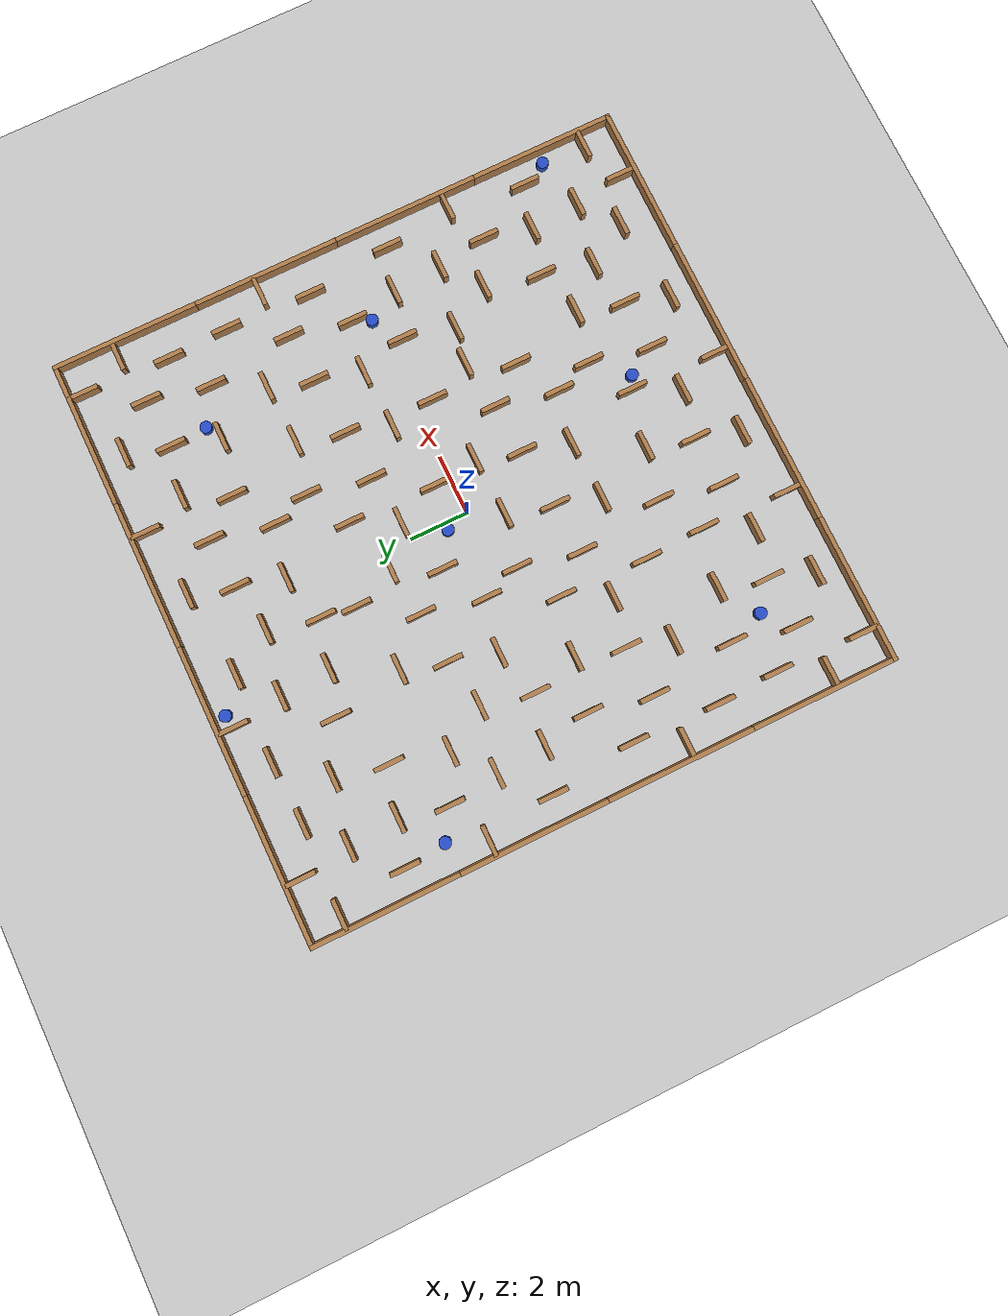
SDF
<sdf version="1.7">
 <world name="default">
  <scene><ambient>0.4 0.4 0.4 1</ambient><background>0.7 0.7 0.7 1</background><shadows>1</shadows></scene>
  <light name="sun" type="directional">
   <pose>0 0 10 0 -0 0</pose>
   <diffuse>0.8 0.8 0.8 1</diffuse>
   <specular>0.2 0.2 0.2 1</specular>
   <attenuation>
    <range>1000</range>
    <constant>0.9</constant>
    <linear>0.01</linear>
    <quadratic>0.001</quadratic>
   </attenuation>
   <direction>-0.5 0.1 -0.9</direction>
   <spot><inner_angle>0</inner_angle><outer_angle>0</outer_angle><falloff>0</falloff></spot>
  </light>
  <model name="ground_plane">
   <pose>2.5 0 0 0 -0 0</pose>
   <static>1</static>
   <link name="link">
    <collision name="collision">
     <geometry><plane><normal>0 0 1</normal><size>100 100</size></plane></geometry>
     <surface>
      <contact><collide_bitmask>65535</collide_bitmask></contact>
      <friction><ode><mu>100</mu><mu2>50</mu2></ode></friction>
     </surface>
    </collision>
    <visual name="visual">
     <cast_shadows>0</cast_shadows>
     <geometry><plane><normal>0 0 1</normal><size>100 100</size></plane></geometry>
     <material>
      <script><uri>file://media/materials/scripts/gazebo.material</uri><name>Gazebo/Grey</name></script>
     </material>
    </visual>
   </link>
  </model>
  <model name="ground_plane">
   <pose>2.5 0 0 0 -0 0</pose>
   <static>1</static>
   <link name="link">
    <collision name="collision">
     <geometry><plane><normal>0 0 1</normal><size>100 100</size></plane></geometry>
     <surface>
      <contact><collide_bitmask>65535</collide_bitmask></contact>
      <friction><ode><mu>100</mu><mu2>50</mu2></ode></friction>
     </surface>
    </collision>
    <visual name="visual">
     <cast_shadows>0</cast_shadows>
     <geometry><plane><normal>0 0 1</normal><size>100 100</size></plane></geometry>
     <material>
      <script><uri>file://media/materials/scripts/gazebo.material</uri><name>Gazebo/Grey</name></script>
     </material>
    </visual>
   </link>
  </model>
  <physics type="ode">
   <real_time_update_rate>1000</real_time_update_rate>
   <max_step_size>0.001</max_step_size>
   <real_time_factor>1</real_time_factor>
   <ode>
    <solver>
     <type>quick</type>
     <iters>150</iters>
     <precon_iters>0</precon_iters>
     <sor>1.4</sor>
     <use_dynamic_moi_rescaling>1</use_dynamic_moi_rescaling>
    </solver>
    <constraints>
     <cfm>1e-05</cfm>
     <erp>0.2</erp>
     <contact_max_correcting_vel>2000</contact_max_correcting_vel>
     <contact_surface_layer>0.01</contact_surface_layer>
    </constraints>
   </ode>
  </physics>
  <gravity>0 0 -9.8</gravity>
  <magnetic_field>6e-06 2.3e-05 -4.2e-05</magnetic_field>
  <atmosphere type="adiabatic"/>
  <audio><device>default</device></audio>
  <spherical_coordinates>
   <surface_model>EARTH_WGS84</surface_model>
   <latitude_deg>0</latitude_deg>
   <longitude_deg>0</longitude_deg>
   <elevation>0</elevation>
   <heading_deg>0</heading_deg>
  </spherical_coordinates>
  <model name="swarmbots_plaza_1">
   <link name="Wall_11">
    <pose>-1.937 -1.467 0 0 -0 0</pose>
    <visual name="Wall_11_Visual">
     <pose>0 0 0.25 0 -0 0</pose>
     <geometry><box><size>1 0.15 0.5</size></box></geometry>
     <material>
      <script><uri>file://media/materials/scripts/gazebo.material</uri><name>Gazebo/Wood</name></script>
      <ambient>1 1 1 1</ambient>
      <shader type="pixel"/>
     </material>
    </visual>
    <collision name="Wall_11_Collision">
     <pose>0 0 0.25 0 -0 0</pose>
     <geometry><box><size>1 0.15 0.5</size></box></geometry>
     <surface>
      <friction>
       <ode><mu>1</mu><mu2>1</mu2><fdir1>0 0 0</fdir1><slip1>0</slip1><slip2>0</slip2></ode>
       <torsional>
        <coefficient>1</coefficient>
        <patch_radius>0</patch_radius>
        <surface_radius>0</surface_radius>
        <use_patch_radius>1</use_patch_radius>
        <ode><slip>0</slip></ode>
       </torsional>
      </friction>
      <bounce><restitution_coefficient>0</restitution_coefficient><threshold>1e+06</threshold></bounce>
      <contact>
       <collide_without_contact>0</collide_without_contact>
       <collide_without_contact_bitmask>1</collide_without_contact_bitmask>
       <collide_bitmask>1</collide_bitmask>
       <ode>
        <soft_cfm>0</soft_cfm>
        <soft_erp>0.2</soft_erp>
        <kp>1e+13</kp>
        <kd>1</kd>
        <max_vel>0.01</max_vel>
        <min_depth>0</min_depth>
       </ode>
       <bullet>
        <split_impulse>1</split_impulse>
        <split_impulse_penetration_threshold>-0.01</split_impulse_penetration_threshold>
        <soft_cfm>0</soft_cfm>
        <soft_erp>0.2</soft_erp>
        <kp>1e+13</kp>
        <kd>1</kd>
       </bullet>
      </contact>
     </surface>
    </collision>
   </link>
   <link name="Wall_13">
    <pose>-0.22 -1.866 0 0 0 -1.5708</pose>
    <visual name="Wall_13_Visual">
     <pose>0 0 0.25 0 -0 0</pose>
     <geometry><box><size>1 0.15 0.5</size></box></geometry>
     <material>
      <script><uri>file://media/materials/scripts/gazebo.material</uri><name>Gazebo/Wood</name></script>
      <ambient>1 1 1 1</ambient>
      <shader type="pixel"/>
     </material>
    </visual>
    <collision name="Wall_13_Collision">
     <pose>0 0 0.25 0 -0 0</pose>
     <geometry><box><size>1 0.15 0.5</size></box></geometry>
     <surface>
      <friction>
       <ode><mu>1</mu><mu2>1</mu2><fdir1>0 0 0</fdir1><slip1>0</slip1><slip2>0</slip2></ode>
       <torsional>
        <coefficient>1</coefficient>
        <patch_radius>0</patch_radius>
        <surface_radius>0</surface_radius>
        <use_patch_radius>1</use_patch_radius>
        <ode><slip>0</slip></ode>
       </torsional>
      </friction>
      <bounce><restitution_coefficient>0</restitution_coefficient><threshold>1e+06</threshold></bounce>
      <contact>
       <collide_without_contact>0</collide_without_contact>
       <collide_without_contact_bitmask>1</collide_without_contact_bitmask>
       <collide_bitmask>1</collide_bitmask>
       <ode>
        <soft_cfm>0</soft_cfm>
        <soft_erp>0.2</soft_erp>
        <kp>1e+13</kp>
        <kd>1</kd>
        <max_vel>0.01</max_vel>
        <min_depth>0</min_depth>
       </ode>
       <bullet>
        <split_impulse>1</split_impulse>
        <split_impulse_penetration_threshold>-0.01</split_impulse_penetration_threshold>
        <soft_cfm>0</soft_cfm>
        <soft_erp>0.2</soft_erp>
        <kp>1e+13</kp>
        <kd>1</kd>
       </bullet>
      </contact>
     </surface>
    </collision>
   </link>
   <link name="Wall_15">
    <pose>1.195 -1.002 0 0 -0 1.5708</pose>
    <visual name="Wall_15_Visual">
     <pose>0 0 0.25 0 -0 0</pose>
     <geometry><box><size>1 0.15 0.5</size></box></geometry>
     <material>
      <script><uri>file://media/materials/scripts/gazebo.material</uri><name>Gazebo/Wood</name></script>
      <ambient>1 1 1 1</ambient>
      <shader type="pixel"/>
     </material>
    </visual>
    <collision name="Wall_15_Collision">
     <pose>0 0 0.25 0 -0 0</pose>
     <geometry><box><size>1 0.15 0.5</size></box></geometry>
     <surface>
      <friction>
       <ode><mu>1</mu><mu2>1</mu2><fdir1>0 0 0</fdir1><slip1>0</slip1><slip2>0</slip2></ode>
       <torsional>
        <coefficient>1</coefficient>
        <patch_radius>0</patch_radius>
        <surface_radius>0</surface_radius>
        <use_patch_radius>1</use_patch_radius>
        <ode><slip>0</slip></ode>
       </torsional>
      </friction>
      <bounce><restitution_coefficient>0</restitution_coefficient><threshold>1e+06</threshold></bounce>
      <contact>
       <collide_without_contact>0</collide_without_contact>
       <collide_without_contact_bitmask>1</collide_without_contact_bitmask>
       <collide_bitmask>1</collide_bitmask>
       <ode>
        <soft_cfm>0</soft_cfm>
        <soft_erp>0.2</soft_erp>
        <kp>1e+13</kp>
        <kd>1</kd>
        <max_vel>0.01</max_vel>
        <min_depth>0</min_depth>
       </ode>
       <bullet>
        <split_impulse>1</split_impulse>
        <split_impulse_penetration_threshold>-0.01</split_impulse_penetration_threshold>
        <soft_cfm>0</soft_cfm>
        <soft_erp>0.2</soft_erp>
        <kp>1e+13</kp>
        <kd>1</kd>
       </bullet>
      </contact>
     </surface>
    </collision>
   </link>
   <link name="Wall_17">
    <pose>1.288 1.93 0 0 0 -1.5708</pose>
    <visual name="Wall_17_Visual">
     <pose>0 0 0.25 0 -0 0</pose>
     <geometry><box><size>1 0.15 0.5</size></box></geometry>
     <material>
      <script><uri>file://media/materials/scripts/gazebo.material</uri><name>Gazebo/Wood</name></script>
      <ambient>1 1 1 1</ambient>
      <shader type="pixel"/>
     </material>
    </visual>
    <collision name="Wall_17_Collision">
     <pose>0 0 0.25 0 -0 0</pose>
     <geometry><box><size>1 0.15 0.5</size></box></geometry>
     <surface>
      <friction>
       <ode><mu>1</mu><mu2>1</mu2><fdir1>0 0 0</fdir1><slip1>0</slip1><slip2>0</slip2></ode>
       <torsional>
        <coefficient>1</coefficient>
        <patch_radius>0</patch_radius>
        <surface_radius>0</surface_radius>
        <use_patch_radius>1</use_patch_radius>
        <ode><slip>0</slip></ode>
       </torsional>
      </friction>
      <bounce><restitution_coefficient>0</restitution_coefficient><threshold>1e+06</threshold></bounce>
      <contact>
       <collide_without_contact>0</collide_without_contact>
       <collide_without_contact_bitmask>1</collide_without_contact_bitmask>
       <collide_bitmask>1</collide_bitmask>
       <ode>
        <soft_cfm>0</soft_cfm>
        <soft_erp>0.2</soft_erp>
        <kp>1e+13</kp>
        <kd>1</kd>
        <max_vel>0.01</max_vel>
        <min_depth>0</min_depth>
       </ode>
       <bullet>
        <split_impulse>1</split_impulse>
        <split_impulse_penetration_threshold>-0.01</split_impulse_penetration_threshold>
        <soft_cfm>0</soft_cfm>
        <soft_erp>0.2</soft_erp>
        <kp>1e+13</kp>
        <kd>1</kd>
       </bullet>
      </contact>
     </surface>
    </collision>
   </link>
   <link name="Wall_19">
    <pose>1.91128 0.4632 0 0 -0 0</pose>
    <visual name="Wall_19_Visual">
     <pose>0 0 0.25 0 -0 0</pose>
     <geometry><box><size>1 0.15 0.5</size></box></geometry>
     <material>
      <script><uri>file://media/materials/scripts/gazebo.material</uri><name>Gazebo/Wood</name></script>
      <ambient>1 1 1 1</ambient>
      <shader type="pixel"/>
     </material>
    </visual>
    <collision name="Wall_19_Collision">
     <pose>0 0 0.25 0 -0 0</pose>
     <geometry><box><size>1 0.15 0.5</size></box></geometry>
     <surface>
      <friction>
       <ode><mu>1</mu><mu2>1</mu2><fdir1>0 0 0</fdir1><slip1>0</slip1><slip2>0</slip2></ode>
       <torsional>
        <coefficient>1</coefficient>
        <patch_radius>0</patch_radius>
        <surface_radius>0</surface_radius>
        <use_patch_radius>1</use_patch_radius>
        <ode><slip>0</slip></ode>
       </torsional>
      </friction>
      <bounce><restitution_coefficient>0</restitution_coefficient><threshold>1e+06</threshold></bounce>
      <contact>
       <collide_without_contact>0</collide_without_contact>
       <collide_without_contact_bitmask>1</collide_without_contact_bitmask>
       <collide_bitmask>1</collide_bitmask>
       <ode>
        <soft_cfm>0</soft_cfm>
        <soft_erp>0.2</soft_erp>
        <kp>1e+13</kp>
        <kd>1</kd>
        <max_vel>0.01</max_vel>
        <min_depth>0</min_depth>
       </ode>
       <bullet>
        <split_impulse>1</split_impulse>
        <split_impulse_penetration_threshold>-0.01</split_impulse_penetration_threshold>
        <soft_cfm>0</soft_cfm>
        <soft_erp>0.2</soft_erp>
        <kp>1e+13</kp>
        <kd>1</kd>
       </bullet>
      </contact>
     </surface>
    </collision>
   </link>
   <link name="Wall_2">
    <pose>0 2.425 0 0 -0 0</pose>
    <visual name="Wall_2_Visual">
     <pose>0 0 0.25 0 -0 0</pose>
     <geometry><box><size>5 0.15 0.5</size></box></geometry>
     <material>
      <script><uri>file://media/materials/scripts/gazebo.material</uri><name>Gazebo/Wood</name></script>
      <ambient>1 1 1 1</ambient>
      <shader type="pixel"/>
     </material>
    </visual>
    <collision name="Wall_2_Collision">
     <pose>0 0 0.25 0 -0 0</pose>
     <geometry><box><size>5 0.15 0.5</size></box></geometry>
     <surface>
      <friction>
       <ode><mu>1</mu><mu2>1</mu2><fdir1>0 0 0</fdir1><slip1>0</slip1><slip2>0</slip2></ode>
       <torsional>
        <coefficient>1</coefficient>
        <patch_radius>0</patch_radius>
        <surface_radius>0</surface_radius>
        <use_patch_radius>1</use_patch_radius>
        <ode><slip>0</slip></ode>
       </torsional>
      </friction>
      <bounce><restitution_coefficient>0</restitution_coefficient><threshold>1e+06</threshold></bounce>
      <contact>
       <collide_without_contact>0</collide_without_contact>
       <collide_without_contact_bitmask>1</collide_without_contact_bitmask>
       <collide_bitmask>1</collide_bitmask>
       <ode>
        <soft_cfm>0</soft_cfm>
        <soft_erp>0.2</soft_erp>
        <kp>1e+13</kp>
        <kd>1</kd>
        <max_vel>0.01</max_vel>
        <min_depth>0</min_depth>
       </ode>
       <bullet>
        <split_impulse>1</split_impulse>
        <split_impulse_penetration_threshold>-0.01</split_impulse_penetration_threshold>
        <soft_cfm>0</soft_cfm>
        <soft_erp>0.2</soft_erp>
        <kp>1e+13</kp>
        <kd>1</kd>
       </bullet>
      </contact>
     </surface>
    </collision>
   </link>
   <link name="Wall_21">
    <pose>0.204 0.215 0 0 0 -1.5708</pose>
    <visual name="Wall_21_Visual">
     <pose>0 0 0.25 0 -0 0</pose>
     <geometry><box><size>1 0.15 0.5</size></box></geometry>
     <material>
      <script><uri>file://media/materials/scripts/gazebo.material</uri><name>Gazebo/Wood</name></script>
      <ambient>1 1 1 1</ambient>
      <shader type="pixel"/>
     </material>
    </visual>
    <collision name="Wall_21_Collision">
     <pose>0 0 0.25 0 -0 0</pose>
     <geometry><box><size>1 0.15 0.5</size></box></geometry>
     <surface>
      <friction>
       <ode><mu>1</mu><mu2>1</mu2><fdir1>0 0 0</fdir1><slip1>0</slip1><slip2>0</slip2></ode>
       <torsional>
        <coefficient>1</coefficient>
        <patch_radius>0</patch_radius>
        <surface_radius>0</surface_radius>
        <use_patch_radius>1</use_patch_radius>
        <ode><slip>0</slip></ode>
       </torsional>
      </friction>
      <bounce><restitution_coefficient>0</restitution_coefficient><threshold>1e+06</threshold></bounce>
      <contact>
       <collide_without_contact>0</collide_without_contact>
       <collide_without_contact_bitmask>1</collide_without_contact_bitmask>
       <collide_bitmask>1</collide_bitmask>
       <ode>
        <soft_cfm>0</soft_cfm>
        <soft_erp>0.2</soft_erp>
        <kp>1e+13</kp>
        <kd>1</kd>
        <max_vel>0.01</max_vel>
        <min_depth>0</min_depth>
       </ode>
       <bullet>
        <split_impulse>1</split_impulse>
        <split_impulse_penetration_threshold>-0.01</split_impulse_penetration_threshold>
        <soft_cfm>0</soft_cfm>
        <soft_erp>0.2</soft_erp>
        <kp>1e+13</kp>
        <kd>1</kd>
       </bullet>
      </contact>
     </surface>
    </collision>
   </link>
   <link name="Wall_7">
    <pose>-1.064 1.548 0 0 -0 0</pose>
    <visual name="Wall_7_Visual">
     <pose>0 0 0.25 0 -0 0</pose>
     <geometry><box><size>1 0.15 0.5</size></box></geometry>
     <material>
      <script><uri>file://media/materials/scripts/gazebo.material</uri><name>Gazebo/Wood</name></script>
      <ambient>1 1 1 1</ambient>
      <shader type="pixel"/>
     </material>
    </visual>
    <collision name="Wall_7_Collision">
     <pose>0 0 0.25 0 -0 0</pose>
     <geometry><box><size>1 0.15 0.5</size></box></geometry>
     <surface>
      <friction>
       <ode><mu>1</mu><mu2>1</mu2><fdir1>0 0 0</fdir1><slip1>0</slip1><slip2>0</slip2></ode>
       <torsional>
        <coefficient>1</coefficient>
        <patch_radius>0</patch_radius>
        <surface_radius>0</surface_radius>
        <use_patch_radius>1</use_patch_radius>
        <ode><slip>0</slip></ode>
       </torsional>
      </friction>
      <bounce><restitution_coefficient>0</restitution_coefficient><threshold>1e+06</threshold></bounce>
      <contact>
       <collide_without_contact>0</collide_without_contact>
       <collide_without_contact_bitmask>1</collide_without_contact_bitmask>
       <collide_bitmask>1</collide_bitmask>
       <ode>
        <soft_cfm>0</soft_cfm>
        <soft_erp>0.2</soft_erp>
        <kp>1e+13</kp>
        <kd>1</kd>
        <max_vel>0.01</max_vel>
        <min_depth>0</min_depth>
       </ode>
       <bullet>
        <split_impulse>1</split_impulse>
        <split_impulse_penetration_threshold>-0.01</split_impulse_penetration_threshold>
        <soft_cfm>0</soft_cfm>
        <soft_erp>0.2</soft_erp>
        <kp>1e+13</kp>
        <kd>1</kd>
       </bullet>
      </contact>
     </surface>
    </collision>
   </link>
   <link name="Wall_9">
    <pose>-1.502 0.092 0 0 0 -1.5708</pose>
    <visual name="Wall_9_Visual">
     <pose>0 0 0.25 0 -0 0</pose>
     <geometry><box><size>1 0.15 0.5</size></box></geometry>
     <material>
      <script><uri>file://media/materials/scripts/gazebo.material</uri><name>Gazebo/Wood</name></script>
      <ambient>1 1 1 1</ambient>
      <shader type="pixel"/>
     </material>
    </visual>
    <collision name="Wall_9_Collision">
     <pose>0 0 0.25 0 -0 0</pose>
     <geometry><box><size>1 0.15 0.5</size></box></geometry>
     <surface>
      <friction>
       <ode><mu>1</mu><mu2>1</mu2><fdir1>0 0 0</fdir1><slip1>0</slip1><slip2>0</slip2></ode>
       <torsional>
        <coefficient>1</coefficient>
        <patch_radius>0</patch_radius>
        <surface_radius>0</surface_radius>
        <use_patch_radius>1</use_patch_radius>
        <ode><slip>0</slip></ode>
       </torsional>
      </friction>
      <bounce><restitution_coefficient>0</restitution_coefficient><threshold>1e+06</threshold></bounce>
      <contact>
       <collide_without_contact>0</collide_without_contact>
       <collide_without_contact_bitmask>1</collide_without_contact_bitmask>
       <collide_bitmask>1</collide_bitmask>
       <ode>
        <soft_cfm>0</soft_cfm>
        <soft_erp>0.2</soft_erp>
        <kp>1e+13</kp>
        <kd>1</kd>
        <max_vel>0.01</max_vel>
        <min_depth>0</min_depth>
       </ode>
       <bullet>
        <split_impulse>1</split_impulse>
        <split_impulse_penetration_threshold>-0.01</split_impulse_penetration_threshold>
        <soft_cfm>0</soft_cfm>
        <soft_erp>0.2</soft_erp>
        <kp>1e+13</kp>
        <kd>1</kd>
       </bullet>
      </contact>
     </surface>
    </collision>
   </link>
   <static>1</static>
   <pose>2.5 7.5 0 0 -0 0</pose>
  </model>
  <model name="swarmbots_plaza_corner_1">
   <link name="Wall_11">
    <pose>-1.937 -1.467 0 0 -0 0</pose>
    <visual name="Wall_11_Visual">
     <pose>0 0 0.25 0 -0 0</pose>
     <geometry><box><size>1 0.15 0.5</size></box></geometry>
     <material>
      <script><uri>file://media/materials/scripts/gazebo.material</uri><name>Gazebo/Wood</name></script>
      <ambient>1 1 1 1</ambient>
      <shader type="pixel"/>
     </material>
    </visual>
    <collision name="Wall_11_Collision">
     <pose>0 0 0.25 0 -0 0</pose>
     <geometry><box><size>1 0.15 0.5</size></box></geometry>
     <surface>
      <friction>
       <ode><mu>1</mu><mu2>1</mu2><fdir1>0 0 0</fdir1><slip1>0</slip1><slip2>0</slip2></ode>
       <torsional>
        <coefficient>1</coefficient>
        <patch_radius>0</patch_radius>
        <surface_radius>0</surface_radius>
        <use_patch_radius>1</use_patch_radius>
        <ode><slip>0</slip></ode>
       </torsional>
      </friction>
      <bounce><restitution_coefficient>0</restitution_coefficient><threshold>1e+06</threshold></bounce>
      <contact>
       <collide_without_contact>0</collide_without_contact>
       <collide_without_contact_bitmask>1</collide_without_contact_bitmask>
       <collide_bitmask>1</collide_bitmask>
       <ode>
        <soft_cfm>0</soft_cfm>
        <soft_erp>0.2</soft_erp>
        <kp>1e+13</kp>
        <kd>1</kd>
        <max_vel>0.01</max_vel>
        <min_depth>0</min_depth>
       </ode>
       <bullet>
        <split_impulse>1</split_impulse>
        <split_impulse_penetration_threshold>-0.01</split_impulse_penetration_threshold>
        <soft_cfm>0</soft_cfm>
        <soft_erp>0.2</soft_erp>
        <kp>1e+13</kp>
        <kd>1</kd>
       </bullet>
      </contact>
     </surface>
    </collision>
   </link>
   <link name="Wall_13">
    <pose>-0.22 -1.866 0 0 0 -1.5708</pose>
    <visual name="Wall_13_Visual">
     <pose>0 0 0.25 0 -0 0</pose>
     <geometry><box><size>1 0.15 0.5</size></box></geometry>
     <material>
      <script><uri>file://media/materials/scripts/gazebo.material</uri><name>Gazebo/Wood</name></script>
      <ambient>1 1 1 1</ambient>
      <shader type="pixel"/>
     </material>
    </visual>
    <collision name="Wall_13_Collision">
     <pose>0 0 0.25 0 -0 0</pose>
     <geometry><box><size>1 0.15 0.5</size></box></geometry>
     <surface>
      <friction>
       <ode><mu>1</mu><mu2>1</mu2><fdir1>0 0 0</fdir1><slip1>0</slip1><slip2>0</slip2></ode>
       <torsional>
        <coefficient>1</coefficient>
        <patch_radius>0</patch_radius>
        <surface_radius>0</surface_radius>
        <use_patch_radius>1</use_patch_radius>
        <ode><slip>0</slip></ode>
       </torsional>
      </friction>
      <bounce><restitution_coefficient>0</restitution_coefficient><threshold>1e+06</threshold></bounce>
      <contact>
       <collide_without_contact>0</collide_without_contact>
       <collide_without_contact_bitmask>1</collide_without_contact_bitmask>
       <collide_bitmask>1</collide_bitmask>
       <ode>
        <soft_cfm>0</soft_cfm>
        <soft_erp>0.2</soft_erp>
        <kp>1e+13</kp>
        <kd>1</kd>
        <max_vel>0.01</max_vel>
        <min_depth>0</min_depth>
       </ode>
       <bullet>
        <split_impulse>1</split_impulse>
        <split_impulse_penetration_threshold>-0.01</split_impulse_penetration_threshold>
        <soft_cfm>0</soft_cfm>
        <soft_erp>0.2</soft_erp>
        <kp>1e+13</kp>
        <kd>1</kd>
       </bullet>
      </contact>
     </surface>
    </collision>
   </link>
   <link name="Wall_15">
    <pose>1.195 -1.002 0 0 -0 1.5708</pose>
    <visual name="Wall_15_Visual">
     <pose>0 0 0.25 0 -0 0</pose>
     <geometry><box><size>1 0.15 0.5</size></box></geometry>
     <material>
      <script><uri>file://media/materials/scripts/gazebo.material</uri><name>Gazebo/Wood</name></script>
      <ambient>1 1 1 1</ambient>
      <shader type="pixel"/>
     </material>
    </visual>
    <collision name="Wall_15_Collision">
     <pose>0 0 0.25 0 -0 0</pose>
     <geometry><box><size>1 0.15 0.5</size></box></geometry>
     <surface>
      <friction>
       <ode><mu>1</mu><mu2>1</mu2><fdir1>0 0 0</fdir1><slip1>0</slip1><slip2>0</slip2></ode>
       <torsional>
        <coefficient>1</coefficient>
        <patch_radius>0</patch_radius>
        <surface_radius>0</surface_radius>
        <use_patch_radius>1</use_patch_radius>
        <ode><slip>0</slip></ode>
       </torsional>
      </friction>
      <bounce><restitution_coefficient>0</restitution_coefficient><threshold>1e+06</threshold></bounce>
      <contact>
       <collide_without_contact>0</collide_without_contact>
       <collide_without_contact_bitmask>1</collide_without_contact_bitmask>
       <collide_bitmask>1</collide_bitmask>
       <ode>
        <soft_cfm>0</soft_cfm>
        <soft_erp>0.2</soft_erp>
        <kp>1e+13</kp>
        <kd>1</kd>
        <max_vel>0.01</max_vel>
        <min_depth>0</min_depth>
       </ode>
       <bullet>
        <split_impulse>1</split_impulse>
        <split_impulse_penetration_threshold>-0.01</split_impulse_penetration_threshold>
        <soft_cfm>0</soft_cfm>
        <soft_erp>0.2</soft_erp>
        <kp>1e+13</kp>
        <kd>1</kd>
       </bullet>
      </contact>
     </surface>
    </collision>
   </link>
   <link name="Wall_17">
    <pose>1.288 1.93 0 0 0 -1.5708</pose>
    <visual name="Wall_17_Visual">
     <pose>0 0 0.25 0 -0 0</pose>
     <geometry><box><size>1 0.15 0.5</size></box></geometry>
     <material>
      <script><uri>file://media/materials/scripts/gazebo.material</uri><name>Gazebo/Wood</name></script>
      <ambient>1 1 1 1</ambient>
      <shader type="pixel"/>
     </material>
    </visual>
    <collision name="Wall_17_Collision">
     <pose>0 0 0.25 0 -0 0</pose>
     <geometry><box><size>1 0.15 0.5</size></box></geometry>
     <surface>
      <friction>
       <ode><mu>1</mu><mu2>1</mu2><fdir1>0 0 0</fdir1><slip1>0</slip1><slip2>0</slip2></ode>
       <torsional>
        <coefficient>1</coefficient>
        <patch_radius>0</patch_radius>
        <surface_radius>0</surface_radius>
        <use_patch_radius>1</use_patch_radius>
        <ode><slip>0</slip></ode>
       </torsional>
      </friction>
      <bounce><restitution_coefficient>0</restitution_coefficient><threshold>1e+06</threshold></bounce>
      <contact>
       <collide_without_contact>0</collide_without_contact>
       <collide_without_contact_bitmask>1</collide_without_contact_bitmask>
       <collide_bitmask>1</collide_bitmask>
       <ode>
        <soft_cfm>0</soft_cfm>
        <soft_erp>0.2</soft_erp>
        <kp>1e+13</kp>
        <kd>1</kd>
        <max_vel>0.01</max_vel>
        <min_depth>0</min_depth>
       </ode>
       <bullet>
        <split_impulse>1</split_impulse>
        <split_impulse_penetration_threshold>-0.01</split_impulse_penetration_threshold>
        <soft_cfm>0</soft_cfm>
        <soft_erp>0.2</soft_erp>
        <kp>1e+13</kp>
        <kd>1</kd>
       </bullet>
      </contact>
     </surface>
    </collision>
   </link>
   <link name="Wall_19">
    <pose>1.91128 0.4632 0 0 -0 0</pose>
    <visual name="Wall_19_Visual">
     <pose>0 0 0.25 0 -0 0</pose>
     <geometry><box><size>1 0.15 0.5</size></box></geometry>
     <material>
      <script><uri>file://media/materials/scripts/gazebo.material</uri><name>Gazebo/Wood</name></script>
      <ambient>1 1 1 1</ambient>
      <shader type="pixel"/>
     </material>
    </visual>
    <collision name="Wall_19_Collision">
     <pose>0 0 0.25 0 -0 0</pose>
     <geometry><box><size>1 0.15 0.5</size></box></geometry>
     <surface>
      <friction>
       <ode><mu>1</mu><mu2>1</mu2><fdir1>0 0 0</fdir1><slip1>0</slip1><slip2>0</slip2></ode>
       <torsional>
        <coefficient>1</coefficient>
        <patch_radius>0</patch_radius>
        <surface_radius>0</surface_radius>
        <use_patch_radius>1</use_patch_radius>
        <ode><slip>0</slip></ode>
       </torsional>
      </friction>
      <bounce><restitution_coefficient>0</restitution_coefficient><threshold>1e+06</threshold></bounce>
      <contact>
       <collide_without_contact>0</collide_without_contact>
       <collide_without_contact_bitmask>1</collide_without_contact_bitmask>
       <collide_bitmask>1</collide_bitmask>
       <ode>
        <soft_cfm>0</soft_cfm>
        <soft_erp>0.2</soft_erp>
        <kp>1e+13</kp>
        <kd>1</kd>
        <max_vel>0.01</max_vel>
        <min_depth>0</min_depth>
       </ode>
       <bullet>
        <split_impulse>1</split_impulse>
        <split_impulse_penetration_threshold>-0.01</split_impulse_penetration_threshold>
        <soft_cfm>0</soft_cfm>
        <soft_erp>0.2</soft_erp>
        <kp>1e+13</kp>
        <kd>1</kd>
       </bullet>
      </contact>
     </surface>
    </collision>
   </link>
   <link name="Wall_2">
    <pose>0 2.425 0 0 -0 0</pose>
    <visual name="Wall_2_Visual">
     <pose>0 0 0.25 0 -0 0</pose>
     <geometry><box><size>5 0.15 0.5</size></box></geometry>
     <material>
      <script><uri>file://media/materials/scripts/gazebo.material</uri><name>Gazebo/Wood</name></script>
      <ambient>1 1 1 1</ambient>
      <shader type="pixel"/>
     </material>
    </visual>
    <collision name="Wall_2_Collision">
     <pose>0 0 0.25 0 -0 0</pose>
     <geometry><box><size>5 0.15 0.5</size></box></geometry>
     <surface>
      <friction>
       <ode><mu>1</mu><mu2>1</mu2><fdir1>0 0 0</fdir1><slip1>0</slip1><slip2>0</slip2></ode>
       <torsional>
        <coefficient>1</coefficient>
        <patch_radius>0</patch_radius>
        <surface_radius>0</surface_radius>
        <use_patch_radius>1</use_patch_radius>
        <ode><slip>0</slip></ode>
       </torsional>
      </friction>
      <bounce><restitution_coefficient>0</restitution_coefficient><threshold>1e+06</threshold></bounce>
      <contact>
       <collide_without_contact>0</collide_without_contact>
       <collide_without_contact_bitmask>1</collide_without_contact_bitmask>
       <collide_bitmask>1</collide_bitmask>
       <ode>
        <soft_cfm>0</soft_cfm>
        <soft_erp>0.2</soft_erp>
        <kp>1e+13</kp>
        <kd>1</kd>
        <max_vel>0.01</max_vel>
        <min_depth>0</min_depth>
       </ode>
       <bullet>
        <split_impulse>1</split_impulse>
        <split_impulse_penetration_threshold>-0.01</split_impulse_penetration_threshold>
        <soft_cfm>0</soft_cfm>
        <soft_erp>0.2</soft_erp>
        <kp>1e+13</kp>
        <kd>1</kd>
       </bullet>
      </contact>
     </surface>
    </collision>
   </link>
   <link name="Wall_21">
    <pose>0.204 0.215 0 0 0 -1.5708</pose>
    <visual name="Wall_21_Visual">
     <pose>0 0 0.25 0 -0 0</pose>
     <geometry><box><size>1 0.15 0.5</size></box></geometry>
     <material>
      <script><uri>file://media/materials/scripts/gazebo.material</uri><name>Gazebo/Wood</name></script>
      <ambient>1 1 1 1</ambient>
      <shader type="pixel"/>
     </material>
    </visual>
    <collision name="Wall_21_Collision">
     <pose>0 0 0.25 0 -0 0</pose>
     <geometry><box><size>1 0.15 0.5</size></box></geometry>
     <surface>
      <friction>
       <ode><mu>1</mu><mu2>1</mu2><fdir1>0 0 0</fdir1><slip1>0</slip1><slip2>0</slip2></ode>
       <torsional>
        <coefficient>1</coefficient>
        <patch_radius>0</patch_radius>
        <surface_radius>0</surface_radius>
        <use_patch_radius>1</use_patch_radius>
        <ode><slip>0</slip></ode>
       </torsional>
      </friction>
      <bounce><restitution_coefficient>0</restitution_coefficient><threshold>1e+06</threshold></bounce>
      <contact>
       <collide_without_contact>0</collide_without_contact>
       <collide_without_contact_bitmask>1</collide_without_contact_bitmask>
       <collide_bitmask>1</collide_bitmask>
       <ode>
        <soft_cfm>0</soft_cfm>
        <soft_erp>0.2</soft_erp>
        <kp>1e+13</kp>
        <kd>1</kd>
        <max_vel>0.01</max_vel>
        <min_depth>0</min_depth>
       </ode>
       <bullet>
        <split_impulse>1</split_impulse>
        <split_impulse_penetration_threshold>-0.01</split_impulse_penetration_threshold>
        <soft_cfm>0</soft_cfm>
        <soft_erp>0.2</soft_erp>
        <kp>1e+13</kp>
        <kd>1</kd>
       </bullet>
      </contact>
     </surface>
    </collision>
   </link>
   <link name="Wall_3">
    <pose>2.425 0 0 0 0 -1.5708</pose>
    <visual name="Wall_3_Visual">
     <pose>0 0 0.25 0 -0 0</pose>
     <geometry><box><size>5 0.15 0.5</size></box></geometry>
     <material>
      <script><uri>file://media/materials/scripts/gazebo.material</uri><name>Gazebo/Wood</name></script>
      <ambient>1 1 1 1</ambient>
      <shader type="pixel"/>
     </material>
    </visual>
    <collision name="Wall_3_Collision">
     <pose>0 0 0.25 0 -0 0</pose>
     <geometry><box><size>5 0.15 0.5</size></box></geometry>
     <surface>
      <friction>
       <ode><mu>1</mu><mu2>1</mu2><fdir1>0 0 0</fdir1><slip1>0</slip1><slip2>0</slip2></ode>
       <torsional>
        <coefficient>1</coefficient>
        <patch_radius>0</patch_radius>
        <surface_radius>0</surface_radius>
        <use_patch_radius>1</use_patch_radius>
        <ode><slip>0</slip></ode>
       </torsional>
      </friction>
      <bounce><restitution_coefficient>0</restitution_coefficient><threshold>1e+06</threshold></bounce>
      <contact>
       <collide_without_contact>0</collide_without_contact>
       <collide_without_contact_bitmask>1</collide_without_contact_bitmask>
       <collide_bitmask>1</collide_bitmask>
       <ode>
        <soft_cfm>0</soft_cfm>
        <soft_erp>0.2</soft_erp>
        <kp>1e+13</kp>
        <kd>1</kd>
        <max_vel>0.01</max_vel>
        <min_depth>0</min_depth>
       </ode>
       <bullet>
        <split_impulse>1</split_impulse>
        <split_impulse_penetration_threshold>-0.01</split_impulse_penetration_threshold>
        <soft_cfm>0</soft_cfm>
        <soft_erp>0.2</soft_erp>
        <kp>1e+13</kp>
        <kd>1</kd>
       </bullet>
      </contact>
     </surface>
    </collision>
   </link>
   <link name="Wall_7">
    <pose>-1.064 1.548 0 0 -0 0</pose>
    <visual name="Wall_7_Visual">
     <pose>0 0 0.25 0 -0 0</pose>
     <geometry><box><size>1 0.15 0.5</size></box></geometry>
     <material>
      <script><uri>file://media/materials/scripts/gazebo.material</uri><name>Gazebo/Wood</name></script>
      <ambient>1 1 1 1</ambient>
      <shader type="pixel"/>
     </material>
    </visual>
    <collision name="Wall_7_Collision">
     <pose>0 0 0.25 0 -0 0</pose>
     <geometry><box><size>1 0.15 0.5</size></box></geometry>
     <surface>
      <friction>
       <ode><mu>1</mu><mu2>1</mu2><fdir1>0 0 0</fdir1><slip1>0</slip1><slip2>0</slip2></ode>
       <torsional>
        <coefficient>1</coefficient>
        <patch_radius>0</patch_radius>
        <surface_radius>0</surface_radius>
        <use_patch_radius>1</use_patch_radius>
        <ode><slip>0</slip></ode>
       </torsional>
      </friction>
      <bounce><restitution_coefficient>0</restitution_coefficient><threshold>1e+06</threshold></bounce>
      <contact>
       <collide_without_contact>0</collide_without_contact>
       <collide_without_contact_bitmask>1</collide_without_contact_bitmask>
       <collide_bitmask>1</collide_bitmask>
       <ode>
        <soft_cfm>0</soft_cfm>
        <soft_erp>0.2</soft_erp>
        <kp>1e+13</kp>
        <kd>1</kd>
        <max_vel>0.01</max_vel>
        <min_depth>0</min_depth>
       </ode>
       <bullet>
        <split_impulse>1</split_impulse>
        <split_impulse_penetration_threshold>-0.01</split_impulse_penetration_threshold>
        <soft_cfm>0</soft_cfm>
        <soft_erp>0.2</soft_erp>
        <kp>1e+13</kp>
        <kd>1</kd>
       </bullet>
      </contact>
     </surface>
    </collision>
   </link>
   <link name="Wall_9">
    <pose>-1.502 0.092 0 0 0 -1.5708</pose>
    <visual name="Wall_9_Visual">
     <pose>0 0 0.25 0 -0 0</pose>
     <geometry><box><size>1 0.15 0.5</size></box></geometry>
     <material>
      <script><uri>file://media/materials/scripts/gazebo.material</uri><name>Gazebo/Wood</name></script>
      <ambient>1 1 1 1</ambient>
      <shader type="pixel"/>
     </material>
    </visual>
    <collision name="Wall_9_Collision">
     <pose>0 0 0.25 0 -0 0</pose>
     <geometry><box><size>1 0.15 0.5</size></box></geometry>
     <surface>
      <friction>
       <ode><mu>1</mu><mu2>1</mu2><fdir1>0 0 0</fdir1><slip1>0</slip1><slip2>0</slip2></ode>
       <torsional>
        <coefficient>1</coefficient>
        <patch_radius>0</patch_radius>
        <surface_radius>0</surface_radius>
        <use_patch_radius>1</use_patch_radius>
        <ode><slip>0</slip></ode>
       </torsional>
      </friction>
      <bounce><restitution_coefficient>0</restitution_coefficient><threshold>1e+06</threshold></bounce>
      <contact>
       <collide_without_contact>0</collide_without_contact>
       <collide_without_contact_bitmask>1</collide_without_contact_bitmask>
       <collide_bitmask>1</collide_bitmask>
       <ode>
        <soft_cfm>0</soft_cfm>
        <soft_erp>0.2</soft_erp>
        <kp>1e+13</kp>
        <kd>1</kd>
        <max_vel>0.01</max_vel>
        <min_depth>0</min_depth>
       </ode>
       <bullet>
        <split_impulse>1</split_impulse>
        <split_impulse_penetration_threshold>-0.01</split_impulse_penetration_threshold>
        <soft_cfm>0</soft_cfm>
        <soft_erp>0.2</soft_erp>
        <kp>1e+13</kp>
        <kd>1</kd>
       </bullet>
      </contact>
     </surface>
    </collision>
   </link>
   <static>1</static>
   <pose>7.5 7.5 0 0 -0 0</pose>
  </model>
  <model name="swarmbot_plaza_2">
   <link name="Wall_11">
    <pose>-1.937 -1.467 0 0 -0 0</pose>
    <visual name="Wall_11_Visual">
     <pose>0 0 0.25 0 -0 0</pose>
     <geometry><box><size>1 0.15 0.5</size></box></geometry>
     <material>
      <script><uri>file://media/materials/scripts/gazebo.material</uri><name>Gazebo/Wood</name></script>
      <ambient>1 1 1 1</ambient>
      <shader type="pixel"/>
     </material>
    </visual>
    <collision name="Wall_11_Collision">
     <pose>0 0 0.25 0 -0 0</pose>
     <geometry><box><size>1 0.15 0.5</size></box></geometry>
     <surface>
      <friction>
       <ode><mu>1</mu><mu2>1</mu2><fdir1>0 0 0</fdir1><slip1>0</slip1><slip2>0</slip2></ode>
       <torsional>
        <coefficient>1</coefficient>
        <patch_radius>0</patch_radius>
        <surface_radius>0</surface_radius>
        <use_patch_radius>1</use_patch_radius>
        <ode><slip>0</slip></ode>
       </torsional>
      </friction>
      <bounce><restitution_coefficient>0</restitution_coefficient><threshold>1e+06</threshold></bounce>
      <contact>
       <collide_without_contact>0</collide_without_contact>
       <collide_without_contact_bitmask>1</collide_without_contact_bitmask>
       <collide_bitmask>1</collide_bitmask>
       <ode>
        <soft_cfm>0</soft_cfm>
        <soft_erp>0.2</soft_erp>
        <kp>1e+13</kp>
        <kd>1</kd>
        <max_vel>0.01</max_vel>
        <min_depth>0</min_depth>
       </ode>
       <bullet>
        <split_impulse>1</split_impulse>
        <split_impulse_penetration_threshold>-0.01</split_impulse_penetration_threshold>
        <soft_cfm>0</soft_cfm>
        <soft_erp>0.2</soft_erp>
        <kp>1e+13</kp>
        <kd>1</kd>
       </bullet>
      </contact>
     </surface>
    </collision>
   </link>
   <link name="Wall_13">
    <pose>-0.22 -1.866 0 0 0 -1.5708</pose>
    <visual name="Wall_13_Visual">
     <pose>0 0 0.25 0 -0 0</pose>
     <geometry><box><size>1 0.15 0.5</size></box></geometry>
     <material>
      <script><uri>file://media/materials/scripts/gazebo.material</uri><name>Gazebo/Wood</name></script>
      <ambient>1 1 1 1</ambient>
      <shader type="pixel"/>
     </material>
    </visual>
    <collision name="Wall_13_Collision">
     <pose>0 0 0.25 0 -0 0</pose>
     <geometry><box><size>1 0.15 0.5</size></box></geometry>
     <surface>
      <friction>
       <ode><mu>1</mu><mu2>1</mu2><fdir1>0 0 0</fdir1><slip1>0</slip1><slip2>0</slip2></ode>
       <torsional>
        <coefficient>1</coefficient>
        <patch_radius>0</patch_radius>
        <surface_radius>0</surface_radius>
        <use_patch_radius>1</use_patch_radius>
        <ode><slip>0</slip></ode>
       </torsional>
      </friction>
      <bounce><restitution_coefficient>0</restitution_coefficient><threshold>1e+06</threshold></bounce>
      <contact>
       <collide_without_contact>0</collide_without_contact>
       <collide_without_contact_bitmask>1</collide_without_contact_bitmask>
       <collide_bitmask>1</collide_bitmask>
       <ode>
        <soft_cfm>0</soft_cfm>
        <soft_erp>0.2</soft_erp>
        <kp>1e+13</kp>
        <kd>1</kd>
        <max_vel>0.01</max_vel>
        <min_depth>0</min_depth>
       </ode>
       <bullet>
        <split_impulse>1</split_impulse>
        <split_impulse_penetration_threshold>-0.01</split_impulse_penetration_threshold>
        <soft_cfm>0</soft_cfm>
        <soft_erp>0.2</soft_erp>
        <kp>1e+13</kp>
        <kd>1</kd>
       </bullet>
      </contact>
     </surface>
    </collision>
   </link>
   <link name="Wall_15">
    <pose>1.195 -1.002 0 0 -0 1.5708</pose>
    <visual name="Wall_15_Visual">
     <pose>0 0 0.25 0 -0 0</pose>
     <geometry><box><size>1 0.15 0.5</size></box></geometry>
     <material>
      <script><uri>file://media/materials/scripts/gazebo.material</uri><name>Gazebo/Wood</name></script>
      <ambient>1 1 1 1</ambient>
      <shader type="pixel"/>
     </material>
    </visual>
    <collision name="Wall_15_Collision">
     <pose>0 0 0.25 0 -0 0</pose>
     <geometry><box><size>1 0.15 0.5</size></box></geometry>
     <surface>
      <friction>
       <ode><mu>1</mu><mu2>1</mu2><fdir1>0 0 0</fdir1><slip1>0</slip1><slip2>0</slip2></ode>
       <torsional>
        <coefficient>1</coefficient>
        <patch_radius>0</patch_radius>
        <surface_radius>0</surface_radius>
        <use_patch_radius>1</use_patch_radius>
        <ode><slip>0</slip></ode>
       </torsional>
      </friction>
      <bounce><restitution_coefficient>0</restitution_coefficient><threshold>1e+06</threshold></bounce>
      <contact>
       <collide_without_contact>0</collide_without_contact>
       <collide_without_contact_bitmask>1</collide_without_contact_bitmask>
       <collide_bitmask>1</collide_bitmask>
       <ode>
        <soft_cfm>0</soft_cfm>
        <soft_erp>0.2</soft_erp>
        <kp>1e+13</kp>
        <kd>1</kd>
        <max_vel>0.01</max_vel>
        <min_depth>0</min_depth>
       </ode>
       <bullet>
        <split_impulse>1</split_impulse>
        <split_impulse_penetration_threshold>-0.01</split_impulse_penetration_threshold>
        <soft_cfm>0</soft_cfm>
        <soft_erp>0.2</soft_erp>
        <kp>1e+13</kp>
        <kd>1</kd>
       </bullet>
      </contact>
     </surface>
    </collision>
   </link>
   <link name="Wall_17">
    <pose>1.288 1.93 0 0 0 -1.5708</pose>
    <visual name="Wall_17_Visual">
     <pose>0 0 0.25 0 -0 0</pose>
     <geometry><box><size>1 0.15 0.5</size></box></geometry>
     <material>
      <script><uri>file://media/materials/scripts/gazebo.material</uri><name>Gazebo/Wood</name></script>
      <ambient>1 1 1 1</ambient>
      <shader type="pixel"/>
     </material>
    </visual>
    <collision name="Wall_17_Collision">
     <pose>0 0 0.25 0 -0 0</pose>
     <geometry><box><size>1 0.15 0.5</size></box></geometry>
     <surface>
      <friction>
       <ode><mu>1</mu><mu2>1</mu2><fdir1>0 0 0</fdir1><slip1>0</slip1><slip2>0</slip2></ode>
       <torsional>
        <coefficient>1</coefficient>
        <patch_radius>0</patch_radius>
        <surface_radius>0</surface_radius>
        <use_patch_radius>1</use_patch_radius>
        <ode><slip>0</slip></ode>
       </torsional>
      </friction>
      <bounce><restitution_coefficient>0</restitution_coefficient><threshold>1e+06</threshold></bounce>
      <contact>
       <collide_without_contact>0</collide_without_contact>
       <collide_without_contact_bitmask>1</collide_without_contact_bitmask>
       <collide_bitmask>1</collide_bitmask>
       <ode>
        <soft_cfm>0</soft_cfm>
        <soft_erp>0.2</soft_erp>
        <kp>1e+13</kp>
        <kd>1</kd>
        <max_vel>0.01</max_vel>
        <min_depth>0</min_depth>
       </ode>
       <bullet>
        <split_impulse>1</split_impulse>
        <split_impulse_penetration_threshold>-0.01</split_impulse_penetration_threshold>
        <soft_cfm>0</soft_cfm>
        <soft_erp>0.2</soft_erp>
        <kp>1e+13</kp>
        <kd>1</kd>
       </bullet>
      </contact>
     </surface>
    </collision>
   </link>
   <link name="Wall_19">
    <pose>1.91128 0.4632 0 0 -0 0</pose>
    <visual name="Wall_19_Visual">
     <pose>0 0 0.25 0 -0 0</pose>
     <geometry><box><size>1 0.15 0.5</size></box></geometry>
     <material>
      <script><uri>file://media/materials/scripts/gazebo.material</uri><name>Gazebo/Wood</name></script>
      <ambient>1 1 1 1</ambient>
      <shader type="pixel"/>
     </material>
    </visual>
    <collision name="Wall_19_Collision">
     <pose>0 0 0.25 0 -0 0</pose>
     <geometry><box><size>1 0.15 0.5</size></box></geometry>
     <surface>
      <friction>
       <ode><mu>1</mu><mu2>1</mu2><fdir1>0 0 0</fdir1><slip1>0</slip1><slip2>0</slip2></ode>
       <torsional>
        <coefficient>1</coefficient>
        <patch_radius>0</patch_radius>
        <surface_radius>0</surface_radius>
        <use_patch_radius>1</use_patch_radius>
        <ode><slip>0</slip></ode>
       </torsional>
      </friction>
      <bounce><restitution_coefficient>0</restitution_coefficient><threshold>1e+06</threshold></bounce>
      <contact>
       <collide_without_contact>0</collide_without_contact>
       <collide_without_contact_bitmask>1</collide_without_contact_bitmask>
       <collide_bitmask>1</collide_bitmask>
       <ode>
        <soft_cfm>0</soft_cfm>
        <soft_erp>0.2</soft_erp>
        <kp>1e+13</kp>
        <kd>1</kd>
        <max_vel>0.01</max_vel>
        <min_depth>0</min_depth>
       </ode>
       <bullet>
        <split_impulse>1</split_impulse>
        <split_impulse_penetration_threshold>-0.01</split_impulse_penetration_threshold>
        <soft_cfm>0</soft_cfm>
        <soft_erp>0.2</soft_erp>
        <kp>1e+13</kp>
        <kd>1</kd>
       </bullet>
      </contact>
     </surface>
    </collision>
   </link>
   <link name="Wall_21">
    <pose>0.204 0.215 0 0 0 -1.5708</pose>
    <visual name="Wall_21_Visual">
     <pose>0 0 0.25 0 -0 0</pose>
     <geometry><box><size>1 0.15 0.5</size></box></geometry>
     <material>
      <script><uri>file://media/materials/scripts/gazebo.material</uri><name>Gazebo/Wood</name></script>
      <ambient>1 1 1 1</ambient>
      <shader type="pixel"/>
     </material>
    </visual>
    <collision name="Wall_21_Collision">
     <pose>0 0 0.25 0 -0 0</pose>
     <geometry><box><size>1 0.15 0.5</size></box></geometry>
     <surface>
      <friction>
       <ode><mu>1</mu><mu2>1</mu2><fdir1>0 0 0</fdir1><slip1>0</slip1><slip2>0</slip2></ode>
       <torsional>
        <coefficient>1</coefficient>
        <patch_radius>0</patch_radius>
        <surface_radius>0</surface_radius>
        <use_patch_radius>1</use_patch_radius>
        <ode><slip>0</slip></ode>
       </torsional>
      </friction>
      <bounce><restitution_coefficient>0</restitution_coefficient><threshold>1e+06</threshold></bounce>
      <contact>
       <collide_without_contact>0</collide_without_contact>
       <collide_without_contact_bitmask>1</collide_without_contact_bitmask>
       <collide_bitmask>1</collide_bitmask>
       <ode>
        <soft_cfm>0</soft_cfm>
        <soft_erp>0.2</soft_erp>
        <kp>1e+13</kp>
        <kd>1</kd>
        <max_vel>0.01</max_vel>
        <min_depth>0</min_depth>
       </ode>
       <bullet>
        <split_impulse>1</split_impulse>
        <split_impulse_penetration_threshold>-0.01</split_impulse_penetration_threshold>
        <soft_cfm>0</soft_cfm>
        <soft_erp>0.2</soft_erp>
        <kp>1e+13</kp>
        <kd>1</kd>
       </bullet>
      </contact>
     </surface>
    </collision>
   </link>
   <link name="Wall_3">
    <pose>2.425 0 0 0 0 -1.5708</pose>
    <visual name="Wall_3_Visual">
     <pose>0 0 0.25 0 -0 0</pose>
     <geometry><box><size>5 0.15 0.5</size></box></geometry>
     <material>
      <script><uri>file://media/materials/scripts/gazebo.material</uri><name>Gazebo/Wood</name></script>
      <ambient>1 1 1 1</ambient>
      <shader type="pixel"/>
     </material>
    </visual>
    <collision name="Wall_3_Collision">
     <pose>0 0 0.25 0 -0 0</pose>
     <geometry><box><size>5 0.15 0.5</size></box></geometry>
     <surface>
      <friction>
       <ode><mu>1</mu><mu2>1</mu2><fdir1>0 0 0</fdir1><slip1>0</slip1><slip2>0</slip2></ode>
       <torsional>
        <coefficient>1</coefficient>
        <patch_radius>0</patch_radius>
        <surface_radius>0</surface_radius>
        <use_patch_radius>1</use_patch_radius>
        <ode><slip>0</slip></ode>
       </torsional>
      </friction>
      <bounce><restitution_coefficient>0</restitution_coefficient><threshold>1e+06</threshold></bounce>
      <contact>
       <collide_without_contact>0</collide_without_contact>
       <collide_without_contact_bitmask>1</collide_without_contact_bitmask>
       <collide_bitmask>1</collide_bitmask>
       <ode>
        <soft_cfm>0</soft_cfm>
        <soft_erp>0.2</soft_erp>
        <kp>1e+13</kp>
        <kd>1</kd>
        <max_vel>0.01</max_vel>
        <min_depth>0</min_depth>
       </ode>
       <bullet>
        <split_impulse>1</split_impulse>
        <split_impulse_penetration_threshold>-0.01</split_impulse_penetration_threshold>
        <soft_cfm>0</soft_cfm>
        <soft_erp>0.2</soft_erp>
        <kp>1e+13</kp>
        <kd>1</kd>
       </bullet>
      </contact>
     </surface>
    </collision>
   </link>
   <link name="Wall_7">
    <pose>-1.064 1.548 0 0 -0 0</pose>
    <visual name="Wall_7_Visual">
     <pose>0 0 0.25 0 -0 0</pose>
     <geometry><box><size>1 0.15 0.5</size></box></geometry>
     <material>
      <script><uri>file://media/materials/scripts/gazebo.material</uri><name>Gazebo/Wood</name></script>
      <ambient>1 1 1 1</ambient>
      <shader type="pixel"/>
     </material>
    </visual>
    <collision name="Wall_7_Collision">
     <pose>0 0 0.25 0 -0 0</pose>
     <geometry><box><size>1 0.15 0.5</size></box></geometry>
     <surface>
      <friction>
       <ode><mu>1</mu><mu2>1</mu2><fdir1>0 0 0</fdir1><slip1>0</slip1><slip2>0</slip2></ode>
       <torsional>
        <coefficient>1</coefficient>
        <patch_radius>0</patch_radius>
        <surface_radius>0</surface_radius>
        <use_patch_radius>1</use_patch_radius>
        <ode><slip>0</slip></ode>
       </torsional>
      </friction>
      <bounce><restitution_coefficient>0</restitution_coefficient><threshold>1e+06</threshold></bounce>
      <contact>
       <collide_without_contact>0</collide_without_contact>
       <collide_without_contact_bitmask>1</collide_without_contact_bitmask>
       <collide_bitmask>1</collide_bitmask>
       <ode>
        <soft_cfm>0</soft_cfm>
        <soft_erp>0.2</soft_erp>
        <kp>1e+13</kp>
        <kd>1</kd>
        <max_vel>0.01</max_vel>
        <min_depth>0</min_depth>
       </ode>
       <bullet>
        <split_impulse>1</split_impulse>
        <split_impulse_penetration_threshold>-0.01</split_impulse_penetration_threshold>
        <soft_cfm>0</soft_cfm>
        <soft_erp>0.2</soft_erp>
        <kp>1e+13</kp>
        <kd>1</kd>
       </bullet>
      </contact>
     </surface>
    </collision>
   </link>
   <link name="Wall_9">
    <pose>-1.502 0.092 0 0 0 -1.5708</pose>
    <visual name="Wall_9_Visual">
     <pose>0 0 0.25 0 -0 0</pose>
     <geometry><box><size>1 0.15 0.5</size></box></geometry>
     <material>
      <script><uri>file://media/materials/scripts/gazebo.material</uri><name>Gazebo/Wood</name></script>
      <ambient>1 1 1 1</ambient>
      <shader type="pixel"/>
     </material>
    </visual>
    <collision name="Wall_9_Collision">
     <pose>0 0 0.25 0 -0 0</pose>
     <geometry><box><size>1 0.15 0.5</size></box></geometry>
     <surface>
      <friction>
       <ode><mu>1</mu><mu2>1</mu2><fdir1>0 0 0</fdir1><slip1>0</slip1><slip2>0</slip2></ode>
       <torsional>
        <coefficient>1</coefficient>
        <patch_radius>0</patch_radius>
        <surface_radius>0</surface_radius>
        <use_patch_radius>1</use_patch_radius>
        <ode><slip>0</slip></ode>
       </torsional>
      </friction>
      <bounce><restitution_coefficient>0</restitution_coefficient><threshold>1e+06</threshold></bounce>
      <contact>
       <collide_without_contact>0</collide_without_contact>
       <collide_without_contact_bitmask>1</collide_without_contact_bitmask>
       <collide_bitmask>1</collide_bitmask>
       <ode>
        <soft_cfm>0</soft_cfm>
        <soft_erp>0.2</soft_erp>
        <kp>1e+13</kp>
        <kd>1</kd>
        <max_vel>0.01</max_vel>
        <min_depth>0</min_depth>
       </ode>
       <bullet>
        <split_impulse>1</split_impulse>
        <split_impulse_penetration_threshold>-0.01</split_impulse_penetration_threshold>
        <soft_cfm>0</soft_cfm>
        <soft_erp>0.2</soft_erp>
        <kp>1e+13</kp>
        <kd>1</kd>
       </bullet>
      </contact>
     </surface>
    </collision>
   </link>
   <static>1</static>
   <pose>7.5 2.5 0 0 -0 0</pose>
  </model>
  <model name="swarmbot_plaza_0">
   <link name="Wall_11">
    <pose>-1.937 -1.467 0 0 -0 0</pose>
    <visual name="Wall_11_Visual">
     <pose>0 0 0.25 0 -0 0</pose>
     <geometry><box><size>1 0.15 0.5</size></box></geometry>
     <material>
      <script><uri>file://media/materials/scripts/gazebo.material</uri><name>Gazebo/Wood</name></script>
      <ambient>1 1 1 1</ambient>
      <shader type="pixel"/>
     </material>
    </visual>
    <collision name="Wall_11_Collision">
     <pose>0 0 0.25 0 -0 0</pose>
     <geometry><box><size>1 0.15 0.5</size></box></geometry>
     <surface>
      <friction>
       <ode><mu>1</mu><mu2>1</mu2><fdir1>0 0 0</fdir1><slip1>0</slip1><slip2>0</slip2></ode>
       <torsional>
        <coefficient>1</coefficient>
        <patch_radius>0</patch_radius>
        <surface_radius>0</surface_radius>
        <use_patch_radius>1</use_patch_radius>
        <ode><slip>0</slip></ode>
       </torsional>
      </friction>
      <bounce><restitution_coefficient>0</restitution_coefficient><threshold>1e+06</threshold></bounce>
      <contact>
       <collide_without_contact>0</collide_without_contact>
       <collide_without_contact_bitmask>1</collide_without_contact_bitmask>
       <collide_bitmask>1</collide_bitmask>
       <ode>
        <soft_cfm>0</soft_cfm>
        <soft_erp>0.2</soft_erp>
        <kp>1e+13</kp>
        <kd>1</kd>
        <max_vel>0.01</max_vel>
        <min_depth>0</min_depth>
       </ode>
       <bullet>
        <split_impulse>1</split_impulse>
        <split_impulse_penetration_threshold>-0.01</split_impulse_penetration_threshold>
        <soft_cfm>0</soft_cfm>
        <soft_erp>0.2</soft_erp>
        <kp>1e+13</kp>
        <kd>1</kd>
       </bullet>
      </contact>
     </surface>
    </collision>
   </link>
   <link name="Wall_13">
    <pose>-0.22 -1.866 0 0 0 -1.5708</pose>
    <visual name="Wall_13_Visual">
     <pose>0 0 0.25 0 -0 0</pose>
     <geometry><box><size>1 0.15 0.5</size></box></geometry>
     <material>
      <script><uri>file://media/materials/scripts/gazebo.material</uri><name>Gazebo/Wood</name></script>
      <ambient>1 1 1 1</ambient>
      <shader type="pixel"/>
     </material>
    </visual>
    <collision name="Wall_13_Collision">
     <pose>0 0 0.25 0 -0 0</pose>
     <geometry><box><size>1 0.15 0.5</size></box></geometry>
     <surface>
      <friction>
       <ode><mu>1</mu><mu2>1</mu2><fdir1>0 0 0</fdir1><slip1>0</slip1><slip2>0</slip2></ode>
       <torsional>
        <coefficient>1</coefficient>
        <patch_radius>0</patch_radius>
        <surface_radius>0</surface_radius>
        <use_patch_radius>1</use_patch_radius>
        <ode><slip>0</slip></ode>
       </torsional>
      </friction>
      <bounce><restitution_coefficient>0</restitution_coefficient><threshold>1e+06</threshold></bounce>
      <contact>
       <collide_without_contact>0</collide_without_contact>
       <collide_without_contact_bitmask>1</collide_without_contact_bitmask>
       <collide_bitmask>1</collide_bitmask>
       <ode>
        <soft_cfm>0</soft_cfm>
        <soft_erp>0.2</soft_erp>
        <kp>1e+13</kp>
        <kd>1</kd>
        <max_vel>0.01</max_vel>
        <min_depth>0</min_depth>
       </ode>
       <bullet>
        <split_impulse>1</split_impulse>
        <split_impulse_penetration_threshold>-0.01</split_impulse_penetration_threshold>
        <soft_cfm>0</soft_cfm>
        <soft_erp>0.2</soft_erp>
        <kp>1e+13</kp>
        <kd>1</kd>
       </bullet>
      </contact>
     </surface>
    </collision>
   </link>
   <link name="Wall_15">
    <pose>1.195 -1.002 0 0 -0 1.5708</pose>
    <visual name="Wall_15_Visual">
     <pose>0 0 0.25 0 -0 0</pose>
     <geometry><box><size>1 0.15 0.5</size></box></geometry>
     <material>
      <script><uri>file://media/materials/scripts/gazebo.material</uri><name>Gazebo/Wood</name></script>
      <ambient>1 1 1 1</ambient>
      <shader type="pixel"/>
     </material>
    </visual>
    <collision name="Wall_15_Collision">
     <pose>0 0 0.25 0 -0 0</pose>
     <geometry><box><size>1 0.15 0.5</size></box></geometry>
     <surface>
      <friction>
       <ode><mu>1</mu><mu2>1</mu2><fdir1>0 0 0</fdir1><slip1>0</slip1><slip2>0</slip2></ode>
       <torsional>
        <coefficient>1</coefficient>
        <patch_radius>0</patch_radius>
        <surface_radius>0</surface_radius>
        <use_patch_radius>1</use_patch_radius>
        <ode><slip>0</slip></ode>
       </torsional>
      </friction>
      <bounce><restitution_coefficient>0</restitution_coefficient><threshold>1e+06</threshold></bounce>
      <contact>
       <collide_without_contact>0</collide_without_contact>
       <collide_without_contact_bitmask>1</collide_without_contact_bitmask>
       <collide_bitmask>1</collide_bitmask>
       <ode>
        <soft_cfm>0</soft_cfm>
        <soft_erp>0.2</soft_erp>
        <kp>1e+13</kp>
        <kd>1</kd>
        <max_vel>0.01</max_vel>
        <min_depth>0</min_depth>
       </ode>
       <bullet>
        <split_impulse>1</split_impulse>
        <split_impulse_penetration_threshold>-0.01</split_impulse_penetration_threshold>
        <soft_cfm>0</soft_cfm>
        <soft_erp>0.2</soft_erp>
        <kp>1e+13</kp>
        <kd>1</kd>
       </bullet>
      </contact>
     </surface>
    </collision>
   </link>
   <link name="Wall_17">
    <pose>1.288 1.93 0 0 0 -1.5708</pose>
    <visual name="Wall_17_Visual">
     <pose>0 0 0.25 0 -0 0</pose>
     <geometry><box><size>1 0.15 0.5</size></box></geometry>
     <material>
      <script><uri>file://media/materials/scripts/gazebo.material</uri><name>Gazebo/Wood</name></script>
      <ambient>1 1 1 1</ambient>
      <shader type="pixel"/>
     </material>
    </visual>
    <collision name="Wall_17_Collision">
     <pose>0 0 0.25 0 -0 0</pose>
     <geometry><box><size>1 0.15 0.5</size></box></geometry>
     <surface>
      <friction>
       <ode><mu>1</mu><mu2>1</mu2><fdir1>0 0 0</fdir1><slip1>0</slip1><slip2>0</slip2></ode>
       <torsional>
        <coefficient>1</coefficient>
        <patch_radius>0</patch_radius>
        <surface_radius>0</surface_radius>
        <use_patch_radius>1</use_patch_radius>
        <ode><slip>0</slip></ode>
       </torsional>
      </friction>
      <bounce><restitution_coefficient>0</restitution_coefficient><threshold>1e+06</threshold></bounce>
      <contact>
       <collide_without_contact>0</collide_without_contact>
       <collide_without_contact_bitmask>1</collide_without_contact_bitmask>
       <collide_bitmask>1</collide_bitmask>
       <ode>
        <soft_cfm>0</soft_cfm>
        <soft_erp>0.2</soft_erp>
        <kp>1e+13</kp>
        <kd>1</kd>
        <max_vel>0.01</max_vel>
        <min_depth>0</min_depth>
       </ode>
       <bullet>
        <split_impulse>1</split_impulse>
        <split_impulse_penetration_threshold>-0.01</split_impulse_penetration_threshold>
        <soft_cfm>0</soft_cfm>
        <soft_erp>0.2</soft_erp>
        <kp>1e+13</kp>
        <kd>1</kd>
       </bullet>
      </contact>
     </surface>
    </collision>
   </link>
   <link name="Wall_19">
    <pose>1.91128 0.4632 0 0 -0 0</pose>
    <visual name="Wall_19_Visual">
     <pose>0 0 0.25 0 -0 0</pose>
     <geometry><box><size>1 0.15 0.5</size></box></geometry>
     <material>
      <script><uri>file://media/materials/scripts/gazebo.material</uri><name>Gazebo/Wood</name></script>
      <ambient>1 1 1 1</ambient>
      <shader type="pixel"/>
     </material>
    </visual>
    <collision name="Wall_19_Collision">
     <pose>0 0 0.25 0 -0 0</pose>
     <geometry><box><size>1 0.15 0.5</size></box></geometry>
     <surface>
      <friction>
       <ode><mu>1</mu><mu2>1</mu2><fdir1>0 0 0</fdir1><slip1>0</slip1><slip2>0</slip2></ode>
       <torsional>
        <coefficient>1</coefficient>
        <patch_radius>0</patch_radius>
        <surface_radius>0</surface_radius>
        <use_patch_radius>1</use_patch_radius>
        <ode><slip>0</slip></ode>
       </torsional>
      </friction>
      <bounce><restitution_coefficient>0</restitution_coefficient><threshold>1e+06</threshold></bounce>
      <contact>
       <collide_without_contact>0</collide_without_contact>
       <collide_without_contact_bitmask>1</collide_without_contact_bitmask>
       <collide_bitmask>1</collide_bitmask>
       <ode>
        <soft_cfm>0</soft_cfm>
        <soft_erp>0.2</soft_erp>
        <kp>1e+13</kp>
        <kd>1</kd>
        <max_vel>0.01</max_vel>
        <min_depth>0</min_depth>
       </ode>
       <bullet>
        <split_impulse>1</split_impulse>
        <split_impulse_penetration_threshold>-0.01</split_impulse_penetration_threshold>
        <soft_cfm>0</soft_cfm>
        <soft_erp>0.2</soft_erp>
        <kp>1e+13</kp>
        <kd>1</kd>
       </bullet>
      </contact>
     </surface>
    </collision>
   </link>
   <link name="Wall_21">
    <pose>0.204 0.215 0 0 0 -1.5708</pose>
    <visual name="Wall_21_Visual">
     <pose>0 0 0.25 0 -0 0</pose>
     <geometry><box><size>1 0.15 0.5</size></box></geometry>
     <material>
      <script><uri>file://media/materials/scripts/gazebo.material</uri><name>Gazebo/Wood</name></script>
      <ambient>1 1 1 1</ambient>
      <shader type="pixel"/>
     </material>
    </visual>
    <collision name="Wall_21_Collision">
     <pose>0 0 0.25 0 -0 0</pose>
     <geometry><box><size>1 0.15 0.5</size></box></geometry>
     <surface>
      <friction>
       <ode><mu>1</mu><mu2>1</mu2><fdir1>0 0 0</fdir1><slip1>0</slip1><slip2>0</slip2></ode>
       <torsional>
        <coefficient>1</coefficient>
        <patch_radius>0</patch_radius>
        <surface_radius>0</surface_radius>
        <use_patch_radius>1</use_patch_radius>
        <ode><slip>0</slip></ode>
       </torsional>
      </friction>
      <bounce><restitution_coefficient>0</restitution_coefficient><threshold>1e+06</threshold></bounce>
      <contact>
       <collide_without_contact>0</collide_without_contact>
       <collide_without_contact_bitmask>1</collide_without_contact_bitmask>
       <collide_bitmask>1</collide_bitmask>
       <ode>
        <soft_cfm>0</soft_cfm>
        <soft_erp>0.2</soft_erp>
        <kp>1e+13</kp>
        <kd>1</kd>
        <max_vel>0.01</max_vel>
        <min_depth>0</min_depth>
       </ode>
       <bullet>
        <split_impulse>1</split_impulse>
        <split_impulse_penetration_threshold>-0.01</split_impulse_penetration_threshold>
        <soft_cfm>0</soft_cfm>
        <soft_erp>0.2</soft_erp>
        <kp>1e+13</kp>
        <kd>1</kd>
       </bullet>
      </contact>
     </surface>
    </collision>
   </link>
   <link name="Wall_7">
    <pose>-1.064 1.548 0 0 -0 0</pose>
    <visual name="Wall_7_Visual">
     <pose>0 0 0.25 0 -0 0</pose>
     <geometry><box><size>1 0.15 0.5</size></box></geometry>
     <material>
      <script><uri>file://media/materials/scripts/gazebo.material</uri><name>Gazebo/Wood</name></script>
      <ambient>1 1 1 1</ambient>
      <shader type="pixel"/>
     </material>
    </visual>
    <collision name="Wall_7_Collision">
     <pose>0 0 0.25 0 -0 0</pose>
     <geometry><box><size>1 0.15 0.5</size></box></geometry>
     <surface>
      <friction>
       <ode><mu>1</mu><mu2>1</mu2><fdir1>0 0 0</fdir1><slip1>0</slip1><slip2>0</slip2></ode>
       <torsional>
        <coefficient>1</coefficient>
        <patch_radius>0</patch_radius>
        <surface_radius>0</surface_radius>
        <use_patch_radius>1</use_patch_radius>
        <ode><slip>0</slip></ode>
       </torsional>
      </friction>
      <bounce><restitution_coefficient>0</restitution_coefficient><threshold>1e+06</threshold></bounce>
      <contact>
       <collide_without_contact>0</collide_without_contact>
       <collide_without_contact_bitmask>1</collide_without_contact_bitmask>
       <collide_bitmask>1</collide_bitmask>
       <ode>
        <soft_cfm>0</soft_cfm>
        <soft_erp>0.2</soft_erp>
        <kp>1e+13</kp>
        <kd>1</kd>
        <max_vel>0.01</max_vel>
        <min_depth>0</min_depth>
       </ode>
       <bullet>
        <split_impulse>1</split_impulse>
        <split_impulse_penetration_threshold>-0.01</split_impulse_penetration_threshold>
        <soft_cfm>0</soft_cfm>
        <soft_erp>0.2</soft_erp>
        <kp>1e+13</kp>
        <kd>1</kd>
       </bullet>
      </contact>
     </surface>
    </collision>
   </link>
   <link name="Wall_9">
    <pose>-1.502 0.092 0 0 0 -1.5708</pose>
    <visual name="Wall_9_Visual">
     <pose>0 0 0.25 0 -0 0</pose>
     <geometry><box><size>1 0.15 0.5</size></box></geometry>
     <material>
      <script><uri>file://media/materials/scripts/gazebo.material</uri><name>Gazebo/Wood</name></script>
      <ambient>1 1 1 1</ambient>
      <shader type="pixel"/>
     </material>
    </visual>
    <collision name="Wall_9_Collision">
     <pose>0 0 0.25 0 -0 0</pose>
     <geometry><box><size>1 0.15 0.5</size></box></geometry>
     <surface>
      <friction>
       <ode><mu>1</mu><mu2>1</mu2><fdir1>0 0 0</fdir1><slip1>0</slip1><slip2>0</slip2></ode>
       <torsional>
        <coefficient>1</coefficient>
        <patch_radius>0</patch_radius>
        <surface_radius>0</surface_radius>
        <use_patch_radius>1</use_patch_radius>
        <ode><slip>0</slip></ode>
       </torsional>
      </friction>
      <bounce><restitution_coefficient>0</restitution_coefficient><threshold>1e+06</threshold></bounce>
      <contact>
       <collide_without_contact>0</collide_without_contact>
       <collide_without_contact_bitmask>1</collide_without_contact_bitmask>
       <collide_bitmask>1</collide_bitmask>
       <ode>
        <soft_cfm>0</soft_cfm>
        <soft_erp>0.2</soft_erp>
        <kp>1e+13</kp>
        <kd>1</kd>
        <max_vel>0.01</max_vel>
        <min_depth>0</min_depth>
       </ode>
       <bullet>
        <split_impulse>1</split_impulse>
        <split_impulse_penetration_threshold>-0.01</split_impulse_penetration_threshold>
        <soft_cfm>0</soft_cfm>
        <soft_erp>0.2</soft_erp>
        <kp>1e+13</kp>
        <kd>1</kd>
       </bullet>
      </contact>
     </surface>
    </collision>
   </link>
   <static>1</static>
   <pose>2.5 2.5 0 0 0 -3.1415</pose>
  </model>
  <model name="swarmbot_plaza_0_0">
   <link name="Wall_11">
    <pose>-1.937 -1.467 0 0 -0 0</pose>
    <visual name="Wall_11_Visual">
     <pose>0 0 0.25 0 -0 0</pose>
     <geometry><box><size>1 0.15 0.5</size></box></geometry>
     <material>
      <script><uri>file://media/materials/scripts/gazebo.material</uri><name>Gazebo/Wood</name></script>
      <ambient>1 1 1 1</ambient>
      <shader type="pixel"/>
     </material>
    </visual>
    <collision name="Wall_11_Collision">
     <pose>0 0 0.25 0 -0 0</pose>
     <geometry><box><size>1 0.15 0.5</size></box></geometry>
     <surface>
      <friction>
       <ode><mu>1</mu><mu2>1</mu2><fdir1>0 0 0</fdir1><slip1>0</slip1><slip2>0</slip2></ode>
       <torsional>
        <coefficient>1</coefficient>
        <patch_radius>0</patch_radius>
        <surface_radius>0</surface_radius>
        <use_patch_radius>1</use_patch_radius>
        <ode><slip>0</slip></ode>
       </torsional>
      </friction>
      <bounce><restitution_coefficient>0</restitution_coefficient><threshold>1e+06</threshold></bounce>
      <contact>
       <collide_without_contact>0</collide_without_contact>
       <collide_without_contact_bitmask>1</collide_without_contact_bitmask>
       <collide_bitmask>1</collide_bitmask>
       <ode>
        <soft_cfm>0</soft_cfm>
        <soft_erp>0.2</soft_erp>
        <kp>1e+13</kp>
        <kd>1</kd>
        <max_vel>0.01</max_vel>
        <min_depth>0</min_depth>
       </ode>
       <bullet>
        <split_impulse>1</split_impulse>
        <split_impulse_penetration_threshold>-0.01</split_impulse_penetration_threshold>
        <soft_cfm>0</soft_cfm>
        <soft_erp>0.2</soft_erp>
        <kp>1e+13</kp>
        <kd>1</kd>
       </bullet>
      </contact>
     </surface>
    </collision>
   </link>
   <link name="Wall_13">
    <pose>-0.22 -1.866 0 0 0 -1.5708</pose>
    <visual name="Wall_13_Visual">
     <pose>0 0 0.25 0 -0 0</pose>
     <geometry><box><size>1 0.15 0.5</size></box></geometry>
     <material>
      <script><uri>file://media/materials/scripts/gazebo.material</uri><name>Gazebo/Wood</name></script>
      <ambient>1 1 1 1</ambient>
      <shader type="pixel"/>
     </material>
    </visual>
    <collision name="Wall_13_Collision">
     <pose>0 0 0.25 0 -0 0</pose>
     <geometry><box><size>1 0.15 0.5</size></box></geometry>
     <surface>
      <friction>
       <ode><mu>1</mu><mu2>1</mu2><fdir1>0 0 0</fdir1><slip1>0</slip1><slip2>0</slip2></ode>
       <torsional>
        <coefficient>1</coefficient>
        <patch_radius>0</patch_radius>
        <surface_radius>0</surface_radius>
        <use_patch_radius>1</use_patch_radius>
        <ode><slip>0</slip></ode>
       </torsional>
      </friction>
      <bounce><restitution_coefficient>0</restitution_coefficient><threshold>1e+06</threshold></bounce>
      <contact>
       <collide_without_contact>0</collide_without_contact>
       <collide_without_contact_bitmask>1</collide_without_contact_bitmask>
       <collide_bitmask>1</collide_bitmask>
       <ode>
        <soft_cfm>0</soft_cfm>
        <soft_erp>0.2</soft_erp>
        <kp>1e+13</kp>
        <kd>1</kd>
        <max_vel>0.01</max_vel>
        <min_depth>0</min_depth>
       </ode>
       <bullet>
        <split_impulse>1</split_impulse>
        <split_impulse_penetration_threshold>-0.01</split_impulse_penetration_threshold>
        <soft_cfm>0</soft_cfm>
        <soft_erp>0.2</soft_erp>
        <kp>1e+13</kp>
        <kd>1</kd>
       </bullet>
      </contact>
     </surface>
    </collision>
   </link>
   <link name="Wall_15">
    <pose>1.195 -1.002 0 0 -0 1.5708</pose>
    <visual name="Wall_15_Visual">
     <pose>0 0 0.25 0 -0 0</pose>
     <geometry><box><size>1 0.15 0.5</size></box></geometry>
     <material>
      <script><uri>file://media/materials/scripts/gazebo.material</uri><name>Gazebo/Wood</name></script>
      <ambient>1 1 1 1</ambient>
      <shader type="pixel"/>
     </material>
    </visual>
    <collision name="Wall_15_Collision">
     <pose>0 0 0.25 0 -0 0</pose>
     <geometry><box><size>1 0.15 0.5</size></box></geometry>
     <surface>
      <friction>
       <ode><mu>1</mu><mu2>1</mu2><fdir1>0 0 0</fdir1><slip1>0</slip1><slip2>0</slip2></ode>
       <torsional>
        <coefficient>1</coefficient>
        <patch_radius>0</patch_radius>
        <surface_radius>0</surface_radius>
        <use_patch_radius>1</use_patch_radius>
        <ode><slip>0</slip></ode>
       </torsional>
      </friction>
      <bounce><restitution_coefficient>0</restitution_coefficient><threshold>1e+06</threshold></bounce>
      <contact>
       <collide_without_contact>0</collide_without_contact>
       <collide_without_contact_bitmask>1</collide_without_contact_bitmask>
       <collide_bitmask>1</collide_bitmask>
       <ode>
        <soft_cfm>0</soft_cfm>
        <soft_erp>0.2</soft_erp>
        <kp>1e+13</kp>
        <kd>1</kd>
        <max_vel>0.01</max_vel>
        <min_depth>0</min_depth>
       </ode>
       <bullet>
        <split_impulse>1</split_impulse>
        <split_impulse_penetration_threshold>-0.01</split_impulse_penetration_threshold>
        <soft_cfm>0</soft_cfm>
        <soft_erp>0.2</soft_erp>
        <kp>1e+13</kp>
        <kd>1</kd>
       </bullet>
      </contact>
     </surface>
    </collision>
   </link>
   <link name="Wall_17">
    <pose>1.288 1.93 0 0 0 -1.5708</pose>
    <visual name="Wall_17_Visual">
     <pose>0 0 0.25 0 -0 0</pose>
     <geometry><box><size>1 0.15 0.5</size></box></geometry>
     <material>
      <script><uri>file://media/materials/scripts/gazebo.material</uri><name>Gazebo/Wood</name></script>
      <ambient>1 1 1 1</ambient>
      <shader type="pixel"/>
     </material>
    </visual>
    <collision name="Wall_17_Collision">
     <pose>0 0 0.25 0 -0 0</pose>
     <geometry><box><size>1 0.15 0.5</size></box></geometry>
     <surface>
      <friction>
       <ode><mu>1</mu><mu2>1</mu2><fdir1>0 0 0</fdir1><slip1>0</slip1><slip2>0</slip2></ode>
       <torsional>
        <coefficient>1</coefficient>
        <patch_radius>0</patch_radius>
        <surface_radius>0</surface_radius>
        <use_patch_radius>1</use_patch_radius>
        <ode><slip>0</slip></ode>
       </torsional>
      </friction>
      <bounce><restitution_coefficient>0</restitution_coefficient><threshold>1e+06</threshold></bounce>
      <contact>
       <collide_without_contact>0</collide_without_contact>
       <collide_without_contact_bitmask>1</collide_without_contact_bitmask>
       <collide_bitmask>1</collide_bitmask>
       <ode>
        <soft_cfm>0</soft_cfm>
        <soft_erp>0.2</soft_erp>
        <kp>1e+13</kp>
        <kd>1</kd>
        <max_vel>0.01</max_vel>
        <min_depth>0</min_depth>
       </ode>
       <bullet>
        <split_impulse>1</split_impulse>
        <split_impulse_penetration_threshold>-0.01</split_impulse_penetration_threshold>
        <soft_cfm>0</soft_cfm>
        <soft_erp>0.2</soft_erp>
        <kp>1e+13</kp>
        <kd>1</kd>
       </bullet>
      </contact>
     </surface>
    </collision>
   </link>
   <link name="Wall_19">
    <pose>1.91128 0.4632 0 0 -0 0</pose>
    <visual name="Wall_19_Visual">
     <pose>0 0 0.25 0 -0 0</pose>
     <geometry><box><size>1 0.15 0.5</size></box></geometry>
     <material>
      <script><uri>file://media/materials/scripts/gazebo.material</uri><name>Gazebo/Wood</name></script>
      <ambient>1 1 1 1</ambient>
      <shader type="pixel"/>
     </material>
    </visual>
    <collision name="Wall_19_Collision">
     <pose>0 0 0.25 0 -0 0</pose>
     <geometry><box><size>1 0.15 0.5</size></box></geometry>
     <surface>
      <friction>
       <ode><mu>1</mu><mu2>1</mu2><fdir1>0 0 0</fdir1><slip1>0</slip1><slip2>0</slip2></ode>
       <torsional>
        <coefficient>1</coefficient>
        <patch_radius>0</patch_radius>
        <surface_radius>0</surface_radius>
        <use_patch_radius>1</use_patch_radius>
        <ode><slip>0</slip></ode>
       </torsional>
      </friction>
      <bounce><restitution_coefficient>0</restitution_coefficient><threshold>1e+06</threshold></bounce>
      <contact>
       <collide_without_contact>0</collide_without_contact>
       <collide_without_contact_bitmask>1</collide_without_contact_bitmask>
       <collide_bitmask>1</collide_bitmask>
       <ode>
        <soft_cfm>0</soft_cfm>
        <soft_erp>0.2</soft_erp>
        <kp>1e+13</kp>
        <kd>1</kd>
        <max_vel>0.01</max_vel>
        <min_depth>0</min_depth>
       </ode>
       <bullet>
        <split_impulse>1</split_impulse>
        <split_impulse_penetration_threshold>-0.01</split_impulse_penetration_threshold>
        <soft_cfm>0</soft_cfm>
        <soft_erp>0.2</soft_erp>
        <kp>1e+13</kp>
        <kd>1</kd>
       </bullet>
      </contact>
     </surface>
    </collision>
   </link>
   <link name="Wall_21">
    <pose>0.204 0.215 0 0 0 -1.5708</pose>
    <visual name="Wall_21_Visual">
     <pose>0 0 0.25 0 -0 0</pose>
     <geometry><box><size>1 0.15 0.5</size></box></geometry>
     <material>
      <script><uri>file://media/materials/scripts/gazebo.material</uri><name>Gazebo/Wood</name></script>
      <ambient>1 1 1 1</ambient>
      <shader type="pixel"/>
     </material>
    </visual>
    <collision name="Wall_21_Collision">
     <pose>0 0 0.25 0 -0 0</pose>
     <geometry><box><size>1 0.15 0.5</size></box></geometry>
     <surface>
      <friction>
       <ode><mu>1</mu><mu2>1</mu2><fdir1>0 0 0</fdir1><slip1>0</slip1><slip2>0</slip2></ode>
       <torsional>
        <coefficient>1</coefficient>
        <patch_radius>0</patch_radius>
        <surface_radius>0</surface_radius>
        <use_patch_radius>1</use_patch_radius>
        <ode><slip>0</slip></ode>
       </torsional>
      </friction>
      <bounce><restitution_coefficient>0</restitution_coefficient><threshold>1e+06</threshold></bounce>
      <contact>
       <collide_without_contact>0</collide_without_contact>
       <collide_without_contact_bitmask>1</collide_without_contact_bitmask>
       <collide_bitmask>1</collide_bitmask>
       <ode>
        <soft_cfm>0</soft_cfm>
        <soft_erp>0.2</soft_erp>
        <kp>1e+13</kp>
        <kd>1</kd>
        <max_vel>0.01</max_vel>
        <min_depth>0</min_depth>
       </ode>
       <bullet>
        <split_impulse>1</split_impulse>
        <split_impulse_penetration_threshold>-0.01</split_impulse_penetration_threshold>
        <soft_cfm>0</soft_cfm>
        <soft_erp>0.2</soft_erp>
        <kp>1e+13</kp>
        <kd>1</kd>
       </bullet>
      </contact>
     </surface>
    </collision>
   </link>
   <link name="Wall_7">
    <pose>-1.064 1.548 0 0 -0 0</pose>
    <visual name="Wall_7_Visual">
     <pose>0 0 0.25 0 -0 0</pose>
     <geometry><box><size>1 0.15 0.5</size></box></geometry>
     <material>
      <script><uri>file://media/materials/scripts/gazebo.material</uri><name>Gazebo/Wood</name></script>
      <ambient>1 1 1 1</ambient>
      <shader type="pixel"/>
     </material>
    </visual>
    <collision name="Wall_7_Collision">
     <pose>0 0 0.25 0 -0 0</pose>
     <geometry><box><size>1 0.15 0.5</size></box></geometry>
     <surface>
      <friction>
       <ode><mu>1</mu><mu2>1</mu2><fdir1>0 0 0</fdir1><slip1>0</slip1><slip2>0</slip2></ode>
       <torsional>
        <coefficient>1</coefficient>
        <patch_radius>0</patch_radius>
        <surface_radius>0</surface_radius>
        <use_patch_radius>1</use_patch_radius>
        <ode><slip>0</slip></ode>
       </torsional>
      </friction>
      <bounce><restitution_coefficient>0</restitution_coefficient><threshold>1e+06</threshold></bounce>
      <contact>
       <collide_without_contact>0</collide_without_contact>
       <collide_without_contact_bitmask>1</collide_without_contact_bitmask>
       <collide_bitmask>1</collide_bitmask>
       <ode>
        <soft_cfm>0</soft_cfm>
        <soft_erp>0.2</soft_erp>
        <kp>1e+13</kp>
        <kd>1</kd>
        <max_vel>0.01</max_vel>
        <min_depth>0</min_depth>
       </ode>
       <bullet>
        <split_impulse>1</split_impulse>
        <split_impulse_penetration_threshold>-0.01</split_impulse_penetration_threshold>
        <soft_cfm>0</soft_cfm>
        <soft_erp>0.2</soft_erp>
        <kp>1e+13</kp>
        <kd>1</kd>
       </bullet>
      </contact>
     </surface>
    </collision>
   </link>
   <link name="Wall_9">
    <pose>-1.502 0.092 0 0 0 -1.5708</pose>
    <visual name="Wall_9_Visual">
     <pose>0 0 0.25 0 -0 0</pose>
     <geometry><box><size>1 0.15 0.5</size></box></geometry>
     <material>
      <script><uri>file://media/materials/scripts/gazebo.material</uri><name>Gazebo/Wood</name></script>
      <ambient>1 1 1 1</ambient>
      <shader type="pixel"/>
     </material>
    </visual>
    <collision name="Wall_9_Collision">
     <pose>0 0 0.25 0 -0 0</pose>
     <geometry><box><size>1 0.15 0.5</size></box></geometry>
     <surface>
      <friction>
       <ode><mu>1</mu><mu2>1</mu2><fdir1>0 0 0</fdir1><slip1>0</slip1><slip2>0</slip2></ode>
       <torsional>
        <coefficient>1</coefficient>
        <patch_radius>0</patch_radius>
        <surface_radius>0</surface_radius>
        <use_patch_radius>1</use_patch_radius>
        <ode><slip>0</slip></ode>
       </torsional>
      </friction>
      <bounce><restitution_coefficient>0</restitution_coefficient><threshold>1e+06</threshold></bounce>
      <contact>
       <collide_without_contact>0</collide_without_contact>
       <collide_without_contact_bitmask>1</collide_without_contact_bitmask>
       <collide_bitmask>1</collide_bitmask>
       <ode>
        <soft_cfm>0</soft_cfm>
        <soft_erp>0.2</soft_erp>
        <kp>1e+13</kp>
        <kd>1</kd>
        <max_vel>0.01</max_vel>
        <min_depth>0</min_depth>
       </ode>
       <bullet>
        <split_impulse>1</split_impulse>
        <split_impulse_penetration_threshold>-0.01</split_impulse_penetration_threshold>
        <soft_cfm>0</soft_cfm>
        <soft_erp>0.2</soft_erp>
        <kp>1e+13</kp>
        <kd>1</kd>
       </bullet>
      </contact>
     </surface>
    </collision>
   </link>
   <static>1</static>
   <pose>2.5 -2.5 0 0 -0 0</pose>
  </model>
  <model name="swarmbot_plaza_0_1">
   <link name="Wall_11">
    <pose>-1.937 -1.467 0 0 -0 0</pose>
    <visual name="Wall_11_Visual">
     <pose>0 0 0.25 0 -0 0</pose>
     <geometry><box><size>1 0.15 0.5</size></box></geometry>
     <material>
      <script><uri>file://media/materials/scripts/gazebo.material</uri><name>Gazebo/Wood</name></script>
      <ambient>1 1 1 1</ambient>
      <shader type="pixel"/>
     </material>
    </visual>
    <collision name="Wall_11_Collision">
     <pose>0 0 0.25 0 -0 0</pose>
     <geometry><box><size>1 0.15 0.5</size></box></geometry>
     <surface>
      <friction>
       <ode><mu>1</mu><mu2>1</mu2><fdir1>0 0 0</fdir1><slip1>0</slip1><slip2>0</slip2></ode>
       <torsional>
        <coefficient>1</coefficient>
        <patch_radius>0</patch_radius>
        <surface_radius>0</surface_radius>
        <use_patch_radius>1</use_patch_radius>
        <ode><slip>0</slip></ode>
       </torsional>
      </friction>
      <bounce><restitution_coefficient>0</restitution_coefficient><threshold>1e+06</threshold></bounce>
      <contact>
       <collide_without_contact>0</collide_without_contact>
       <collide_without_contact_bitmask>1</collide_without_contact_bitmask>
       <collide_bitmask>1</collide_bitmask>
       <ode>
        <soft_cfm>0</soft_cfm>
        <soft_erp>0.2</soft_erp>
        <kp>1e+13</kp>
        <kd>1</kd>
        <max_vel>0.01</max_vel>
        <min_depth>0</min_depth>
       </ode>
       <bullet>
        <split_impulse>1</split_impulse>
        <split_impulse_penetration_threshold>-0.01</split_impulse_penetration_threshold>
        <soft_cfm>0</soft_cfm>
        <soft_erp>0.2</soft_erp>
        <kp>1e+13</kp>
        <kd>1</kd>
       </bullet>
      </contact>
     </surface>
    </collision>
   </link>
   <link name="Wall_13">
    <pose>-0.22 -1.866 0 0 0 -1.5708</pose>
    <visual name="Wall_13_Visual">
     <pose>0 0 0.25 0 -0 0</pose>
     <geometry><box><size>1 0.15 0.5</size></box></geometry>
     <material>
      <script><uri>file://media/materials/scripts/gazebo.material</uri><name>Gazebo/Wood</name></script>
      <ambient>1 1 1 1</ambient>
      <shader type="pixel"/>
     </material>
    </visual>
    <collision name="Wall_13_Collision">
     <pose>0 0 0.25 0 -0 0</pose>
     <geometry><box><size>1 0.15 0.5</size></box></geometry>
     <surface>
      <friction>
       <ode><mu>1</mu><mu2>1</mu2><fdir1>0 0 0</fdir1><slip1>0</slip1><slip2>0</slip2></ode>
       <torsional>
        <coefficient>1</coefficient>
        <patch_radius>0</patch_radius>
        <surface_radius>0</surface_radius>
        <use_patch_radius>1</use_patch_radius>
        <ode><slip>0</slip></ode>
       </torsional>
      </friction>
      <bounce><restitution_coefficient>0</restitution_coefficient><threshold>1e+06</threshold></bounce>
      <contact>
       <collide_without_contact>0</collide_without_contact>
       <collide_without_contact_bitmask>1</collide_without_contact_bitmask>
       <collide_bitmask>1</collide_bitmask>
       <ode>
        <soft_cfm>0</soft_cfm>
        <soft_erp>0.2</soft_erp>
        <kp>1e+13</kp>
        <kd>1</kd>
        <max_vel>0.01</max_vel>
        <min_depth>0</min_depth>
       </ode>
       <bullet>
        <split_impulse>1</split_impulse>
        <split_impulse_penetration_threshold>-0.01</split_impulse_penetration_threshold>
        <soft_cfm>0</soft_cfm>
        <soft_erp>0.2</soft_erp>
        <kp>1e+13</kp>
        <kd>1</kd>
       </bullet>
      </contact>
     </surface>
    </collision>
   </link>
   <link name="Wall_15">
    <pose>1.195 -1.002 0 0 -0 1.5708</pose>
    <visual name="Wall_15_Visual">
     <pose>0 0 0.25 0 -0 0</pose>
     <geometry><box><size>1 0.15 0.5</size></box></geometry>
     <material>
      <script><uri>file://media/materials/scripts/gazebo.material</uri><name>Gazebo/Wood</name></script>
      <ambient>1 1 1 1</ambient>
      <shader type="pixel"/>
     </material>
    </visual>
    <collision name="Wall_15_Collision">
     <pose>0 0 0.25 0 -0 0</pose>
     <geometry><box><size>1 0.15 0.5</size></box></geometry>
     <surface>
      <friction>
       <ode><mu>1</mu><mu2>1</mu2><fdir1>0 0 0</fdir1><slip1>0</slip1><slip2>0</slip2></ode>
       <torsional>
        <coefficient>1</coefficient>
        <patch_radius>0</patch_radius>
        <surface_radius>0</surface_radius>
        <use_patch_radius>1</use_patch_radius>
        <ode><slip>0</slip></ode>
       </torsional>
      </friction>
      <bounce><restitution_coefficient>0</restitution_coefficient><threshold>1e+06</threshold></bounce>
      <contact>
       <collide_without_contact>0</collide_without_contact>
       <collide_without_contact_bitmask>1</collide_without_contact_bitmask>
       <collide_bitmask>1</collide_bitmask>
       <ode>
        <soft_cfm>0</soft_cfm>
        <soft_erp>0.2</soft_erp>
        <kp>1e+13</kp>
        <kd>1</kd>
        <max_vel>0.01</max_vel>
        <min_depth>0</min_depth>
       </ode>
       <bullet>
        <split_impulse>1</split_impulse>
        <split_impulse_penetration_threshold>-0.01</split_impulse_penetration_threshold>
        <soft_cfm>0</soft_cfm>
        <soft_erp>0.2</soft_erp>
        <kp>1e+13</kp>
        <kd>1</kd>
       </bullet>
      </contact>
     </surface>
    </collision>
   </link>
   <link name="Wall_17">
    <pose>1.288 1.93 0 0 0 -1.5708</pose>
    <visual name="Wall_17_Visual">
     <pose>0 0 0.25 0 -0 0</pose>
     <geometry><box><size>1 0.15 0.5</size></box></geometry>
     <material>
      <script><uri>file://media/materials/scripts/gazebo.material</uri><name>Gazebo/Wood</name></script>
      <ambient>1 1 1 1</ambient>
      <shader type="pixel"/>
     </material>
    </visual>
    <collision name="Wall_17_Collision">
     <pose>0 0 0.25 0 -0 0</pose>
     <geometry><box><size>1 0.15 0.5</size></box></geometry>
     <surface>
      <friction>
       <ode><mu>1</mu><mu2>1</mu2><fdir1>0 0 0</fdir1><slip1>0</slip1><slip2>0</slip2></ode>
       <torsional>
        <coefficient>1</coefficient>
        <patch_radius>0</patch_radius>
        <surface_radius>0</surface_radius>
        <use_patch_radius>1</use_patch_radius>
        <ode><slip>0</slip></ode>
       </torsional>
      </friction>
      <bounce><restitution_coefficient>0</restitution_coefficient><threshold>1e+06</threshold></bounce>
      <contact>
       <collide_without_contact>0</collide_without_contact>
       <collide_without_contact_bitmask>1</collide_without_contact_bitmask>
       <collide_bitmask>1</collide_bitmask>
       <ode>
        <soft_cfm>0</soft_cfm>
        <soft_erp>0.2</soft_erp>
        <kp>1e+13</kp>
        <kd>1</kd>
        <max_vel>0.01</max_vel>
        <min_depth>0</min_depth>
       </ode>
       <bullet>
        <split_impulse>1</split_impulse>
        <split_impulse_penetration_threshold>-0.01</split_impulse_penetration_threshold>
        <soft_cfm>0</soft_cfm>
        <soft_erp>0.2</soft_erp>
        <kp>1e+13</kp>
        <kd>1</kd>
       </bullet>
      </contact>
     </surface>
    </collision>
   </link>
   <link name="Wall_19">
    <pose>1.91128 0.4632 0 0 -0 0</pose>
    <visual name="Wall_19_Visual">
     <pose>0 0 0.25 0 -0 0</pose>
     <geometry><box><size>1 0.15 0.5</size></box></geometry>
     <material>
      <script><uri>file://media/materials/scripts/gazebo.material</uri><name>Gazebo/Wood</name></script>
      <ambient>1 1 1 1</ambient>
      <shader type="pixel"/>
     </material>
    </visual>
    <collision name="Wall_19_Collision">
     <pose>0 0 0.25 0 -0 0</pose>
     <geometry><box><size>1 0.15 0.5</size></box></geometry>
     <surface>
      <friction>
       <ode><mu>1</mu><mu2>1</mu2><fdir1>0 0 0</fdir1><slip1>0</slip1><slip2>0</slip2></ode>
       <torsional>
        <coefficient>1</coefficient>
        <patch_radius>0</patch_radius>
        <surface_radius>0</surface_radius>
        <use_patch_radius>1</use_patch_radius>
        <ode><slip>0</slip></ode>
       </torsional>
      </friction>
      <bounce><restitution_coefficient>0</restitution_coefficient><threshold>1e+06</threshold></bounce>
      <contact>
       <collide_without_contact>0</collide_without_contact>
       <collide_without_contact_bitmask>1</collide_without_contact_bitmask>
       <collide_bitmask>1</collide_bitmask>
       <ode>
        <soft_cfm>0</soft_cfm>
        <soft_erp>0.2</soft_erp>
        <kp>1e+13</kp>
        <kd>1</kd>
        <max_vel>0.01</max_vel>
        <min_depth>0</min_depth>
       </ode>
       <bullet>
        <split_impulse>1</split_impulse>
        <split_impulse_penetration_threshold>-0.01</split_impulse_penetration_threshold>
        <soft_cfm>0</soft_cfm>
        <soft_erp>0.2</soft_erp>
        <kp>1e+13</kp>
        <kd>1</kd>
       </bullet>
      </contact>
     </surface>
    </collision>
   </link>
   <link name="Wall_21">
    <pose>0.204 0.215 0 0 0 -1.5708</pose>
    <visual name="Wall_21_Visual">
     <pose>0 0 0.25 0 -0 0</pose>
     <geometry><box><size>1 0.15 0.5</size></box></geometry>
     <material>
      <script><uri>file://media/materials/scripts/gazebo.material</uri><name>Gazebo/Wood</name></script>
      <ambient>1 1 1 1</ambient>
      <shader type="pixel"/>
     </material>
    </visual>
    <collision name="Wall_21_Collision">
     <pose>0 0 0.25 0 -0 0</pose>
     <geometry><box><size>1 0.15 0.5</size></box></geometry>
     <surface>
      <friction>
       <ode><mu>1</mu><mu2>1</mu2><fdir1>0 0 0</fdir1><slip1>0</slip1><slip2>0</slip2></ode>
       <torsional>
        <coefficient>1</coefficient>
        <patch_radius>0</patch_radius>
        <surface_radius>0</surface_radius>
        <use_patch_radius>1</use_patch_radius>
        <ode><slip>0</slip></ode>
       </torsional>
      </friction>
      <bounce><restitution_coefficient>0</restitution_coefficient><threshold>1e+06</threshold></bounce>
      <contact>
       <collide_without_contact>0</collide_without_contact>
       <collide_without_contact_bitmask>1</collide_without_contact_bitmask>
       <collide_bitmask>1</collide_bitmask>
       <ode>
        <soft_cfm>0</soft_cfm>
        <soft_erp>0.2</soft_erp>
        <kp>1e+13</kp>
        <kd>1</kd>
        <max_vel>0.01</max_vel>
        <min_depth>0</min_depth>
       </ode>
       <bullet>
        <split_impulse>1</split_impulse>
        <split_impulse_penetration_threshold>-0.01</split_impulse_penetration_threshold>
        <soft_cfm>0</soft_cfm>
        <soft_erp>0.2</soft_erp>
        <kp>1e+13</kp>
        <kd>1</kd>
       </bullet>
      </contact>
     </surface>
    </collision>
   </link>
   <link name="Wall_7">
    <pose>-1.064 1.548 0 0 -0 0</pose>
    <visual name="Wall_7_Visual">
     <pose>0 0 0.25 0 -0 0</pose>
     <geometry><box><size>1 0.15 0.5</size></box></geometry>
     <material>
      <script><uri>file://media/materials/scripts/gazebo.material</uri><name>Gazebo/Wood</name></script>
      <ambient>1 1 1 1</ambient>
      <shader type="pixel"/>
     </material>
    </visual>
    <collision name="Wall_7_Collision">
     <pose>0 0 0.25 0 -0 0</pose>
     <geometry><box><size>1 0.15 0.5</size></box></geometry>
     <surface>
      <friction>
       <ode><mu>1</mu><mu2>1</mu2><fdir1>0 0 0</fdir1><slip1>0</slip1><slip2>0</slip2></ode>
       <torsional>
        <coefficient>1</coefficient>
        <patch_radius>0</patch_radius>
        <surface_radius>0</surface_radius>
        <use_patch_radius>1</use_patch_radius>
        <ode><slip>0</slip></ode>
       </torsional>
      </friction>
      <bounce><restitution_coefficient>0</restitution_coefficient><threshold>1e+06</threshold></bounce>
      <contact>
       <collide_without_contact>0</collide_without_contact>
       <collide_without_contact_bitmask>1</collide_without_contact_bitmask>
       <collide_bitmask>1</collide_bitmask>
       <ode>
        <soft_cfm>0</soft_cfm>
        <soft_erp>0.2</soft_erp>
        <kp>1e+13</kp>
        <kd>1</kd>
        <max_vel>0.01</max_vel>
        <min_depth>0</min_depth>
       </ode>
       <bullet>
        <split_impulse>1</split_impulse>
        <split_impulse_penetration_threshold>-0.01</split_impulse_penetration_threshold>
        <soft_cfm>0</soft_cfm>
        <soft_erp>0.2</soft_erp>
        <kp>1e+13</kp>
        <kd>1</kd>
       </bullet>
      </contact>
     </surface>
    </collision>
   </link>
   <link name="Wall_9">
    <pose>-1.502 0.092 0 0 0 -1.5708</pose>
    <visual name="Wall_9_Visual">
     <pose>0 0 0.25 0 -0 0</pose>
     <geometry><box><size>1 0.15 0.5</size></box></geometry>
     <material>
      <script><uri>file://media/materials/scripts/gazebo.material</uri><name>Gazebo/Wood</name></script>
      <ambient>1 1 1 1</ambient>
      <shader type="pixel"/>
     </material>
    </visual>
    <collision name="Wall_9_Collision">
     <pose>0 0 0.25 0 -0 0</pose>
     <geometry><box><size>1 0.15 0.5</size></box></geometry>
     <surface>
      <friction>
       <ode><mu>1</mu><mu2>1</mu2><fdir1>0 0 0</fdir1><slip1>0</slip1><slip2>0</slip2></ode>
       <torsional>
        <coefficient>1</coefficient>
        <patch_radius>0</patch_radius>
        <surface_radius>0</surface_radius>
        <use_patch_radius>1</use_patch_radius>
        <ode><slip>0</slip></ode>
       </torsional>
      </friction>
      <bounce><restitution_coefficient>0</restitution_coefficient><threshold>1e+06</threshold></bounce>
      <contact>
       <collide_without_contact>0</collide_without_contact>
       <collide_without_contact_bitmask>1</collide_without_contact_bitmask>
       <collide_bitmask>1</collide_bitmask>
       <ode>
        <soft_cfm>0</soft_cfm>
        <soft_erp>0.2</soft_erp>
        <kp>1e+13</kp>
        <kd>1</kd>
        <max_vel>0.01</max_vel>
        <min_depth>0</min_depth>
       </ode>
       <bullet>
        <split_impulse>1</split_impulse>
        <split_impulse_penetration_threshold>-0.01</split_impulse_penetration_threshold>
        <soft_cfm>0</soft_cfm>
        <soft_erp>0.2</soft_erp>
        <kp>1e+13</kp>
        <kd>1</kd>
       </bullet>
      </contact>
     </surface>
    </collision>
   </link>
   <static>1</static>
   <pose>-2.5 2.5 0 0 0 -0.000185</pose>
  </model>
  <model name="swarmbot_plaza_0_2">
   <link name="Wall_11">
    <pose>-1.937 -1.467 0 0 -0 0</pose>
    <visual name="Wall_11_Visual">
     <pose>0 0 0.25 0 -0 0</pose>
     <geometry><box><size>1 0.15 0.5</size></box></geometry>
     <material>
      <script><uri>file://media/materials/scripts/gazebo.material</uri><name>Gazebo/Wood</name></script>
      <ambient>1 1 1 1</ambient>
      <shader type="pixel"/>
     </material>
    </visual>
    <collision name="Wall_11_Collision">
     <pose>0 0 0.25 0 -0 0</pose>
     <geometry><box><size>1 0.15 0.5</size></box></geometry>
     <surface>
      <friction>
       <ode><mu>1</mu><mu2>1</mu2><fdir1>0 0 0</fdir1><slip1>0</slip1><slip2>0</slip2></ode>
       <torsional>
        <coefficient>1</coefficient>
        <patch_radius>0</patch_radius>
        <surface_radius>0</surface_radius>
        <use_patch_radius>1</use_patch_radius>
        <ode><slip>0</slip></ode>
       </torsional>
      </friction>
      <bounce><restitution_coefficient>0</restitution_coefficient><threshold>1e+06</threshold></bounce>
      <contact>
       <collide_without_contact>0</collide_without_contact>
       <collide_without_contact_bitmask>1</collide_without_contact_bitmask>
       <collide_bitmask>1</collide_bitmask>
       <ode>
        <soft_cfm>0</soft_cfm>
        <soft_erp>0.2</soft_erp>
        <kp>1e+13</kp>
        <kd>1</kd>
        <max_vel>0.01</max_vel>
        <min_depth>0</min_depth>
       </ode>
       <bullet>
        <split_impulse>1</split_impulse>
        <split_impulse_penetration_threshold>-0.01</split_impulse_penetration_threshold>
        <soft_cfm>0</soft_cfm>
        <soft_erp>0.2</soft_erp>
        <kp>1e+13</kp>
        <kd>1</kd>
       </bullet>
      </contact>
     </surface>
    </collision>
   </link>
   <link name="Wall_13">
    <pose>-0.22 -1.866 0 0 0 -1.5708</pose>
    <visual name="Wall_13_Visual">
     <pose>0 0 0.25 0 -0 0</pose>
     <geometry><box><size>1 0.15 0.5</size></box></geometry>
     <material>
      <script><uri>file://media/materials/scripts/gazebo.material</uri><name>Gazebo/Wood</name></script>
      <ambient>1 1 1 1</ambient>
      <shader type="pixel"/>
     </material>
    </visual>
    <collision name="Wall_13_Collision">
     <pose>0 0 0.25 0 -0 0</pose>
     <geometry><box><size>1 0.15 0.5</size></box></geometry>
     <surface>
      <friction>
       <ode><mu>1</mu><mu2>1</mu2><fdir1>0 0 0</fdir1><slip1>0</slip1><slip2>0</slip2></ode>
       <torsional>
        <coefficient>1</coefficient>
        <patch_radius>0</patch_radius>
        <surface_radius>0</surface_radius>
        <use_patch_radius>1</use_patch_radius>
        <ode><slip>0</slip></ode>
       </torsional>
      </friction>
      <bounce><restitution_coefficient>0</restitution_coefficient><threshold>1e+06</threshold></bounce>
      <contact>
       <collide_without_contact>0</collide_without_contact>
       <collide_without_contact_bitmask>1</collide_without_contact_bitmask>
       <collide_bitmask>1</collide_bitmask>
       <ode>
        <soft_cfm>0</soft_cfm>
        <soft_erp>0.2</soft_erp>
        <kp>1e+13</kp>
        <kd>1</kd>
        <max_vel>0.01</max_vel>
        <min_depth>0</min_depth>
       </ode>
       <bullet>
        <split_impulse>1</split_impulse>
        <split_impulse_penetration_threshold>-0.01</split_impulse_penetration_threshold>
        <soft_cfm>0</soft_cfm>
        <soft_erp>0.2</soft_erp>
        <kp>1e+13</kp>
        <kd>1</kd>
       </bullet>
      </contact>
     </surface>
    </collision>
   </link>
   <link name="Wall_15">
    <pose>1.195 -1.002 0 0 -0 1.5708</pose>
    <visual name="Wall_15_Visual">
     <pose>0 0 0.25 0 -0 0</pose>
     <geometry><box><size>1 0.15 0.5</size></box></geometry>
     <material>
      <script><uri>file://media/materials/scripts/gazebo.material</uri><name>Gazebo/Wood</name></script>
      <ambient>1 1 1 1</ambient>
      <shader type="pixel"/>
     </material>
    </visual>
    <collision name="Wall_15_Collision">
     <pose>0 0 0.25 0 -0 0</pose>
     <geometry><box><size>1 0.15 0.5</size></box></geometry>
     <surface>
      <friction>
       <ode><mu>1</mu><mu2>1</mu2><fdir1>0 0 0</fdir1><slip1>0</slip1><slip2>0</slip2></ode>
       <torsional>
        <coefficient>1</coefficient>
        <patch_radius>0</patch_radius>
        <surface_radius>0</surface_radius>
        <use_patch_radius>1</use_patch_radius>
        <ode><slip>0</slip></ode>
       </torsional>
      </friction>
      <bounce><restitution_coefficient>0</restitution_coefficient><threshold>1e+06</threshold></bounce>
      <contact>
       <collide_without_contact>0</collide_without_contact>
       <collide_without_contact_bitmask>1</collide_without_contact_bitmask>
       <collide_bitmask>1</collide_bitmask>
       <ode>
        <soft_cfm>0</soft_cfm>
        <soft_erp>0.2</soft_erp>
        <kp>1e+13</kp>
        <kd>1</kd>
        <max_vel>0.01</max_vel>
        <min_depth>0</min_depth>
       </ode>
       <bullet>
        <split_impulse>1</split_impulse>
        <split_impulse_penetration_threshold>-0.01</split_impulse_penetration_threshold>
        <soft_cfm>0</soft_cfm>
        <soft_erp>0.2</soft_erp>
        <kp>1e+13</kp>
        <kd>1</kd>
       </bullet>
      </contact>
     </surface>
    </collision>
   </link>
   <link name="Wall_17">
    <pose>1.288 1.93 0 0 0 -1.5708</pose>
    <visual name="Wall_17_Visual">
     <pose>0 0 0.25 0 -0 0</pose>
     <geometry><box><size>1 0.15 0.5</size></box></geometry>
     <material>
      <script><uri>file://media/materials/scripts/gazebo.material</uri><name>Gazebo/Wood</name></script>
      <ambient>1 1 1 1</ambient>
      <shader type="pixel"/>
     </material>
    </visual>
    <collision name="Wall_17_Collision">
     <pose>0 0 0.25 0 -0 0</pose>
     <geometry><box><size>1 0.15 0.5</size></box></geometry>
     <surface>
      <friction>
       <ode><mu>1</mu><mu2>1</mu2><fdir1>0 0 0</fdir1><slip1>0</slip1><slip2>0</slip2></ode>
       <torsional>
        <coefficient>1</coefficient>
        <patch_radius>0</patch_radius>
        <surface_radius>0</surface_radius>
        <use_patch_radius>1</use_patch_radius>
        <ode><slip>0</slip></ode>
       </torsional>
      </friction>
      <bounce><restitution_coefficient>0</restitution_coefficient><threshold>1e+06</threshold></bounce>
      <contact>
       <collide_without_contact>0</collide_without_contact>
       <collide_without_contact_bitmask>1</collide_without_contact_bitmask>
       <collide_bitmask>1</collide_bitmask>
       <ode>
        <soft_cfm>0</soft_cfm>
        <soft_erp>0.2</soft_erp>
        <kp>1e+13</kp>
        <kd>1</kd>
        <max_vel>0.01</max_vel>
        <min_depth>0</min_depth>
       </ode>
       <bullet>
        <split_impulse>1</split_impulse>
        <split_impulse_penetration_threshold>-0.01</split_impulse_penetration_threshold>
        <soft_cfm>0</soft_cfm>
        <soft_erp>0.2</soft_erp>
        <kp>1e+13</kp>
        <kd>1</kd>
       </bullet>
      </contact>
     </surface>
    </collision>
   </link>
   <link name="Wall_19">
    <pose>1.91128 0.4632 0 0 -0 0</pose>
    <visual name="Wall_19_Visual">
     <pose>0 0 0.25 0 -0 0</pose>
     <geometry><box><size>1 0.15 0.5</size></box></geometry>
     <material>
      <script><uri>file://media/materials/scripts/gazebo.material</uri><name>Gazebo/Wood</name></script>
      <ambient>1 1 1 1</ambient>
      <shader type="pixel"/>
     </material>
    </visual>
    <collision name="Wall_19_Collision">
     <pose>0 0 0.25 0 -0 0</pose>
     <geometry><box><size>1 0.15 0.5</size></box></geometry>
     <surface>
      <friction>
       <ode><mu>1</mu><mu2>1</mu2><fdir1>0 0 0</fdir1><slip1>0</slip1><slip2>0</slip2></ode>
       <torsional>
        <coefficient>1</coefficient>
        <patch_radius>0</patch_radius>
        <surface_radius>0</surface_radius>
        <use_patch_radius>1</use_patch_radius>
        <ode><slip>0</slip></ode>
       </torsional>
      </friction>
      <bounce><restitution_coefficient>0</restitution_coefficient><threshold>1e+06</threshold></bounce>
      <contact>
       <collide_without_contact>0</collide_without_contact>
       <collide_without_contact_bitmask>1</collide_without_contact_bitmask>
       <collide_bitmask>1</collide_bitmask>
       <ode>
        <soft_cfm>0</soft_cfm>
        <soft_erp>0.2</soft_erp>
        <kp>1e+13</kp>
        <kd>1</kd>
        <max_vel>0.01</max_vel>
        <min_depth>0</min_depth>
       </ode>
       <bullet>
        <split_impulse>1</split_impulse>
        <split_impulse_penetration_threshold>-0.01</split_impulse_penetration_threshold>
        <soft_cfm>0</soft_cfm>
        <soft_erp>0.2</soft_erp>
        <kp>1e+13</kp>
        <kd>1</kd>
       </bullet>
      </contact>
     </surface>
    </collision>
   </link>
   <link name="Wall_21">
    <pose>0.204 0.215 0 0 0 -1.5708</pose>
    <visual name="Wall_21_Visual">
     <pose>0 0 0.25 0 -0 0</pose>
     <geometry><box><size>1 0.15 0.5</size></box></geometry>
     <material>
      <script><uri>file://media/materials/scripts/gazebo.material</uri><name>Gazebo/Wood</name></script>
      <ambient>1 1 1 1</ambient>
      <shader type="pixel"/>
     </material>
    </visual>
    <collision name="Wall_21_Collision">
     <pose>0 0 0.25 0 -0 0</pose>
     <geometry><box><size>1 0.15 0.5</size></box></geometry>
     <surface>
      <friction>
       <ode><mu>1</mu><mu2>1</mu2><fdir1>0 0 0</fdir1><slip1>0</slip1><slip2>0</slip2></ode>
       <torsional>
        <coefficient>1</coefficient>
        <patch_radius>0</patch_radius>
        <surface_radius>0</surface_radius>
        <use_patch_radius>1</use_patch_radius>
        <ode><slip>0</slip></ode>
       </torsional>
      </friction>
      <bounce><restitution_coefficient>0</restitution_coefficient><threshold>1e+06</threshold></bounce>
      <contact>
       <collide_without_contact>0</collide_without_contact>
       <collide_without_contact_bitmask>1</collide_without_contact_bitmask>
       <collide_bitmask>1</collide_bitmask>
       <ode>
        <soft_cfm>0</soft_cfm>
        <soft_erp>0.2</soft_erp>
        <kp>1e+13</kp>
        <kd>1</kd>
        <max_vel>0.01</max_vel>
        <min_depth>0</min_depth>
       </ode>
       <bullet>
        <split_impulse>1</split_impulse>
        <split_impulse_penetration_threshold>-0.01</split_impulse_penetration_threshold>
        <soft_cfm>0</soft_cfm>
        <soft_erp>0.2</soft_erp>
        <kp>1e+13</kp>
        <kd>1</kd>
       </bullet>
      </contact>
     </surface>
    </collision>
   </link>
   <link name="Wall_7">
    <pose>-1.064 1.548 0 0 -0 0</pose>
    <visual name="Wall_7_Visual">
     <pose>0 0 0.25 0 -0 0</pose>
     <geometry><box><size>1 0.15 0.5</size></box></geometry>
     <material>
      <script><uri>file://media/materials/scripts/gazebo.material</uri><name>Gazebo/Wood</name></script>
      <ambient>1 1 1 1</ambient>
      <shader type="pixel"/>
     </material>
    </visual>
    <collision name="Wall_7_Collision">
     <pose>0 0 0.25 0 -0 0</pose>
     <geometry><box><size>1 0.15 0.5</size></box></geometry>
     <surface>
      <friction>
       <ode><mu>1</mu><mu2>1</mu2><fdir1>0 0 0</fdir1><slip1>0</slip1><slip2>0</slip2></ode>
       <torsional>
        <coefficient>1</coefficient>
        <patch_radius>0</patch_radius>
        <surface_radius>0</surface_radius>
        <use_patch_radius>1</use_patch_radius>
        <ode><slip>0</slip></ode>
       </torsional>
      </friction>
      <bounce><restitution_coefficient>0</restitution_coefficient><threshold>1e+06</threshold></bounce>
      <contact>
       <collide_without_contact>0</collide_without_contact>
       <collide_without_contact_bitmask>1</collide_without_contact_bitmask>
       <collide_bitmask>1</collide_bitmask>
       <ode>
        <soft_cfm>0</soft_cfm>
        <soft_erp>0.2</soft_erp>
        <kp>1e+13</kp>
        <kd>1</kd>
        <max_vel>0.01</max_vel>
        <min_depth>0</min_depth>
       </ode>
       <bullet>
        <split_impulse>1</split_impulse>
        <split_impulse_penetration_threshold>-0.01</split_impulse_penetration_threshold>
        <soft_cfm>0</soft_cfm>
        <soft_erp>0.2</soft_erp>
        <kp>1e+13</kp>
        <kd>1</kd>
       </bullet>
      </contact>
     </surface>
    </collision>
   </link>
   <link name="Wall_9">
    <pose>-1.502 0.092 0 0 0 -1.5708</pose>
    <visual name="Wall_9_Visual">
     <pose>0 0 0.25 0 -0 0</pose>
     <geometry><box><size>1 0.15 0.5</size></box></geometry>
     <material>
      <script><uri>file://media/materials/scripts/gazebo.material</uri><name>Gazebo/Wood</name></script>
      <ambient>1 1 1 1</ambient>
      <shader type="pixel"/>
     </material>
    </visual>
    <collision name="Wall_9_Collision">
     <pose>0 0 0.25 0 -0 0</pose>
     <geometry><box><size>1 0.15 0.5</size></box></geometry>
     <surface>
      <friction>
       <ode><mu>1</mu><mu2>1</mu2><fdir1>0 0 0</fdir1><slip1>0</slip1><slip2>0</slip2></ode>
       <torsional>
        <coefficient>1</coefficient>
        <patch_radius>0</patch_radius>
        <surface_radius>0</surface_radius>
        <use_patch_radius>1</use_patch_radius>
        <ode><slip>0</slip></ode>
       </torsional>
      </friction>
      <bounce><restitution_coefficient>0</restitution_coefficient><threshold>1e+06</threshold></bounce>
      <contact>
       <collide_without_contact>0</collide_without_contact>
       <collide_without_contact_bitmask>1</collide_without_contact_bitmask>
       <collide_bitmask>1</collide_bitmask>
       <ode>
        <soft_cfm>0</soft_cfm>
        <soft_erp>0.2</soft_erp>
        <kp>1e+13</kp>
        <kd>1</kd>
        <max_vel>0.01</max_vel>
        <min_depth>0</min_depth>
       </ode>
       <bullet>
        <split_impulse>1</split_impulse>
        <split_impulse_penetration_threshold>-0.01</split_impulse_penetration_threshold>
        <soft_cfm>0</soft_cfm>
        <soft_erp>0.2</soft_erp>
        <kp>1e+13</kp>
        <kd>1</kd>
       </bullet>
      </contact>
     </surface>
    </collision>
   </link>
   <static>1</static>
   <pose>-2.5 -2.5 0 0 -0 3.14</pose>
  </model>
  <model name="swarmbot_plaza_2_0">
   <link name="Wall_11">
    <pose>-1.937 -1.467 0 0 -0 0</pose>
    <visual name="Wall_11_Visual">
     <pose>0 0 0.25 0 -0 0</pose>
     <geometry><box><size>1 0.15 0.5</size></box></geometry>
     <material>
      <script><uri>file://media/materials/scripts/gazebo.material</uri><name>Gazebo/Wood</name></script>
      <ambient>1 1 1 1</ambient>
      <shader type="pixel"/>
     </material>
    </visual>
    <collision name="Wall_11_Collision">
     <pose>0 0 0.25 0 -0 0</pose>
     <geometry><box><size>1 0.15 0.5</size></box></geometry>
     <surface>
      <friction>
       <ode><mu>1</mu><mu2>1</mu2><fdir1>0 0 0</fdir1><slip1>0</slip1><slip2>0</slip2></ode>
       <torsional>
        <coefficient>1</coefficient>
        <patch_radius>0</patch_radius>
        <surface_radius>0</surface_radius>
        <use_patch_radius>1</use_patch_radius>
        <ode><slip>0</slip></ode>
       </torsional>
      </friction>
      <bounce><restitution_coefficient>0</restitution_coefficient><threshold>1e+06</threshold></bounce>
      <contact>
       <collide_without_contact>0</collide_without_contact>
       <collide_without_contact_bitmask>1</collide_without_contact_bitmask>
       <collide_bitmask>1</collide_bitmask>
       <ode>
        <soft_cfm>0</soft_cfm>
        <soft_erp>0.2</soft_erp>
        <kp>1e+13</kp>
        <kd>1</kd>
        <max_vel>0.01</max_vel>
        <min_depth>0</min_depth>
       </ode>
       <bullet>
        <split_impulse>1</split_impulse>
        <split_impulse_penetration_threshold>-0.01</split_impulse_penetration_threshold>
        <soft_cfm>0</soft_cfm>
        <soft_erp>0.2</soft_erp>
        <kp>1e+13</kp>
        <kd>1</kd>
       </bullet>
      </contact>
     </surface>
    </collision>
   </link>
   <link name="Wall_13">
    <pose>-0.22 -1.866 0 0 0 -1.5708</pose>
    <visual name="Wall_13_Visual">
     <pose>0 0 0.25 0 -0 0</pose>
     <geometry><box><size>1 0.15 0.5</size></box></geometry>
     <material>
      <script><uri>file://media/materials/scripts/gazebo.material</uri><name>Gazebo/Wood</name></script>
      <ambient>1 1 1 1</ambient>
      <shader type="pixel"/>
     </material>
    </visual>
    <collision name="Wall_13_Collision">
     <pose>0 0 0.25 0 -0 0</pose>
     <geometry><box><size>1 0.15 0.5</size></box></geometry>
     <surface>
      <friction>
       <ode><mu>1</mu><mu2>1</mu2><fdir1>0 0 0</fdir1><slip1>0</slip1><slip2>0</slip2></ode>
       <torsional>
        <coefficient>1</coefficient>
        <patch_radius>0</patch_radius>
        <surface_radius>0</surface_radius>
        <use_patch_radius>1</use_patch_radius>
        <ode><slip>0</slip></ode>
       </torsional>
      </friction>
      <bounce><restitution_coefficient>0</restitution_coefficient><threshold>1e+06</threshold></bounce>
      <contact>
       <collide_without_contact>0</collide_without_contact>
       <collide_without_contact_bitmask>1</collide_without_contact_bitmask>
       <collide_bitmask>1</collide_bitmask>
       <ode>
        <soft_cfm>0</soft_cfm>
        <soft_erp>0.2</soft_erp>
        <kp>1e+13</kp>
        <kd>1</kd>
        <max_vel>0.01</max_vel>
        <min_depth>0</min_depth>
       </ode>
       <bullet>
        <split_impulse>1</split_impulse>
        <split_impulse_penetration_threshold>-0.01</split_impulse_penetration_threshold>
        <soft_cfm>0</soft_cfm>
        <soft_erp>0.2</soft_erp>
        <kp>1e+13</kp>
        <kd>1</kd>
       </bullet>
      </contact>
     </surface>
    </collision>
   </link>
   <link name="Wall_15">
    <pose>1.195 -1.002 0 0 -0 1.5708</pose>
    <visual name="Wall_15_Visual">
     <pose>0 0 0.25 0 -0 0</pose>
     <geometry><box><size>1 0.15 0.5</size></box></geometry>
     <material>
      <script><uri>file://media/materials/scripts/gazebo.material</uri><name>Gazebo/Wood</name></script>
      <ambient>1 1 1 1</ambient>
      <shader type="pixel"/>
     </material>
    </visual>
    <collision name="Wall_15_Collision">
     <pose>0 0 0.25 0 -0 0</pose>
     <geometry><box><size>1 0.15 0.5</size></box></geometry>
     <surface>
      <friction>
       <ode><mu>1</mu><mu2>1</mu2><fdir1>0 0 0</fdir1><slip1>0</slip1><slip2>0</slip2></ode>
       <torsional>
        <coefficient>1</coefficient>
        <patch_radius>0</patch_radius>
        <surface_radius>0</surface_radius>
        <use_patch_radius>1</use_patch_radius>
        <ode><slip>0</slip></ode>
       </torsional>
      </friction>
      <bounce><restitution_coefficient>0</restitution_coefficient><threshold>1e+06</threshold></bounce>
      <contact>
       <collide_without_contact>0</collide_without_contact>
       <collide_without_contact_bitmask>1</collide_without_contact_bitmask>
       <collide_bitmask>1</collide_bitmask>
       <ode>
        <soft_cfm>0</soft_cfm>
        <soft_erp>0.2</soft_erp>
        <kp>1e+13</kp>
        <kd>1</kd>
        <max_vel>0.01</max_vel>
        <min_depth>0</min_depth>
       </ode>
       <bullet>
        <split_impulse>1</split_impulse>
        <split_impulse_penetration_threshold>-0.01</split_impulse_penetration_threshold>
        <soft_cfm>0</soft_cfm>
        <soft_erp>0.2</soft_erp>
        <kp>1e+13</kp>
        <kd>1</kd>
       </bullet>
      </contact>
     </surface>
    </collision>
   </link>
   <link name="Wall_17">
    <pose>1.288 1.93 0 0 0 -1.5708</pose>
    <visual name="Wall_17_Visual">
     <pose>0 0 0.25 0 -0 0</pose>
     <geometry><box><size>1 0.15 0.5</size></box></geometry>
     <material>
      <script><uri>file://media/materials/scripts/gazebo.material</uri><name>Gazebo/Wood</name></script>
      <ambient>1 1 1 1</ambient>
      <shader type="pixel"/>
     </material>
    </visual>
    <collision name="Wall_17_Collision">
     <pose>0 0 0.25 0 -0 0</pose>
     <geometry><box><size>1 0.15 0.5</size></box></geometry>
     <surface>
      <friction>
       <ode><mu>1</mu><mu2>1</mu2><fdir1>0 0 0</fdir1><slip1>0</slip1><slip2>0</slip2></ode>
       <torsional>
        <coefficient>1</coefficient>
        <patch_radius>0</patch_radius>
        <surface_radius>0</surface_radius>
        <use_patch_radius>1</use_patch_radius>
        <ode><slip>0</slip></ode>
       </torsional>
      </friction>
      <bounce><restitution_coefficient>0</restitution_coefficient><threshold>1e+06</threshold></bounce>
      <contact>
       <collide_without_contact>0</collide_without_contact>
       <collide_without_contact_bitmask>1</collide_without_contact_bitmask>
       <collide_bitmask>1</collide_bitmask>
       <ode>
        <soft_cfm>0</soft_cfm>
        <soft_erp>0.2</soft_erp>
        <kp>1e+13</kp>
        <kd>1</kd>
        <max_vel>0.01</max_vel>
        <min_depth>0</min_depth>
       </ode>
       <bullet>
        <split_impulse>1</split_impulse>
        <split_impulse_penetration_threshold>-0.01</split_impulse_penetration_threshold>
        <soft_cfm>0</soft_cfm>
        <soft_erp>0.2</soft_erp>
        <kp>1e+13</kp>
        <kd>1</kd>
       </bullet>
      </contact>
     </surface>
    </collision>
   </link>
   <link name="Wall_19">
    <pose>1.91128 0.4632 0 0 -0 0</pose>
    <visual name="Wall_19_Visual">
     <pose>0 0 0.25 0 -0 0</pose>
     <geometry><box><size>1 0.15 0.5</size></box></geometry>
     <material>
      <script><uri>file://media/materials/scripts/gazebo.material</uri><name>Gazebo/Wood</name></script>
      <ambient>1 1 1 1</ambient>
      <shader type="pixel"/>
     </material>
    </visual>
    <collision name="Wall_19_Collision">
     <pose>0 0 0.25 0 -0 0</pose>
     <geometry><box><size>1 0.15 0.5</size></box></geometry>
     <surface>
      <friction>
       <ode><mu>1</mu><mu2>1</mu2><fdir1>0 0 0</fdir1><slip1>0</slip1><slip2>0</slip2></ode>
       <torsional>
        <coefficient>1</coefficient>
        <patch_radius>0</patch_radius>
        <surface_radius>0</surface_radius>
        <use_patch_radius>1</use_patch_radius>
        <ode><slip>0</slip></ode>
       </torsional>
      </friction>
      <bounce><restitution_coefficient>0</restitution_coefficient><threshold>1e+06</threshold></bounce>
      <contact>
       <collide_without_contact>0</collide_without_contact>
       <collide_without_contact_bitmask>1</collide_without_contact_bitmask>
       <collide_bitmask>1</collide_bitmask>
       <ode>
        <soft_cfm>0</soft_cfm>
        <soft_erp>0.2</soft_erp>
        <kp>1e+13</kp>
        <kd>1</kd>
        <max_vel>0.01</max_vel>
        <min_depth>0</min_depth>
       </ode>
       <bullet>
        <split_impulse>1</split_impulse>
        <split_impulse_penetration_threshold>-0.01</split_impulse_penetration_threshold>
        <soft_cfm>0</soft_cfm>
        <soft_erp>0.2</soft_erp>
        <kp>1e+13</kp>
        <kd>1</kd>
       </bullet>
      </contact>
     </surface>
    </collision>
   </link>
   <link name="Wall_21">
    <pose>0.204 0.215 0 0 0 -1.5708</pose>
    <visual name="Wall_21_Visual">
     <pose>0 0 0.25 0 -0 0</pose>
     <geometry><box><size>1 0.15 0.5</size></box></geometry>
     <material>
      <script><uri>file://media/materials/scripts/gazebo.material</uri><name>Gazebo/Wood</name></script>
      <ambient>1 1 1 1</ambient>
      <shader type="pixel"/>
     </material>
    </visual>
    <collision name="Wall_21_Collision">
     <pose>0 0 0.25 0 -0 0</pose>
     <geometry><box><size>1 0.15 0.5</size></box></geometry>
     <surface>
      <friction>
       <ode><mu>1</mu><mu2>1</mu2><fdir1>0 0 0</fdir1><slip1>0</slip1><slip2>0</slip2></ode>
       <torsional>
        <coefficient>1</coefficient>
        <patch_radius>0</patch_radius>
        <surface_radius>0</surface_radius>
        <use_patch_radius>1</use_patch_radius>
        <ode><slip>0</slip></ode>
       </torsional>
      </friction>
      <bounce><restitution_coefficient>0</restitution_coefficient><threshold>1e+06</threshold></bounce>
      <contact>
       <collide_without_contact>0</collide_without_contact>
       <collide_without_contact_bitmask>1</collide_without_contact_bitmask>
       <collide_bitmask>1</collide_bitmask>
       <ode>
        <soft_cfm>0</soft_cfm>
        <soft_erp>0.2</soft_erp>
        <kp>1e+13</kp>
        <kd>1</kd>
        <max_vel>0.01</max_vel>
        <min_depth>0</min_depth>
       </ode>
       <bullet>
        <split_impulse>1</split_impulse>
        <split_impulse_penetration_threshold>-0.01</split_impulse_penetration_threshold>
        <soft_cfm>0</soft_cfm>
        <soft_erp>0.2</soft_erp>
        <kp>1e+13</kp>
        <kd>1</kd>
       </bullet>
      </contact>
     </surface>
    </collision>
   </link>
   <link name="Wall_3">
    <pose>2.425 0 0 0 0 -1.5708</pose>
    <visual name="Wall_3_Visual">
     <pose>0 0 0.25 0 -0 0</pose>
     <geometry><box><size>5 0.15 0.5</size></box></geometry>
     <material>
      <script><uri>file://media/materials/scripts/gazebo.material</uri><name>Gazebo/Wood</name></script>
      <ambient>1 1 1 1</ambient>
      <shader type="pixel"/>
     </material>
    </visual>
    <collision name="Wall_3_Collision">
     <pose>0 0 0.25 0 -0 0</pose>
     <geometry><box><size>5 0.15 0.5</size></box></geometry>
     <surface>
      <friction>
       <ode><mu>1</mu><mu2>1</mu2><fdir1>0 0 0</fdir1><slip1>0</slip1><slip2>0</slip2></ode>
       <torsional>
        <coefficient>1</coefficient>
        <patch_radius>0</patch_radius>
        <surface_radius>0</surface_radius>
        <use_patch_radius>1</use_patch_radius>
        <ode><slip>0</slip></ode>
       </torsional>
      </friction>
      <bounce><restitution_coefficient>0</restitution_coefficient><threshold>1e+06</threshold></bounce>
      <contact>
       <collide_without_contact>0</collide_without_contact>
       <collide_without_contact_bitmask>1</collide_without_contact_bitmask>
       <collide_bitmask>1</collide_bitmask>
       <ode>
        <soft_cfm>0</soft_cfm>
        <soft_erp>0.2</soft_erp>
        <kp>1e+13</kp>
        <kd>1</kd>
        <max_vel>0.01</max_vel>
        <min_depth>0</min_depth>
       </ode>
       <bullet>
        <split_impulse>1</split_impulse>
        <split_impulse_penetration_threshold>-0.01</split_impulse_penetration_threshold>
        <soft_cfm>0</soft_cfm>
        <soft_erp>0.2</soft_erp>
        <kp>1e+13</kp>
        <kd>1</kd>
       </bullet>
      </contact>
     </surface>
    </collision>
   </link>
   <link name="Wall_7">
    <pose>-1.064 1.548 0 0 -0 0</pose>
    <visual name="Wall_7_Visual">
     <pose>0 0 0.25 0 -0 0</pose>
     <geometry><box><size>1 0.15 0.5</size></box></geometry>
     <material>
      <script><uri>file://media/materials/scripts/gazebo.material</uri><name>Gazebo/Wood</name></script>
      <ambient>1 1 1 1</ambient>
      <shader type="pixel"/>
     </material>
    </visual>
    <collision name="Wall_7_Collision">
     <pose>0 0 0.25 0 -0 0</pose>
     <geometry><box><size>1 0.15 0.5</size></box></geometry>
     <surface>
      <friction>
       <ode><mu>1</mu><mu2>1</mu2><fdir1>0 0 0</fdir1><slip1>0</slip1><slip2>0</slip2></ode>
       <torsional>
        <coefficient>1</coefficient>
        <patch_radius>0</patch_radius>
        <surface_radius>0</surface_radius>
        <use_patch_radius>1</use_patch_radius>
        <ode><slip>0</slip></ode>
       </torsional>
      </friction>
      <bounce><restitution_coefficient>0</restitution_coefficient><threshold>1e+06</threshold></bounce>
      <contact>
       <collide_without_contact>0</collide_without_contact>
       <collide_without_contact_bitmask>1</collide_without_contact_bitmask>
       <collide_bitmask>1</collide_bitmask>
       <ode>
        <soft_cfm>0</soft_cfm>
        <soft_erp>0.2</soft_erp>
        <kp>1e+13</kp>
        <kd>1</kd>
        <max_vel>0.01</max_vel>
        <min_depth>0</min_depth>
       </ode>
       <bullet>
        <split_impulse>1</split_impulse>
        <split_impulse_penetration_threshold>-0.01</split_impulse_penetration_threshold>
        <soft_cfm>0</soft_cfm>
        <soft_erp>0.2</soft_erp>
        <kp>1e+13</kp>
        <kd>1</kd>
       </bullet>
      </contact>
     </surface>
    </collision>
   </link>
   <link name="Wall_9">
    <pose>-1.502 0.092 0 0 0 -1.5708</pose>
    <visual name="Wall_9_Visual">
     <pose>0 0 0.25 0 -0 0</pose>
     <geometry><box><size>1 0.15 0.5</size></box></geometry>
     <material>
      <script><uri>file://media/materials/scripts/gazebo.material</uri><name>Gazebo/Wood</name></script>
      <ambient>1 1 1 1</ambient>
      <shader type="pixel"/>
     </material>
    </visual>
    <collision name="Wall_9_Collision">
     <pose>0 0 0.25 0 -0 0</pose>
     <geometry><box><size>1 0.15 0.5</size></box></geometry>
     <surface>
      <friction>
       <ode><mu>1</mu><mu2>1</mu2><fdir1>0 0 0</fdir1><slip1>0</slip1><slip2>0</slip2></ode>
       <torsional>
        <coefficient>1</coefficient>
        <patch_radius>0</patch_radius>
        <surface_radius>0</surface_radius>
        <use_patch_radius>1</use_patch_radius>
        <ode><slip>0</slip></ode>
       </torsional>
      </friction>
      <bounce><restitution_coefficient>0</restitution_coefficient><threshold>1e+06</threshold></bounce>
      <contact>
       <collide_without_contact>0</collide_without_contact>
       <collide_without_contact_bitmask>1</collide_without_contact_bitmask>
       <collide_bitmask>1</collide_bitmask>
       <ode>
        <soft_cfm>0</soft_cfm>
        <soft_erp>0.2</soft_erp>
        <kp>1e+13</kp>
        <kd>1</kd>
        <max_vel>0.01</max_vel>
        <min_depth>0</min_depth>
       </ode>
       <bullet>
        <split_impulse>1</split_impulse>
        <split_impulse_penetration_threshold>-0.01</split_impulse_penetration_threshold>
        <soft_cfm>0</soft_cfm>
        <soft_erp>0.2</soft_erp>
        <kp>1e+13</kp>
        <kd>1</kd>
       </bullet>
      </contact>
     </surface>
    </collision>
   </link>
   <static>1</static>
   <pose>-2.5 7.5 0 0 -0 1.571</pose>
  </model>
  <model name="swarmbots_plaza_1_0">
   <link name="Wall_11">
    <pose>-1.937 -1.467 0 0 -0 0</pose>
    <visual name="Wall_11_Visual">
     <pose>0 0 0.25 0 -0 0</pose>
     <geometry><box><size>1 0.15 0.5</size></box></geometry>
     <material>
      <script><uri>file://media/materials/scripts/gazebo.material</uri><name>Gazebo/Wood</name></script>
      <ambient>1 1 1 1</ambient>
      <shader type="pixel"/>
     </material>
    </visual>
    <collision name="Wall_11_Collision">
     <pose>0 0 0.25 0 -0 0</pose>
     <geometry><box><size>1 0.15 0.5</size></box></geometry>
     <surface>
      <friction>
       <ode><mu>1</mu><mu2>1</mu2><fdir1>0 0 0</fdir1><slip1>0</slip1><slip2>0</slip2></ode>
       <torsional>
        <coefficient>1</coefficient>
        <patch_radius>0</patch_radius>
        <surface_radius>0</surface_radius>
        <use_patch_radius>1</use_patch_radius>
        <ode><slip>0</slip></ode>
       </torsional>
      </friction>
      <bounce><restitution_coefficient>0</restitution_coefficient><threshold>1e+06</threshold></bounce>
      <contact>
       <collide_without_contact>0</collide_without_contact>
       <collide_without_contact_bitmask>1</collide_without_contact_bitmask>
       <collide_bitmask>1</collide_bitmask>
       <ode>
        <soft_cfm>0</soft_cfm>
        <soft_erp>0.2</soft_erp>
        <kp>1e+13</kp>
        <kd>1</kd>
        <max_vel>0.01</max_vel>
        <min_depth>0</min_depth>
       </ode>
       <bullet>
        <split_impulse>1</split_impulse>
        <split_impulse_penetration_threshold>-0.01</split_impulse_penetration_threshold>
        <soft_cfm>0</soft_cfm>
        <soft_erp>0.2</soft_erp>
        <kp>1e+13</kp>
        <kd>1</kd>
       </bullet>
      </contact>
     </surface>
    </collision>
   </link>
   <link name="Wall_13">
    <pose>-0.22 -1.866 0 0 0 -1.5708</pose>
    <visual name="Wall_13_Visual">
     <pose>0 0 0.25 0 -0 0</pose>
     <geometry><box><size>1 0.15 0.5</size></box></geometry>
     <material>
      <script><uri>file://media/materials/scripts/gazebo.material</uri><name>Gazebo/Wood</name></script>
      <ambient>1 1 1 1</ambient>
      <shader type="pixel"/>
     </material>
    </visual>
    <collision name="Wall_13_Collision">
     <pose>0 0 0.25 0 -0 0</pose>
     <geometry><box><size>1 0.15 0.5</size></box></geometry>
     <surface>
      <friction>
       <ode><mu>1</mu><mu2>1</mu2><fdir1>0 0 0</fdir1><slip1>0</slip1><slip2>0</slip2></ode>
       <torsional>
        <coefficient>1</coefficient>
        <patch_radius>0</patch_radius>
        <surface_radius>0</surface_radius>
        <use_patch_radius>1</use_patch_radius>
        <ode><slip>0</slip></ode>
       </torsional>
      </friction>
      <bounce><restitution_coefficient>0</restitution_coefficient><threshold>1e+06</threshold></bounce>
      <contact>
       <collide_without_contact>0</collide_without_contact>
       <collide_without_contact_bitmask>1</collide_without_contact_bitmask>
       <collide_bitmask>1</collide_bitmask>
       <ode>
        <soft_cfm>0</soft_cfm>
        <soft_erp>0.2</soft_erp>
        <kp>1e+13</kp>
        <kd>1</kd>
        <max_vel>0.01</max_vel>
        <min_depth>0</min_depth>
       </ode>
       <bullet>
        <split_impulse>1</split_impulse>
        <split_impulse_penetration_threshold>-0.01</split_impulse_penetration_threshold>
        <soft_cfm>0</soft_cfm>
        <soft_erp>0.2</soft_erp>
        <kp>1e+13</kp>
        <kd>1</kd>
       </bullet>
      </contact>
     </surface>
    </collision>
   </link>
   <link name="Wall_15">
    <pose>1.195 -1.002 0 0 -0 1.5708</pose>
    <visual name="Wall_15_Visual">
     <pose>0 0 0.25 0 -0 0</pose>
     <geometry><box><size>1 0.15 0.5</size></box></geometry>
     <material>
      <script><uri>file://media/materials/scripts/gazebo.material</uri><name>Gazebo/Wood</name></script>
      <ambient>1 1 1 1</ambient>
      <shader type="pixel"/>
     </material>
    </visual>
    <collision name="Wall_15_Collision">
     <pose>0 0 0.25 0 -0 0</pose>
     <geometry><box><size>1 0.15 0.5</size></box></geometry>
     <surface>
      <friction>
       <ode><mu>1</mu><mu2>1</mu2><fdir1>0 0 0</fdir1><slip1>0</slip1><slip2>0</slip2></ode>
       <torsional>
        <coefficient>1</coefficient>
        <patch_radius>0</patch_radius>
        <surface_radius>0</surface_radius>
        <use_patch_radius>1</use_patch_radius>
        <ode><slip>0</slip></ode>
       </torsional>
      </friction>
      <bounce><restitution_coefficient>0</restitution_coefficient><threshold>1e+06</threshold></bounce>
      <contact>
       <collide_without_contact>0</collide_without_contact>
       <collide_without_contact_bitmask>1</collide_without_contact_bitmask>
       <collide_bitmask>1</collide_bitmask>
       <ode>
        <soft_cfm>0</soft_cfm>
        <soft_erp>0.2</soft_erp>
        <kp>1e+13</kp>
        <kd>1</kd>
        <max_vel>0.01</max_vel>
        <min_depth>0</min_depth>
       </ode>
       <bullet>
        <split_impulse>1</split_impulse>
        <split_impulse_penetration_threshold>-0.01</split_impulse_penetration_threshold>
        <soft_cfm>0</soft_cfm>
        <soft_erp>0.2</soft_erp>
        <kp>1e+13</kp>
        <kd>1</kd>
       </bullet>
      </contact>
     </surface>
    </collision>
   </link>
   <link name="Wall_17">
    <pose>1.288 1.93 0 0 0 -1.5708</pose>
    <visual name="Wall_17_Visual">
     <pose>0 0 0.25 0 -0 0</pose>
     <geometry><box><size>1 0.15 0.5</size></box></geometry>
     <material>
      <script><uri>file://media/materials/scripts/gazebo.material</uri><name>Gazebo/Wood</name></script>
      <ambient>1 1 1 1</ambient>
      <shader type="pixel"/>
     </material>
    </visual>
    <collision name="Wall_17_Collision">
     <pose>0 0 0.25 0 -0 0</pose>
     <geometry><box><size>1 0.15 0.5</size></box></geometry>
     <surface>
      <friction>
       <ode><mu>1</mu><mu2>1</mu2><fdir1>0 0 0</fdir1><slip1>0</slip1><slip2>0</slip2></ode>
       <torsional>
        <coefficient>1</coefficient>
        <patch_radius>0</patch_radius>
        <surface_radius>0</surface_radius>
        <use_patch_radius>1</use_patch_radius>
        <ode><slip>0</slip></ode>
       </torsional>
      </friction>
      <bounce><restitution_coefficient>0</restitution_coefficient><threshold>1e+06</threshold></bounce>
      <contact>
       <collide_without_contact>0</collide_without_contact>
       <collide_without_contact_bitmask>1</collide_without_contact_bitmask>
       <collide_bitmask>1</collide_bitmask>
       <ode>
        <soft_cfm>0</soft_cfm>
        <soft_erp>0.2</soft_erp>
        <kp>1e+13</kp>
        <kd>1</kd>
        <max_vel>0.01</max_vel>
        <min_depth>0</min_depth>
       </ode>
       <bullet>
        <split_impulse>1</split_impulse>
        <split_impulse_penetration_threshold>-0.01</split_impulse_penetration_threshold>
        <soft_cfm>0</soft_cfm>
        <soft_erp>0.2</soft_erp>
        <kp>1e+13</kp>
        <kd>1</kd>
       </bullet>
      </contact>
     </surface>
    </collision>
   </link>
   <link name="Wall_19">
    <pose>1.91128 0.4632 0 0 -0 0</pose>
    <visual name="Wall_19_Visual">
     <pose>0 0 0.25 0 -0 0</pose>
     <geometry><box><size>1 0.15 0.5</size></box></geometry>
     <material>
      <script><uri>file://media/materials/scripts/gazebo.material</uri><name>Gazebo/Wood</name></script>
      <ambient>1 1 1 1</ambient>
      <shader type="pixel"/>
     </material>
    </visual>
    <collision name="Wall_19_Collision">
     <pose>0 0 0.25 0 -0 0</pose>
     <geometry><box><size>1 0.15 0.5</size></box></geometry>
     <surface>
      <friction>
       <ode><mu>1</mu><mu2>1</mu2><fdir1>0 0 0</fdir1><slip1>0</slip1><slip2>0</slip2></ode>
       <torsional>
        <coefficient>1</coefficient>
        <patch_radius>0</patch_radius>
        <surface_radius>0</surface_radius>
        <use_patch_radius>1</use_patch_radius>
        <ode><slip>0</slip></ode>
       </torsional>
      </friction>
      <bounce><restitution_coefficient>0</restitution_coefficient><threshold>1e+06</threshold></bounce>
      <contact>
       <collide_without_contact>0</collide_without_contact>
       <collide_without_contact_bitmask>1</collide_without_contact_bitmask>
       <collide_bitmask>1</collide_bitmask>
       <ode>
        <soft_cfm>0</soft_cfm>
        <soft_erp>0.2</soft_erp>
        <kp>1e+13</kp>
        <kd>1</kd>
        <max_vel>0.01</max_vel>
        <min_depth>0</min_depth>
       </ode>
       <bullet>
        <split_impulse>1</split_impulse>
        <split_impulse_penetration_threshold>-0.01</split_impulse_penetration_threshold>
        <soft_cfm>0</soft_cfm>
        <soft_erp>0.2</soft_erp>
        <kp>1e+13</kp>
        <kd>1</kd>
       </bullet>
      </contact>
     </surface>
    </collision>
   </link>
   <link name="Wall_2">
    <pose>0 2.425 0 0 -0 0</pose>
    <visual name="Wall_2_Visual">
     <pose>0 0 0.25 0 -0 0</pose>
     <geometry><box><size>5 0.15 0.5</size></box></geometry>
     <material>
      <script><uri>file://media/materials/scripts/gazebo.material</uri><name>Gazebo/Wood</name></script>
      <ambient>1 1 1 1</ambient>
      <shader type="pixel"/>
     </material>
    </visual>
    <collision name="Wall_2_Collision">
     <pose>0 0 0.25 0 -0 0</pose>
     <geometry><box><size>5 0.15 0.5</size></box></geometry>
     <surface>
      <friction>
       <ode><mu>1</mu><mu2>1</mu2><fdir1>0 0 0</fdir1><slip1>0</slip1><slip2>0</slip2></ode>
       <torsional>
        <coefficient>1</coefficient>
        <patch_radius>0</patch_radius>
        <surface_radius>0</surface_radius>
        <use_patch_radius>1</use_patch_radius>
        <ode><slip>0</slip></ode>
       </torsional>
      </friction>
      <bounce><restitution_coefficient>0</restitution_coefficient><threshold>1e+06</threshold></bounce>
      <contact>
       <collide_without_contact>0</collide_without_contact>
       <collide_without_contact_bitmask>1</collide_without_contact_bitmask>
       <collide_bitmask>1</collide_bitmask>
       <ode>
        <soft_cfm>0</soft_cfm>
        <soft_erp>0.2</soft_erp>
        <kp>1e+13</kp>
        <kd>1</kd>
        <max_vel>0.01</max_vel>
        <min_depth>0</min_depth>
       </ode>
       <bullet>
        <split_impulse>1</split_impulse>
        <split_impulse_penetration_threshold>-0.01</split_impulse_penetration_threshold>
        <soft_cfm>0</soft_cfm>
        <soft_erp>0.2</soft_erp>
        <kp>1e+13</kp>
        <kd>1</kd>
       </bullet>
      </contact>
     </surface>
    </collision>
   </link>
   <link name="Wall_21">
    <pose>0.204 0.215 0 0 0 -1.5708</pose>
    <visual name="Wall_21_Visual">
     <pose>0 0 0.25 0 -0 0</pose>
     <geometry><box><size>1 0.15 0.5</size></box></geometry>
     <material>
      <script><uri>file://media/materials/scripts/gazebo.material</uri><name>Gazebo/Wood</name></script>
      <ambient>1 1 1 1</ambient>
      <shader type="pixel"/>
     </material>
    </visual>
    <collision name="Wall_21_Collision">
     <pose>0 0 0.25 0 -0 0</pose>
     <geometry><box><size>1 0.15 0.5</size></box></geometry>
     <surface>
      <friction>
       <ode><mu>1</mu><mu2>1</mu2><fdir1>0 0 0</fdir1><slip1>0</slip1><slip2>0</slip2></ode>
       <torsional>
        <coefficient>1</coefficient>
        <patch_radius>0</patch_radius>
        <surface_radius>0</surface_radius>
        <use_patch_radius>1</use_patch_radius>
        <ode><slip>0</slip></ode>
       </torsional>
      </friction>
      <bounce><restitution_coefficient>0</restitution_coefficient><threshold>1e+06</threshold></bounce>
      <contact>
       <collide_without_contact>0</collide_without_contact>
       <collide_without_contact_bitmask>1</collide_without_contact_bitmask>
       <collide_bitmask>1</collide_bitmask>
       <ode>
        <soft_cfm>0</soft_cfm>
        <soft_erp>0.2</soft_erp>
        <kp>1e+13</kp>
        <kd>1</kd>
        <max_vel>0.01</max_vel>
        <min_depth>0</min_depth>
       </ode>
       <bullet>
        <split_impulse>1</split_impulse>
        <split_impulse_penetration_threshold>-0.01</split_impulse_penetration_threshold>
        <soft_cfm>0</soft_cfm>
        <soft_erp>0.2</soft_erp>
        <kp>1e+13</kp>
        <kd>1</kd>
       </bullet>
      </contact>
     </surface>
    </collision>
   </link>
   <link name="Wall_7">
    <pose>-1.064 1.548 0 0 -0 0</pose>
    <visual name="Wall_7_Visual">
     <pose>0 0 0.25 0 -0 0</pose>
     <geometry><box><size>1 0.15 0.5</size></box></geometry>
     <material>
      <script><uri>file://media/materials/scripts/gazebo.material</uri><name>Gazebo/Wood</name></script>
      <ambient>1 1 1 1</ambient>
      <shader type="pixel"/>
     </material>
    </visual>
    <collision name="Wall_7_Collision">
     <pose>0 0 0.25 0 -0 0</pose>
     <geometry><box><size>1 0.15 0.5</size></box></geometry>
     <surface>
      <friction>
       <ode><mu>1</mu><mu2>1</mu2><fdir1>0 0 0</fdir1><slip1>0</slip1><slip2>0</slip2></ode>
       <torsional>
        <coefficient>1</coefficient>
        <patch_radius>0</patch_radius>
        <surface_radius>0</surface_radius>
        <use_patch_radius>1</use_patch_radius>
        <ode><slip>0</slip></ode>
       </torsional>
      </friction>
      <bounce><restitution_coefficient>0</restitution_coefficient><threshold>1e+06</threshold></bounce>
      <contact>
       <collide_without_contact>0</collide_without_contact>
       <collide_without_contact_bitmask>1</collide_without_contact_bitmask>
       <collide_bitmask>1</collide_bitmask>
       <ode>
        <soft_cfm>0</soft_cfm>
        <soft_erp>0.2</soft_erp>
        <kp>1e+13</kp>
        <kd>1</kd>
        <max_vel>0.01</max_vel>
        <min_depth>0</min_depth>
       </ode>
       <bullet>
        <split_impulse>1</split_impulse>
        <split_impulse_penetration_threshold>-0.01</split_impulse_penetration_threshold>
        <soft_cfm>0</soft_cfm>
        <soft_erp>0.2</soft_erp>
        <kp>1e+13</kp>
        <kd>1</kd>
       </bullet>
      </contact>
     </surface>
    </collision>
   </link>
   <link name="Wall_9">
    <pose>-1.502 0.092 0 0 0 -1.5708</pose>
    <visual name="Wall_9_Visual">
     <pose>0 0 0.25 0 -0 0</pose>
     <geometry><box><size>1 0.15 0.5</size></box></geometry>
     <material>
      <script><uri>file://media/materials/scripts/gazebo.material</uri><name>Gazebo/Wood</name></script>
      <ambient>1 1 1 1</ambient>
      <shader type="pixel"/>
     </material>
    </visual>
    <collision name="Wall_9_Collision">
     <pose>0 0 0.25 0 -0 0</pose>
     <geometry><box><size>1 0.15 0.5</size></box></geometry>
     <surface>
      <friction>
       <ode><mu>1</mu><mu2>1</mu2><fdir1>0 0 0</fdir1><slip1>0</slip1><slip2>0</slip2></ode>
       <torsional>
        <coefficient>1</coefficient>
        <patch_radius>0</patch_radius>
        <surface_radius>0</surface_radius>
        <use_patch_radius>1</use_patch_radius>
        <ode><slip>0</slip></ode>
       </torsional>
      </friction>
      <bounce><restitution_coefficient>0</restitution_coefficient><threshold>1e+06</threshold></bounce>
      <contact>
       <collide_without_contact>0</collide_without_contact>
       <collide_without_contact_bitmask>1</collide_without_contact_bitmask>
       <collide_bitmask>1</collide_bitmask>
       <ode>
        <soft_cfm>0</soft_cfm>
        <soft_erp>0.2</soft_erp>
        <kp>1e+13</kp>
        <kd>1</kd>
        <max_vel>0.01</max_vel>
        <min_depth>0</min_depth>
       </ode>
       <bullet>
        <split_impulse>1</split_impulse>
        <split_impulse_penetration_threshold>-0.01</split_impulse_penetration_threshold>
        <soft_cfm>0</soft_cfm>
        <soft_erp>0.2</soft_erp>
        <kp>1e+13</kp>
        <kd>1</kd>
       </bullet>
      </contact>
     </surface>
    </collision>
   </link>
   <static>1</static>
   <pose>-7.5 2.5 0 0 -0 1.571</pose>
  </model>
  <model name="swarmbot_plaza_2_1">
   <link name="Wall_11">
    <pose>-1.937 -1.467 0 0 -0 0</pose>
    <visual name="Wall_11_Visual">
     <pose>0 0 0.25 0 -0 0</pose>
     <geometry><box><size>1 0.15 0.5</size></box></geometry>
     <material>
      <script><uri>file://media/materials/scripts/gazebo.material</uri><name>Gazebo/Wood</name></script>
      <ambient>1 1 1 1</ambient>
      <shader type="pixel"/>
     </material>
    </visual>
    <collision name="Wall_11_Collision">
     <pose>0 0 0.25 0 -0 0</pose>
     <geometry><box><size>1 0.15 0.5</size></box></geometry>
     <surface>
      <friction>
       <ode><mu>1</mu><mu2>1</mu2><fdir1>0 0 0</fdir1><slip1>0</slip1><slip2>0</slip2></ode>
       <torsional>
        <coefficient>1</coefficient>
        <patch_radius>0</patch_radius>
        <surface_radius>0</surface_radius>
        <use_patch_radius>1</use_patch_radius>
        <ode><slip>0</slip></ode>
       </torsional>
      </friction>
      <bounce><restitution_coefficient>0</restitution_coefficient><threshold>1e+06</threshold></bounce>
      <contact>
       <collide_without_contact>0</collide_without_contact>
       <collide_without_contact_bitmask>1</collide_without_contact_bitmask>
       <collide_bitmask>1</collide_bitmask>
       <ode>
        <soft_cfm>0</soft_cfm>
        <soft_erp>0.2</soft_erp>
        <kp>1e+13</kp>
        <kd>1</kd>
        <max_vel>0.01</max_vel>
        <min_depth>0</min_depth>
       </ode>
       <bullet>
        <split_impulse>1</split_impulse>
        <split_impulse_penetration_threshold>-0.01</split_impulse_penetration_threshold>
        <soft_cfm>0</soft_cfm>
        <soft_erp>0.2</soft_erp>
        <kp>1e+13</kp>
        <kd>1</kd>
       </bullet>
      </contact>
     </surface>
    </collision>
   </link>
   <link name="Wall_13">
    <pose>-0.22 -1.866 0 0 0 -1.5708</pose>
    <visual name="Wall_13_Visual">
     <pose>0 0 0.25 0 -0 0</pose>
     <geometry><box><size>1 0.15 0.5</size></box></geometry>
     <material>
      <script><uri>file://media/materials/scripts/gazebo.material</uri><name>Gazebo/Wood</name></script>
      <ambient>1 1 1 1</ambient>
      <shader type="pixel"/>
     </material>
    </visual>
    <collision name="Wall_13_Collision">
     <pose>0 0 0.25 0 -0 0</pose>
     <geometry><box><size>1 0.15 0.5</size></box></geometry>
     <surface>
      <friction>
       <ode><mu>1</mu><mu2>1</mu2><fdir1>0 0 0</fdir1><slip1>0</slip1><slip2>0</slip2></ode>
       <torsional>
        <coefficient>1</coefficient>
        <patch_radius>0</patch_radius>
        <surface_radius>0</surface_radius>
        <use_patch_radius>1</use_patch_radius>
        <ode><slip>0</slip></ode>
       </torsional>
      </friction>
      <bounce><restitution_coefficient>0</restitution_coefficient><threshold>1e+06</threshold></bounce>
      <contact>
       <collide_without_contact>0</collide_without_contact>
       <collide_without_contact_bitmask>1</collide_without_contact_bitmask>
       <collide_bitmask>1</collide_bitmask>
       <ode>
        <soft_cfm>0</soft_cfm>
        <soft_erp>0.2</soft_erp>
        <kp>1e+13</kp>
        <kd>1</kd>
        <max_vel>0.01</max_vel>
        <min_depth>0</min_depth>
       </ode>
       <bullet>
        <split_impulse>1</split_impulse>
        <split_impulse_penetration_threshold>-0.01</split_impulse_penetration_threshold>
        <soft_cfm>0</soft_cfm>
        <soft_erp>0.2</soft_erp>
        <kp>1e+13</kp>
        <kd>1</kd>
       </bullet>
      </contact>
     </surface>
    </collision>
   </link>
   <link name="Wall_15">
    <pose>1.195 -1.002 0 0 -0 1.5708</pose>
    <visual name="Wall_15_Visual">
     <pose>0 0 0.25 0 -0 0</pose>
     <geometry><box><size>1 0.15 0.5</size></box></geometry>
     <material>
      <script><uri>file://media/materials/scripts/gazebo.material</uri><name>Gazebo/Wood</name></script>
      <ambient>1 1 1 1</ambient>
      <shader type="pixel"/>
     </material>
    </visual>
    <collision name="Wall_15_Collision">
     <pose>0 0 0.25 0 -0 0</pose>
     <geometry><box><size>1 0.15 0.5</size></box></geometry>
     <surface>
      <friction>
       <ode><mu>1</mu><mu2>1</mu2><fdir1>0 0 0</fdir1><slip1>0</slip1><slip2>0</slip2></ode>
       <torsional>
        <coefficient>1</coefficient>
        <patch_radius>0</patch_radius>
        <surface_radius>0</surface_radius>
        <use_patch_radius>1</use_patch_radius>
        <ode><slip>0</slip></ode>
       </torsional>
      </friction>
      <bounce><restitution_coefficient>0</restitution_coefficient><threshold>1e+06</threshold></bounce>
      <contact>
       <collide_without_contact>0</collide_without_contact>
       <collide_without_contact_bitmask>1</collide_without_contact_bitmask>
       <collide_bitmask>1</collide_bitmask>
       <ode>
        <soft_cfm>0</soft_cfm>
        <soft_erp>0.2</soft_erp>
        <kp>1e+13</kp>
        <kd>1</kd>
        <max_vel>0.01</max_vel>
        <min_depth>0</min_depth>
       </ode>
       <bullet>
        <split_impulse>1</split_impulse>
        <split_impulse_penetration_threshold>-0.01</split_impulse_penetration_threshold>
        <soft_cfm>0</soft_cfm>
        <soft_erp>0.2</soft_erp>
        <kp>1e+13</kp>
        <kd>1</kd>
       </bullet>
      </contact>
     </surface>
    </collision>
   </link>
   <link name="Wall_17">
    <pose>1.288 1.93 0 0 0 -1.5708</pose>
    <visual name="Wall_17_Visual">
     <pose>0 0 0.25 0 -0 0</pose>
     <geometry><box><size>1 0.15 0.5</size></box></geometry>
     <material>
      <script><uri>file://media/materials/scripts/gazebo.material</uri><name>Gazebo/Wood</name></script>
      <ambient>1 1 1 1</ambient>
      <shader type="pixel"/>
     </material>
    </visual>
    <collision name="Wall_17_Collision">
     <pose>0 0 0.25 0 -0 0</pose>
     <geometry><box><size>1 0.15 0.5</size></box></geometry>
     <surface>
      <friction>
       <ode><mu>1</mu><mu2>1</mu2><fdir1>0 0 0</fdir1><slip1>0</slip1><slip2>0</slip2></ode>
       <torsional>
        <coefficient>1</coefficient>
        <patch_radius>0</patch_radius>
        <surface_radius>0</surface_radius>
        <use_patch_radius>1</use_patch_radius>
        <ode><slip>0</slip></ode>
       </torsional>
      </friction>
      <bounce><restitution_coefficient>0</restitution_coefficient><threshold>1e+06</threshold></bounce>
      <contact>
       <collide_without_contact>0</collide_without_contact>
       <collide_without_contact_bitmask>1</collide_without_contact_bitmask>
       <collide_bitmask>1</collide_bitmask>
       <ode>
        <soft_cfm>0</soft_cfm>
        <soft_erp>0.2</soft_erp>
        <kp>1e+13</kp>
        <kd>1</kd>
        <max_vel>0.01</max_vel>
        <min_depth>0</min_depth>
       </ode>
       <bullet>
        <split_impulse>1</split_impulse>
        <split_impulse_penetration_threshold>-0.01</split_impulse_penetration_threshold>
        <soft_cfm>0</soft_cfm>
        <soft_erp>0.2</soft_erp>
        <kp>1e+13</kp>
        <kd>1</kd>
       </bullet>
      </contact>
     </surface>
    </collision>
   </link>
   <link name="Wall_19">
    <pose>1.91128 0.4632 0 0 -0 0</pose>
    <visual name="Wall_19_Visual">
     <pose>0 0 0.25 0 -0 0</pose>
     <geometry><box><size>1 0.15 0.5</size></box></geometry>
     <material>
      <script><uri>file://media/materials/scripts/gazebo.material</uri><name>Gazebo/Wood</name></script>
      <ambient>1 1 1 1</ambient>
      <shader type="pixel"/>
     </material>
    </visual>
    <collision name="Wall_19_Collision">
     <pose>0 0 0.25 0 -0 0</pose>
     <geometry><box><size>1 0.15 0.5</size></box></geometry>
     <surface>
      <friction>
       <ode><mu>1</mu><mu2>1</mu2><fdir1>0 0 0</fdir1><slip1>0</slip1><slip2>0</slip2></ode>
       <torsional>
        <coefficient>1</coefficient>
        <patch_radius>0</patch_radius>
        <surface_radius>0</surface_radius>
        <use_patch_radius>1</use_patch_radius>
        <ode><slip>0</slip></ode>
       </torsional>
      </friction>
      <bounce><restitution_coefficient>0</restitution_coefficient><threshold>1e+06</threshold></bounce>
      <contact>
       <collide_without_contact>0</collide_without_contact>
       <collide_without_contact_bitmask>1</collide_without_contact_bitmask>
       <collide_bitmask>1</collide_bitmask>
       <ode>
        <soft_cfm>0</soft_cfm>
        <soft_erp>0.2</soft_erp>
        <kp>1e+13</kp>
        <kd>1</kd>
        <max_vel>0.01</max_vel>
        <min_depth>0</min_depth>
       </ode>
       <bullet>
        <split_impulse>1</split_impulse>
        <split_impulse_penetration_threshold>-0.01</split_impulse_penetration_threshold>
        <soft_cfm>0</soft_cfm>
        <soft_erp>0.2</soft_erp>
        <kp>1e+13</kp>
        <kd>1</kd>
       </bullet>
      </contact>
     </surface>
    </collision>
   </link>
   <link name="Wall_21">
    <pose>0.204 0.215 0 0 0 -1.5708</pose>
    <visual name="Wall_21_Visual">
     <pose>0 0 0.25 0 -0 0</pose>
     <geometry><box><size>1 0.15 0.5</size></box></geometry>
     <material>
      <script><uri>file://media/materials/scripts/gazebo.material</uri><name>Gazebo/Wood</name></script>
      <ambient>1 1 1 1</ambient>
      <shader type="pixel"/>
     </material>
    </visual>
    <collision name="Wall_21_Collision">
     <pose>0 0 0.25 0 -0 0</pose>
     <geometry><box><size>1 0.15 0.5</size></box></geometry>
     <surface>
      <friction>
       <ode><mu>1</mu><mu2>1</mu2><fdir1>0 0 0</fdir1><slip1>0</slip1><slip2>0</slip2></ode>
       <torsional>
        <coefficient>1</coefficient>
        <patch_radius>0</patch_radius>
        <surface_radius>0</surface_radius>
        <use_patch_radius>1</use_patch_radius>
        <ode><slip>0</slip></ode>
       </torsional>
      </friction>
      <bounce><restitution_coefficient>0</restitution_coefficient><threshold>1e+06</threshold></bounce>
      <contact>
       <collide_without_contact>0</collide_without_contact>
       <collide_without_contact_bitmask>1</collide_without_contact_bitmask>
       <collide_bitmask>1</collide_bitmask>
       <ode>
        <soft_cfm>0</soft_cfm>
        <soft_erp>0.2</soft_erp>
        <kp>1e+13</kp>
        <kd>1</kd>
        <max_vel>0.01</max_vel>
        <min_depth>0</min_depth>
       </ode>
       <bullet>
        <split_impulse>1</split_impulse>
        <split_impulse_penetration_threshold>-0.01</split_impulse_penetration_threshold>
        <soft_cfm>0</soft_cfm>
        <soft_erp>0.2</soft_erp>
        <kp>1e+13</kp>
        <kd>1</kd>
       </bullet>
      </contact>
     </surface>
    </collision>
   </link>
   <link name="Wall_3">
    <pose>2.425 0 0 0 0 -1.5708</pose>
    <visual name="Wall_3_Visual">
     <pose>0 0 0.25 0 -0 0</pose>
     <geometry><box><size>5 0.15 0.5</size></box></geometry>
     <material>
      <script><uri>file://media/materials/scripts/gazebo.material</uri><name>Gazebo/Wood</name></script>
      <ambient>1 1 1 1</ambient>
      <shader type="pixel"/>
     </material>
    </visual>
    <collision name="Wall_3_Collision">
     <pose>0 0 0.25 0 -0 0</pose>
     <geometry><box><size>5 0.15 0.5</size></box></geometry>
     <surface>
      <friction>
       <ode><mu>1</mu><mu2>1</mu2><fdir1>0 0 0</fdir1><slip1>0</slip1><slip2>0</slip2></ode>
       <torsional>
        <coefficient>1</coefficient>
        <patch_radius>0</patch_radius>
        <surface_radius>0</surface_radius>
        <use_patch_radius>1</use_patch_radius>
        <ode><slip>0</slip></ode>
       </torsional>
      </friction>
      <bounce><restitution_coefficient>0</restitution_coefficient><threshold>1e+06</threshold></bounce>
      <contact>
       <collide_without_contact>0</collide_without_contact>
       <collide_without_contact_bitmask>1</collide_without_contact_bitmask>
       <collide_bitmask>1</collide_bitmask>
       <ode>
        <soft_cfm>0</soft_cfm>
        <soft_erp>0.2</soft_erp>
        <kp>1e+13</kp>
        <kd>1</kd>
        <max_vel>0.01</max_vel>
        <min_depth>0</min_depth>
       </ode>
       <bullet>
        <split_impulse>1</split_impulse>
        <split_impulse_penetration_threshold>-0.01</split_impulse_penetration_threshold>
        <soft_cfm>0</soft_cfm>
        <soft_erp>0.2</soft_erp>
        <kp>1e+13</kp>
        <kd>1</kd>
       </bullet>
      </contact>
     </surface>
    </collision>
   </link>
   <link name="Wall_7">
    <pose>-1.064 1.548 0 0 -0 0</pose>
    <visual name="Wall_7_Visual">
     <pose>0 0 0.25 0 -0 0</pose>
     <geometry><box><size>1 0.15 0.5</size></box></geometry>
     <material>
      <script><uri>file://media/materials/scripts/gazebo.material</uri><name>Gazebo/Wood</name></script>
      <ambient>1 1 1 1</ambient>
      <shader type="pixel"/>
     </material>
    </visual>
    <collision name="Wall_7_Collision">
     <pose>0 0 0.25 0 -0 0</pose>
     <geometry><box><size>1 0.15 0.5</size></box></geometry>
     <surface>
      <friction>
       <ode><mu>1</mu><mu2>1</mu2><fdir1>0 0 0</fdir1><slip1>0</slip1><slip2>0</slip2></ode>
       <torsional>
        <coefficient>1</coefficient>
        <patch_radius>0</patch_radius>
        <surface_radius>0</surface_radius>
        <use_patch_radius>1</use_patch_radius>
        <ode><slip>0</slip></ode>
       </torsional>
      </friction>
      <bounce><restitution_coefficient>0</restitution_coefficient><threshold>1e+06</threshold></bounce>
      <contact>
       <collide_without_contact>0</collide_without_contact>
       <collide_without_contact_bitmask>1</collide_without_contact_bitmask>
       <collide_bitmask>1</collide_bitmask>
       <ode>
        <soft_cfm>0</soft_cfm>
        <soft_erp>0.2</soft_erp>
        <kp>1e+13</kp>
        <kd>1</kd>
        <max_vel>0.01</max_vel>
        <min_depth>0</min_depth>
       </ode>
       <bullet>
        <split_impulse>1</split_impulse>
        <split_impulse_penetration_threshold>-0.01</split_impulse_penetration_threshold>
        <soft_cfm>0</soft_cfm>
        <soft_erp>0.2</soft_erp>
        <kp>1e+13</kp>
        <kd>1</kd>
       </bullet>
      </contact>
     </surface>
    </collision>
   </link>
   <link name="Wall_9">
    <pose>-1.502 0.092 0 0 0 -1.5708</pose>
    <visual name="Wall_9_Visual">
     <pose>0 0 0.25 0 -0 0</pose>
     <geometry><box><size>1 0.15 0.5</size></box></geometry>
     <material>
      <script><uri>file://media/materials/scripts/gazebo.material</uri><name>Gazebo/Wood</name></script>
      <ambient>1 1 1 1</ambient>
      <shader type="pixel"/>
     </material>
    </visual>
    <collision name="Wall_9_Collision">
     <pose>0 0 0.25 0 -0 0</pose>
     <geometry><box><size>1 0.15 0.5</size></box></geometry>
     <surface>
      <friction>
       <ode><mu>1</mu><mu2>1</mu2><fdir1>0 0 0</fdir1><slip1>0</slip1><slip2>0</slip2></ode>
       <torsional>
        <coefficient>1</coefficient>
        <patch_radius>0</patch_radius>
        <surface_radius>0</surface_radius>
        <use_patch_radius>1</use_patch_radius>
        <ode><slip>0</slip></ode>
       </torsional>
      </friction>
      <bounce><restitution_coefficient>0</restitution_coefficient><threshold>1e+06</threshold></bounce>
      <contact>
       <collide_without_contact>0</collide_without_contact>
       <collide_without_contact_bitmask>1</collide_without_contact_bitmask>
       <collide_bitmask>1</collide_bitmask>
       <ode>
        <soft_cfm>0</soft_cfm>
        <soft_erp>0.2</soft_erp>
        <kp>1e+13</kp>
        <kd>1</kd>
        <max_vel>0.01</max_vel>
        <min_depth>0</min_depth>
       </ode>
       <bullet>
        <split_impulse>1</split_impulse>
        <split_impulse_penetration_threshold>-0.01</split_impulse_penetration_threshold>
        <soft_cfm>0</soft_cfm>
        <soft_erp>0.2</soft_erp>
        <kp>1e+13</kp>
        <kd>1</kd>
       </bullet>
      </contact>
     </surface>
    </collision>
   </link>
   <static>1</static>
   <pose>-7.5 -2.5 0 0 -0 3.1415</pose>
  </model>
  <model name="swarmbots_plaza_1_1">
   <link name="Wall_11">
    <pose>-1.937 -1.467 0 0 -0 0</pose>
    <visual name="Wall_11_Visual">
     <pose>0 0 0.25 0 -0 0</pose>
     <geometry><box><size>1 0.15 0.5</size></box></geometry>
     <material>
      <script><uri>file://media/materials/scripts/gazebo.material</uri><name>Gazebo/Wood</name></script>
      <ambient>1 1 1 1</ambient>
      <shader type="pixel"/>
     </material>
    </visual>
    <collision name="Wall_11_Collision">
     <pose>0 0 0.25 0 -0 0</pose>
     <geometry><box><size>1 0.15 0.5</size></box></geometry>
     <surface>
      <friction>
       <ode><mu>1</mu><mu2>1</mu2><fdir1>0 0 0</fdir1><slip1>0</slip1><slip2>0</slip2></ode>
       <torsional>
        <coefficient>1</coefficient>
        <patch_radius>0</patch_radius>
        <surface_radius>0</surface_radius>
        <use_patch_radius>1</use_patch_radius>
        <ode><slip>0</slip></ode>
       </torsional>
      </friction>
      <bounce><restitution_coefficient>0</restitution_coefficient><threshold>1e+06</threshold></bounce>
      <contact>
       <collide_without_contact>0</collide_without_contact>
       <collide_without_contact_bitmask>1</collide_without_contact_bitmask>
       <collide_bitmask>1</collide_bitmask>
       <ode>
        <soft_cfm>0</soft_cfm>
        <soft_erp>0.2</soft_erp>
        <kp>1e+13</kp>
        <kd>1</kd>
        <max_vel>0.01</max_vel>
        <min_depth>0</min_depth>
       </ode>
       <bullet>
        <split_impulse>1</split_impulse>
        <split_impulse_penetration_threshold>-0.01</split_impulse_penetration_threshold>
        <soft_cfm>0</soft_cfm>
        <soft_erp>0.2</soft_erp>
        <kp>1e+13</kp>
        <kd>1</kd>
       </bullet>
      </contact>
     </surface>
    </collision>
   </link>
   <link name="Wall_13">
    <pose>-0.22 -1.866 0 0 0 -1.5708</pose>
    <visual name="Wall_13_Visual">
     <pose>0 0 0.25 0 -0 0</pose>
     <geometry><box><size>1 0.15 0.5</size></box></geometry>
     <material>
      <script><uri>file://media/materials/scripts/gazebo.material</uri><name>Gazebo/Wood</name></script>
      <ambient>1 1 1 1</ambient>
      <shader type="pixel"/>
     </material>
    </visual>
    <collision name="Wall_13_Collision">
     <pose>0 0 0.25 0 -0 0</pose>
     <geometry><box><size>1 0.15 0.5</size></box></geometry>
     <surface>
      <friction>
       <ode><mu>1</mu><mu2>1</mu2><fdir1>0 0 0</fdir1><slip1>0</slip1><slip2>0</slip2></ode>
       <torsional>
        <coefficient>1</coefficient>
        <patch_radius>0</patch_radius>
        <surface_radius>0</surface_radius>
        <use_patch_radius>1</use_patch_radius>
        <ode><slip>0</slip></ode>
       </torsional>
      </friction>
      <bounce><restitution_coefficient>0</restitution_coefficient><threshold>1e+06</threshold></bounce>
      <contact>
       <collide_without_contact>0</collide_without_contact>
       <collide_without_contact_bitmask>1</collide_without_contact_bitmask>
       <collide_bitmask>1</collide_bitmask>
       <ode>
        <soft_cfm>0</soft_cfm>
        <soft_erp>0.2</soft_erp>
        <kp>1e+13</kp>
        <kd>1</kd>
        <max_vel>0.01</max_vel>
        <min_depth>0</min_depth>
       </ode>
       <bullet>
        <split_impulse>1</split_impulse>
        <split_impulse_penetration_threshold>-0.01</split_impulse_penetration_threshold>
        <soft_cfm>0</soft_cfm>
        <soft_erp>0.2</soft_erp>
        <kp>1e+13</kp>
        <kd>1</kd>
       </bullet>
      </contact>
     </surface>
    </collision>
   </link>
   <link name="Wall_15">
    <pose>1.195 -1.002 0 0 -0 1.5708</pose>
    <visual name="Wall_15_Visual">
     <pose>0 0 0.25 0 -0 0</pose>
     <geometry><box><size>1 0.15 0.5</size></box></geometry>
     <material>
      <script><uri>file://media/materials/scripts/gazebo.material</uri><name>Gazebo/Wood</name></script>
      <ambient>1 1 1 1</ambient>
      <shader type="pixel"/>
     </material>
    </visual>
    <collision name="Wall_15_Collision">
     <pose>0 0 0.25 0 -0 0</pose>
     <geometry><box><size>1 0.15 0.5</size></box></geometry>
     <surface>
      <friction>
       <ode><mu>1</mu><mu2>1</mu2><fdir1>0 0 0</fdir1><slip1>0</slip1><slip2>0</slip2></ode>
       <torsional>
        <coefficient>1</coefficient>
        <patch_radius>0</patch_radius>
        <surface_radius>0</surface_radius>
        <use_patch_radius>1</use_patch_radius>
        <ode><slip>0</slip></ode>
       </torsional>
      </friction>
      <bounce><restitution_coefficient>0</restitution_coefficient><threshold>1e+06</threshold></bounce>
      <contact>
       <collide_without_contact>0</collide_without_contact>
       <collide_without_contact_bitmask>1</collide_without_contact_bitmask>
       <collide_bitmask>1</collide_bitmask>
       <ode>
        <soft_cfm>0</soft_cfm>
        <soft_erp>0.2</soft_erp>
        <kp>1e+13</kp>
        <kd>1</kd>
        <max_vel>0.01</max_vel>
        <min_depth>0</min_depth>
       </ode>
       <bullet>
        <split_impulse>1</split_impulse>
        <split_impulse_penetration_threshold>-0.01</split_impulse_penetration_threshold>
        <soft_cfm>0</soft_cfm>
        <soft_erp>0.2</soft_erp>
        <kp>1e+13</kp>
        <kd>1</kd>
       </bullet>
      </contact>
     </surface>
    </collision>
   </link>
   <link name="Wall_17">
    <pose>1.288 1.93 0 0 0 -1.5708</pose>
    <visual name="Wall_17_Visual">
     <pose>0 0 0.25 0 -0 0</pose>
     <geometry><box><size>1 0.15 0.5</size></box></geometry>
     <material>
      <script><uri>file://media/materials/scripts/gazebo.material</uri><name>Gazebo/Wood</name></script>
      <ambient>1 1 1 1</ambient>
      <shader type="pixel"/>
     </material>
    </visual>
    <collision name="Wall_17_Collision">
     <pose>0 0 0.25 0 -0 0</pose>
     <geometry><box><size>1 0.15 0.5</size></box></geometry>
     <surface>
      <friction>
       <ode><mu>1</mu><mu2>1</mu2><fdir1>0 0 0</fdir1><slip1>0</slip1><slip2>0</slip2></ode>
       <torsional>
        <coefficient>1</coefficient>
        <patch_radius>0</patch_radius>
        <surface_radius>0</surface_radius>
        <use_patch_radius>1</use_patch_radius>
        <ode><slip>0</slip></ode>
       </torsional>
      </friction>
      <bounce><restitution_coefficient>0</restitution_coefficient><threshold>1e+06</threshold></bounce>
      <contact>
       <collide_without_contact>0</collide_without_contact>
       <collide_without_contact_bitmask>1</collide_without_contact_bitmask>
       <collide_bitmask>1</collide_bitmask>
       <ode>
        <soft_cfm>0</soft_cfm>
        <soft_erp>0.2</soft_erp>
        <kp>1e+13</kp>
        <kd>1</kd>
        <max_vel>0.01</max_vel>
        <min_depth>0</min_depth>
       </ode>
       <bullet>
        <split_impulse>1</split_impulse>
        <split_impulse_penetration_threshold>-0.01</split_impulse_penetration_threshold>
        <soft_cfm>0</soft_cfm>
        <soft_erp>0.2</soft_erp>
        <kp>1e+13</kp>
        <kd>1</kd>
       </bullet>
      </contact>
     </surface>
    </collision>
   </link>
   <link name="Wall_19">
    <pose>1.91128 0.4632 0 0 -0 0</pose>
    <visual name="Wall_19_Visual">
     <pose>0 0 0.25 0 -0 0</pose>
     <geometry><box><size>1 0.15 0.5</size></box></geometry>
     <material>
      <script><uri>file://media/materials/scripts/gazebo.material</uri><name>Gazebo/Wood</name></script>
      <ambient>1 1 1 1</ambient>
      <shader type="pixel"/>
     </material>
    </visual>
    <collision name="Wall_19_Collision">
     <pose>0 0 0.25 0 -0 0</pose>
     <geometry><box><size>1 0.15 0.5</size></box></geometry>
     <surface>
      <friction>
       <ode><mu>1</mu><mu2>1</mu2><fdir1>0 0 0</fdir1><slip1>0</slip1><slip2>0</slip2></ode>
       <torsional>
        <coefficient>1</coefficient>
        <patch_radius>0</patch_radius>
        <surface_radius>0</surface_radius>
        <use_patch_radius>1</use_patch_radius>
        <ode><slip>0</slip></ode>
       </torsional>
      </friction>
      <bounce><restitution_coefficient>0</restitution_coefficient><threshold>1e+06</threshold></bounce>
      <contact>
       <collide_without_contact>0</collide_without_contact>
       <collide_without_contact_bitmask>1</collide_without_contact_bitmask>
       <collide_bitmask>1</collide_bitmask>
       <ode>
        <soft_cfm>0</soft_cfm>
        <soft_erp>0.2</soft_erp>
        <kp>1e+13</kp>
        <kd>1</kd>
        <max_vel>0.01</max_vel>
        <min_depth>0</min_depth>
       </ode>
       <bullet>
        <split_impulse>1</split_impulse>
        <split_impulse_penetration_threshold>-0.01</split_impulse_penetration_threshold>
        <soft_cfm>0</soft_cfm>
        <soft_erp>0.2</soft_erp>
        <kp>1e+13</kp>
        <kd>1</kd>
       </bullet>
      </contact>
     </surface>
    </collision>
   </link>
   <link name="Wall_2">
    <pose>0 2.425 0 0 -0 0</pose>
    <visual name="Wall_2_Visual">
     <pose>0 0 0.25 0 -0 0</pose>
     <geometry><box><size>5 0.15 0.5</size></box></geometry>
     <material>
      <script><uri>file://media/materials/scripts/gazebo.material</uri><name>Gazebo/Wood</name></script>
      <ambient>1 1 1 1</ambient>
      <shader type="pixel"/>
     </material>
    </visual>
    <collision name="Wall_2_Collision">
     <pose>0 0 0.25 0 -0 0</pose>
     <geometry><box><size>5 0.15 0.5</size></box></geometry>
     <surface>
      <friction>
       <ode><mu>1</mu><mu2>1</mu2><fdir1>0 0 0</fdir1><slip1>0</slip1><slip2>0</slip2></ode>
       <torsional>
        <coefficient>1</coefficient>
        <patch_radius>0</patch_radius>
        <surface_radius>0</surface_radius>
        <use_patch_radius>1</use_patch_radius>
        <ode><slip>0</slip></ode>
       </torsional>
      </friction>
      <bounce><restitution_coefficient>0</restitution_coefficient><threshold>1e+06</threshold></bounce>
      <contact>
       <collide_without_contact>0</collide_without_contact>
       <collide_without_contact_bitmask>1</collide_without_contact_bitmask>
       <collide_bitmask>1</collide_bitmask>
       <ode>
        <soft_cfm>0</soft_cfm>
        <soft_erp>0.2</soft_erp>
        <kp>1e+13</kp>
        <kd>1</kd>
        <max_vel>0.01</max_vel>
        <min_depth>0</min_depth>
       </ode>
       <bullet>
        <split_impulse>1</split_impulse>
        <split_impulse_penetration_threshold>-0.01</split_impulse_penetration_threshold>
        <soft_cfm>0</soft_cfm>
        <soft_erp>0.2</soft_erp>
        <kp>1e+13</kp>
        <kd>1</kd>
       </bullet>
      </contact>
     </surface>
    </collision>
   </link>
   <link name="Wall_21">
    <pose>0.204 0.215 0 0 0 -1.5708</pose>
    <visual name="Wall_21_Visual">
     <pose>0 0 0.25 0 -0 0</pose>
     <geometry><box><size>1 0.15 0.5</size></box></geometry>
     <material>
      <script><uri>file://media/materials/scripts/gazebo.material</uri><name>Gazebo/Wood</name></script>
      <ambient>1 1 1 1</ambient>
      <shader type="pixel"/>
     </material>
    </visual>
    <collision name="Wall_21_Collision">
     <pose>0 0 0.25 0 -0 0</pose>
     <geometry><box><size>1 0.15 0.5</size></box></geometry>
     <surface>
      <friction>
       <ode><mu>1</mu><mu2>1</mu2><fdir1>0 0 0</fdir1><slip1>0</slip1><slip2>0</slip2></ode>
       <torsional>
        <coefficient>1</coefficient>
        <patch_radius>0</patch_radius>
        <surface_radius>0</surface_radius>
        <use_patch_radius>1</use_patch_radius>
        <ode><slip>0</slip></ode>
       </torsional>
      </friction>
      <bounce><restitution_coefficient>0</restitution_coefficient><threshold>1e+06</threshold></bounce>
      <contact>
       <collide_without_contact>0</collide_without_contact>
       <collide_without_contact_bitmask>1</collide_without_contact_bitmask>
       <collide_bitmask>1</collide_bitmask>
       <ode>
        <soft_cfm>0</soft_cfm>
        <soft_erp>0.2</soft_erp>
        <kp>1e+13</kp>
        <kd>1</kd>
        <max_vel>0.01</max_vel>
        <min_depth>0</min_depth>
       </ode>
       <bullet>
        <split_impulse>1</split_impulse>
        <split_impulse_penetration_threshold>-0.01</split_impulse_penetration_threshold>
        <soft_cfm>0</soft_cfm>
        <soft_erp>0.2</soft_erp>
        <kp>1e+13</kp>
        <kd>1</kd>
       </bullet>
      </contact>
     </surface>
    </collision>
   </link>
   <link name="Wall_7">
    <pose>-1.064 1.548 0 0 -0 0</pose>
    <visual name="Wall_7_Visual">
     <pose>0 0 0.25 0 -0 0</pose>
     <geometry><box><size>1 0.15 0.5</size></box></geometry>
     <material>
      <script><uri>file://media/materials/scripts/gazebo.material</uri><name>Gazebo/Wood</name></script>
      <ambient>1 1 1 1</ambient>
      <shader type="pixel"/>
     </material>
    </visual>
    <collision name="Wall_7_Collision">
     <pose>0 0 0.25 0 -0 0</pose>
     <geometry><box><size>1 0.15 0.5</size></box></geometry>
     <surface>
      <friction>
       <ode><mu>1</mu><mu2>1</mu2><fdir1>0 0 0</fdir1><slip1>0</slip1><slip2>0</slip2></ode>
       <torsional>
        <coefficient>1</coefficient>
        <patch_radius>0</patch_radius>
        <surface_radius>0</surface_radius>
        <use_patch_radius>1</use_patch_radius>
        <ode><slip>0</slip></ode>
       </torsional>
      </friction>
      <bounce><restitution_coefficient>0</restitution_coefficient><threshold>1e+06</threshold></bounce>
      <contact>
       <collide_without_contact>0</collide_without_contact>
       <collide_without_contact_bitmask>1</collide_without_contact_bitmask>
       <collide_bitmask>1</collide_bitmask>
       <ode>
        <soft_cfm>0</soft_cfm>
        <soft_erp>0.2</soft_erp>
        <kp>1e+13</kp>
        <kd>1</kd>
        <max_vel>0.01</max_vel>
        <min_depth>0</min_depth>
       </ode>
       <bullet>
        <split_impulse>1</split_impulse>
        <split_impulse_penetration_threshold>-0.01</split_impulse_penetration_threshold>
        <soft_cfm>0</soft_cfm>
        <soft_erp>0.2</soft_erp>
        <kp>1e+13</kp>
        <kd>1</kd>
       </bullet>
      </contact>
     </surface>
    </collision>
   </link>
   <link name="Wall_9">
    <pose>-1.502 0.092 0 0 0 -1.5708</pose>
    <visual name="Wall_9_Visual">
     <pose>0 0 0.25 0 -0 0</pose>
     <geometry><box><size>1 0.15 0.5</size></box></geometry>
     <material>
      <script><uri>file://media/materials/scripts/gazebo.material</uri><name>Gazebo/Wood</name></script>
      <ambient>1 1 1 1</ambient>
      <shader type="pixel"/>
     </material>
    </visual>
    <collision name="Wall_9_Collision">
     <pose>0 0 0.25 0 -0 0</pose>
     <geometry><box><size>1 0.15 0.5</size></box></geometry>
     <surface>
      <friction>
       <ode><mu>1</mu><mu2>1</mu2><fdir1>0 0 0</fdir1><slip1>0</slip1><slip2>0</slip2></ode>
       <torsional>
        <coefficient>1</coefficient>
        <patch_radius>0</patch_radius>
        <surface_radius>0</surface_radius>
        <use_patch_radius>1</use_patch_radius>
        <ode><slip>0</slip></ode>
       </torsional>
      </friction>
      <bounce><restitution_coefficient>0</restitution_coefficient><threshold>1e+06</threshold></bounce>
      <contact>
       <collide_without_contact>0</collide_without_contact>
       <collide_without_contact_bitmask>1</collide_without_contact_bitmask>
       <collide_bitmask>1</collide_bitmask>
       <ode>
        <soft_cfm>0</soft_cfm>
        <soft_erp>0.2</soft_erp>
        <kp>1e+13</kp>
        <kd>1</kd>
        <max_vel>0.01</max_vel>
        <min_depth>0</min_depth>
       </ode>
       <bullet>
        <split_impulse>1</split_impulse>
        <split_impulse_penetration_threshold>-0.01</split_impulse_penetration_threshold>
        <soft_cfm>0</soft_cfm>
        <soft_erp>0.2</soft_erp>
        <kp>1e+13</kp>
        <kd>1</kd>
       </bullet>
      </contact>
     </surface>
    </collision>
   </link>
   <static>1</static>
   <pose>-2.5 -7.5 0 0 -0 3.1415</pose>
  </model>
  <model name="swarmbots_plaza_1_2">
   <link name="Wall_11">
    <pose>-1.937 -1.467 0 0 -0 0</pose>
    <visual name="Wall_11_Visual">
     <pose>0 0 0.25 0 -0 0</pose>
     <geometry><box><size>1 0.15 0.5</size></box></geometry>
     <material>
      <script><uri>file://media/materials/scripts/gazebo.material</uri><name>Gazebo/Wood</name></script>
      <ambient>1 1 1 1</ambient>
      <shader type="pixel"/>
     </material>
    </visual>
    <collision name="Wall_11_Collision">
     <pose>0 0 0.25 0 -0 0</pose>
     <geometry><box><size>1 0.15 0.5</size></box></geometry>
     <surface>
      <friction>
       <ode><mu>1</mu><mu2>1</mu2><fdir1>0 0 0</fdir1><slip1>0</slip1><slip2>0</slip2></ode>
       <torsional>
        <coefficient>1</coefficient>
        <patch_radius>0</patch_radius>
        <surface_radius>0</surface_radius>
        <use_patch_radius>1</use_patch_radius>
        <ode><slip>0</slip></ode>
       </torsional>
      </friction>
      <bounce><restitution_coefficient>0</restitution_coefficient><threshold>1e+06</threshold></bounce>
      <contact>
       <collide_without_contact>0</collide_without_contact>
       <collide_without_contact_bitmask>1</collide_without_contact_bitmask>
       <collide_bitmask>1</collide_bitmask>
       <ode>
        <soft_cfm>0</soft_cfm>
        <soft_erp>0.2</soft_erp>
        <kp>1e+13</kp>
        <kd>1</kd>
        <max_vel>0.01</max_vel>
        <min_depth>0</min_depth>
       </ode>
       <bullet>
        <split_impulse>1</split_impulse>
        <split_impulse_penetration_threshold>-0.01</split_impulse_penetration_threshold>
        <soft_cfm>0</soft_cfm>
        <soft_erp>0.2</soft_erp>
        <kp>1e+13</kp>
        <kd>1</kd>
       </bullet>
      </contact>
     </surface>
    </collision>
   </link>
   <link name="Wall_13">
    <pose>-0.22 -1.866 0 0 0 -1.5708</pose>
    <visual name="Wall_13_Visual">
     <pose>0 0 0.25 0 -0 0</pose>
     <geometry><box><size>1 0.15 0.5</size></box></geometry>
     <material>
      <script><uri>file://media/materials/scripts/gazebo.material</uri><name>Gazebo/Wood</name></script>
      <ambient>1 1 1 1</ambient>
      <shader type="pixel"/>
     </material>
    </visual>
    <collision name="Wall_13_Collision">
     <pose>0 0 0.25 0 -0 0</pose>
     <geometry><box><size>1 0.15 0.5</size></box></geometry>
     <surface>
      <friction>
       <ode><mu>1</mu><mu2>1</mu2><fdir1>0 0 0</fdir1><slip1>0</slip1><slip2>0</slip2></ode>
       <torsional>
        <coefficient>1</coefficient>
        <patch_radius>0</patch_radius>
        <surface_radius>0</surface_radius>
        <use_patch_radius>1</use_patch_radius>
        <ode><slip>0</slip></ode>
       </torsional>
      </friction>
      <bounce><restitution_coefficient>0</restitution_coefficient><threshold>1e+06</threshold></bounce>
      <contact>
       <collide_without_contact>0</collide_without_contact>
       <collide_without_contact_bitmask>1</collide_without_contact_bitmask>
       <collide_bitmask>1</collide_bitmask>
       <ode>
        <soft_cfm>0</soft_cfm>
        <soft_erp>0.2</soft_erp>
        <kp>1e+13</kp>
        <kd>1</kd>
        <max_vel>0.01</max_vel>
        <min_depth>0</min_depth>
       </ode>
       <bullet>
        <split_impulse>1</split_impulse>
        <split_impulse_penetration_threshold>-0.01</split_impulse_penetration_threshold>
        <soft_cfm>0</soft_cfm>
        <soft_erp>0.2</soft_erp>
        <kp>1e+13</kp>
        <kd>1</kd>
       </bullet>
      </contact>
     </surface>
    </collision>
   </link>
   <link name="Wall_15">
    <pose>1.195 -1.002 0 0 -0 1.5708</pose>
    <visual name="Wall_15_Visual">
     <pose>0 0 0.25 0 -0 0</pose>
     <geometry><box><size>1 0.15 0.5</size></box></geometry>
     <material>
      <script><uri>file://media/materials/scripts/gazebo.material</uri><name>Gazebo/Wood</name></script>
      <ambient>1 1 1 1</ambient>
      <shader type="pixel"/>
     </material>
    </visual>
    <collision name="Wall_15_Collision">
     <pose>0 0 0.25 0 -0 0</pose>
     <geometry><box><size>1 0.15 0.5</size></box></geometry>
     <surface>
      <friction>
       <ode><mu>1</mu><mu2>1</mu2><fdir1>0 0 0</fdir1><slip1>0</slip1><slip2>0</slip2></ode>
       <torsional>
        <coefficient>1</coefficient>
        <patch_radius>0</patch_radius>
        <surface_radius>0</surface_radius>
        <use_patch_radius>1</use_patch_radius>
        <ode><slip>0</slip></ode>
       </torsional>
      </friction>
      <bounce><restitution_coefficient>0</restitution_coefficient><threshold>1e+06</threshold></bounce>
      <contact>
       <collide_without_contact>0</collide_without_contact>
       <collide_without_contact_bitmask>1</collide_without_contact_bitmask>
       <collide_bitmask>1</collide_bitmask>
       <ode>
        <soft_cfm>0</soft_cfm>
        <soft_erp>0.2</soft_erp>
        <kp>1e+13</kp>
        <kd>1</kd>
        <max_vel>0.01</max_vel>
        <min_depth>0</min_depth>
       </ode>
       <bullet>
        <split_impulse>1</split_impulse>
        <split_impulse_penetration_threshold>-0.01</split_impulse_penetration_threshold>
        <soft_cfm>0</soft_cfm>
        <soft_erp>0.2</soft_erp>
        <kp>1e+13</kp>
        <kd>1</kd>
       </bullet>
      </contact>
     </surface>
    </collision>
   </link>
   <link name="Wall_17">
    <pose>1.288 1.93 0 0 0 -1.5708</pose>
    <visual name="Wall_17_Visual">
     <pose>0 0 0.25 0 -0 0</pose>
     <geometry><box><size>1 0.15 0.5</size></box></geometry>
     <material>
      <script><uri>file://media/materials/scripts/gazebo.material</uri><name>Gazebo/Wood</name></script>
      <ambient>1 1 1 1</ambient>
      <shader type="pixel"/>
     </material>
    </visual>
    <collision name="Wall_17_Collision">
     <pose>0 0 0.25 0 -0 0</pose>
     <geometry><box><size>1 0.15 0.5</size></box></geometry>
     <surface>
      <friction>
       <ode><mu>1</mu><mu2>1</mu2><fdir1>0 0 0</fdir1><slip1>0</slip1><slip2>0</slip2></ode>
       <torsional>
        <coefficient>1</coefficient>
        <patch_radius>0</patch_radius>
        <surface_radius>0</surface_radius>
        <use_patch_radius>1</use_patch_radius>
        <ode><slip>0</slip></ode>
       </torsional>
      </friction>
      <bounce><restitution_coefficient>0</restitution_coefficient><threshold>1e+06</threshold></bounce>
      <contact>
       <collide_without_contact>0</collide_without_contact>
       <collide_without_contact_bitmask>1</collide_without_contact_bitmask>
       <collide_bitmask>1</collide_bitmask>
       <ode>
        <soft_cfm>0</soft_cfm>
        <soft_erp>0.2</soft_erp>
        <kp>1e+13</kp>
        <kd>1</kd>
        <max_vel>0.01</max_vel>
        <min_depth>0</min_depth>
       </ode>
       <bullet>
        <split_impulse>1</split_impulse>
        <split_impulse_penetration_threshold>-0.01</split_impulse_penetration_threshold>
        <soft_cfm>0</soft_cfm>
        <soft_erp>0.2</soft_erp>
        <kp>1e+13</kp>
        <kd>1</kd>
       </bullet>
      </contact>
     </surface>
    </collision>
   </link>
   <link name="Wall_19">
    <pose>1.91128 0.4632 0 0 -0 0</pose>
    <visual name="Wall_19_Visual">
     <pose>0 0 0.25 0 -0 0</pose>
     <geometry><box><size>1 0.15 0.5</size></box></geometry>
     <material>
      <script><uri>file://media/materials/scripts/gazebo.material</uri><name>Gazebo/Wood</name></script>
      <ambient>1 1 1 1</ambient>
      <shader type="pixel"/>
     </material>
    </visual>
    <collision name="Wall_19_Collision">
     <pose>0 0 0.25 0 -0 0</pose>
     <geometry><box><size>1 0.15 0.5</size></box></geometry>
     <surface>
      <friction>
       <ode><mu>1</mu><mu2>1</mu2><fdir1>0 0 0</fdir1><slip1>0</slip1><slip2>0</slip2></ode>
       <torsional>
        <coefficient>1</coefficient>
        <patch_radius>0</patch_radius>
        <surface_radius>0</surface_radius>
        <use_patch_radius>1</use_patch_radius>
        <ode><slip>0</slip></ode>
       </torsional>
      </friction>
      <bounce><restitution_coefficient>0</restitution_coefficient><threshold>1e+06</threshold></bounce>
      <contact>
       <collide_without_contact>0</collide_without_contact>
       <collide_without_contact_bitmask>1</collide_without_contact_bitmask>
       <collide_bitmask>1</collide_bitmask>
       <ode>
        <soft_cfm>0</soft_cfm>
        <soft_erp>0.2</soft_erp>
        <kp>1e+13</kp>
        <kd>1</kd>
        <max_vel>0.01</max_vel>
        <min_depth>0</min_depth>
       </ode>
       <bullet>
        <split_impulse>1</split_impulse>
        <split_impulse_penetration_threshold>-0.01</split_impulse_penetration_threshold>
        <soft_cfm>0</soft_cfm>
        <soft_erp>0.2</soft_erp>
        <kp>1e+13</kp>
        <kd>1</kd>
       </bullet>
      </contact>
     </surface>
    </collision>
   </link>
   <link name="Wall_2">
    <pose>0 2.425 0 0 -0 0</pose>
    <visual name="Wall_2_Visual">
     <pose>0 0 0.25 0 -0 0</pose>
     <geometry><box><size>5 0.15 0.5</size></box></geometry>
     <material>
      <script><uri>file://media/materials/scripts/gazebo.material</uri><name>Gazebo/Wood</name></script>
      <ambient>1 1 1 1</ambient>
      <shader type="pixel"/>
     </material>
    </visual>
    <collision name="Wall_2_Collision">
     <pose>0 0 0.25 0 -0 0</pose>
     <geometry><box><size>5 0.15 0.5</size></box></geometry>
     <surface>
      <friction>
       <ode><mu>1</mu><mu2>1</mu2><fdir1>0 0 0</fdir1><slip1>0</slip1><slip2>0</slip2></ode>
       <torsional>
        <coefficient>1</coefficient>
        <patch_radius>0</patch_radius>
        <surface_radius>0</surface_radius>
        <use_patch_radius>1</use_patch_radius>
        <ode><slip>0</slip></ode>
       </torsional>
      </friction>
      <bounce><restitution_coefficient>0</restitution_coefficient><threshold>1e+06</threshold></bounce>
      <contact>
       <collide_without_contact>0</collide_without_contact>
       <collide_without_contact_bitmask>1</collide_without_contact_bitmask>
       <collide_bitmask>1</collide_bitmask>
       <ode>
        <soft_cfm>0</soft_cfm>
        <soft_erp>0.2</soft_erp>
        <kp>1e+13</kp>
        <kd>1</kd>
        <max_vel>0.01</max_vel>
        <min_depth>0</min_depth>
       </ode>
       <bullet>
        <split_impulse>1</split_impulse>
        <split_impulse_penetration_threshold>-0.01</split_impulse_penetration_threshold>
        <soft_cfm>0</soft_cfm>
        <soft_erp>0.2</soft_erp>
        <kp>1e+13</kp>
        <kd>1</kd>
       </bullet>
      </contact>
     </surface>
    </collision>
   </link>
   <link name="Wall_21">
    <pose>0.204 0.215 0 0 0 -1.5708</pose>
    <visual name="Wall_21_Visual">
     <pose>0 0 0.25 0 -0 0</pose>
     <geometry><box><size>1 0.15 0.5</size></box></geometry>
     <material>
      <script><uri>file://media/materials/scripts/gazebo.material</uri><name>Gazebo/Wood</name></script>
      <ambient>1 1 1 1</ambient>
      <shader type="pixel"/>
     </material>
    </visual>
    <collision name="Wall_21_Collision">
     <pose>0 0 0.25 0 -0 0</pose>
     <geometry><box><size>1 0.15 0.5</size></box></geometry>
     <surface>
      <friction>
       <ode><mu>1</mu><mu2>1</mu2><fdir1>0 0 0</fdir1><slip1>0</slip1><slip2>0</slip2></ode>
       <torsional>
        <coefficient>1</coefficient>
        <patch_radius>0</patch_radius>
        <surface_radius>0</surface_radius>
        <use_patch_radius>1</use_patch_radius>
        <ode><slip>0</slip></ode>
       </torsional>
      </friction>
      <bounce><restitution_coefficient>0</restitution_coefficient><threshold>1e+06</threshold></bounce>
      <contact>
       <collide_without_contact>0</collide_without_contact>
       <collide_without_contact_bitmask>1</collide_without_contact_bitmask>
       <collide_bitmask>1</collide_bitmask>
       <ode>
        <soft_cfm>0</soft_cfm>
        <soft_erp>0.2</soft_erp>
        <kp>1e+13</kp>
        <kd>1</kd>
        <max_vel>0.01</max_vel>
        <min_depth>0</min_depth>
       </ode>
       <bullet>
        <split_impulse>1</split_impulse>
        <split_impulse_penetration_threshold>-0.01</split_impulse_penetration_threshold>
        <soft_cfm>0</soft_cfm>
        <soft_erp>0.2</soft_erp>
        <kp>1e+13</kp>
        <kd>1</kd>
       </bullet>
      </contact>
     </surface>
    </collision>
   </link>
   <link name="Wall_7">
    <pose>-1.064 1.548 0 0 -0 0</pose>
    <visual name="Wall_7_Visual">
     <pose>0 0 0.25 0 -0 0</pose>
     <geometry><box><size>1 0.15 0.5</size></box></geometry>
     <material>
      <script><uri>file://media/materials/scripts/gazebo.material</uri><name>Gazebo/Wood</name></script>
      <ambient>1 1 1 1</ambient>
      <shader type="pixel"/>
     </material>
    </visual>
    <collision name="Wall_7_Collision">
     <pose>0 0 0.25 0 -0 0</pose>
     <geometry><box><size>1 0.15 0.5</size></box></geometry>
     <surface>
      <friction>
       <ode><mu>1</mu><mu2>1</mu2><fdir1>0 0 0</fdir1><slip1>0</slip1><slip2>0</slip2></ode>
       <torsional>
        <coefficient>1</coefficient>
        <patch_radius>0</patch_radius>
        <surface_radius>0</surface_radius>
        <use_patch_radius>1</use_patch_radius>
        <ode><slip>0</slip></ode>
       </torsional>
      </friction>
      <bounce><restitution_coefficient>0</restitution_coefficient><threshold>1e+06</threshold></bounce>
      <contact>
       <collide_without_contact>0</collide_without_contact>
       <collide_without_contact_bitmask>1</collide_without_contact_bitmask>
       <collide_bitmask>1</collide_bitmask>
       <ode>
        <soft_cfm>0</soft_cfm>
        <soft_erp>0.2</soft_erp>
        <kp>1e+13</kp>
        <kd>1</kd>
        <max_vel>0.01</max_vel>
        <min_depth>0</min_depth>
       </ode>
       <bullet>
        <split_impulse>1</split_impulse>
        <split_impulse_penetration_threshold>-0.01</split_impulse_penetration_threshold>
        <soft_cfm>0</soft_cfm>
        <soft_erp>0.2</soft_erp>
        <kp>1e+13</kp>
        <kd>1</kd>
       </bullet>
      </contact>
     </surface>
    </collision>
   </link>
   <link name="Wall_9">
    <pose>-1.502 0.092 0 0 0 -1.5708</pose>
    <visual name="Wall_9_Visual">
     <pose>0 0 0.25 0 -0 0</pose>
     <geometry><box><size>1 0.15 0.5</size></box></geometry>
     <material>
      <script><uri>file://media/materials/scripts/gazebo.material</uri><name>Gazebo/Wood</name></script>
      <ambient>1 1 1 1</ambient>
      <shader type="pixel"/>
     </material>
    </visual>
    <collision name="Wall_9_Collision">
     <pose>0 0 0.25 0 -0 0</pose>
     <geometry><box><size>1 0.15 0.5</size></box></geometry>
     <surface>
      <friction>
       <ode><mu>1</mu><mu2>1</mu2><fdir1>0 0 0</fdir1><slip1>0</slip1><slip2>0</slip2></ode>
       <torsional>
        <coefficient>1</coefficient>
        <patch_radius>0</patch_radius>
        <surface_radius>0</surface_radius>
        <use_patch_radius>1</use_patch_radius>
        <ode><slip>0</slip></ode>
       </torsional>
      </friction>
      <bounce><restitution_coefficient>0</restitution_coefficient><threshold>1e+06</threshold></bounce>
      <contact>
       <collide_without_contact>0</collide_without_contact>
       <collide_without_contact_bitmask>1</collide_without_contact_bitmask>
       <collide_bitmask>1</collide_bitmask>
       <ode>
        <soft_cfm>0</soft_cfm>
        <soft_erp>0.2</soft_erp>
        <kp>1e+13</kp>
        <kd>1</kd>
        <max_vel>0.01</max_vel>
        <min_depth>0</min_depth>
       </ode>
       <bullet>
        <split_impulse>1</split_impulse>
        <split_impulse_penetration_threshold>-0.01</split_impulse_penetration_threshold>
        <soft_cfm>0</soft_cfm>
        <soft_erp>0.2</soft_erp>
        <kp>1e+13</kp>
        <kd>1</kd>
       </bullet>
      </contact>
     </surface>
    </collision>
   </link>
   <static>1</static>
   <pose>2.5 -7.5 0 0 -0 3.1415</pose>
  </model>
  <model name="swarmbots_plaza_corner_1_0">
   <link name="Wall_11">
    <pose>-1.937 -1.467 0 0 -0 0</pose>
    <visual name="Wall_11_Visual">
     <pose>0 0 0.25 0 -0 0</pose>
     <geometry><box><size>1 0.15 0.5</size></box></geometry>
     <material>
      <script><uri>file://media/materials/scripts/gazebo.material</uri><name>Gazebo/Wood</name></script>
      <ambient>1 1 1 1</ambient>
      <shader type="pixel"/>
     </material>
    </visual>
    <collision name="Wall_11_Collision">
     <pose>0 0 0.25 0 -0 0</pose>
     <geometry><box><size>1 0.15 0.5</size></box></geometry>
     <surface>
      <friction>
       <ode><mu>1</mu><mu2>1</mu2><fdir1>0 0 0</fdir1><slip1>0</slip1><slip2>0</slip2></ode>
       <torsional>
        <coefficient>1</coefficient>
        <patch_radius>0</patch_radius>
        <surface_radius>0</surface_radius>
        <use_patch_radius>1</use_patch_radius>
        <ode><slip>0</slip></ode>
       </torsional>
      </friction>
      <bounce><restitution_coefficient>0</restitution_coefficient><threshold>1e+06</threshold></bounce>
      <contact>
       <collide_without_contact>0</collide_without_contact>
       <collide_without_contact_bitmask>1</collide_without_contact_bitmask>
       <collide_bitmask>1</collide_bitmask>
       <ode>
        <soft_cfm>0</soft_cfm>
        <soft_erp>0.2</soft_erp>
        <kp>1e+13</kp>
        <kd>1</kd>
        <max_vel>0.01</max_vel>
        <min_depth>0</min_depth>
       </ode>
       <bullet>
        <split_impulse>1</split_impulse>
        <split_impulse_penetration_threshold>-0.01</split_impulse_penetration_threshold>
        <soft_cfm>0</soft_cfm>
        <soft_erp>0.2</soft_erp>
        <kp>1e+13</kp>
        <kd>1</kd>
       </bullet>
      </contact>
     </surface>
    </collision>
   </link>
   <link name="Wall_13">
    <pose>-0.22 -1.866 0 0 0 -1.5708</pose>
    <visual name="Wall_13_Visual">
     <pose>0 0 0.25 0 -0 0</pose>
     <geometry><box><size>1 0.15 0.5</size></box></geometry>
     <material>
      <script><uri>file://media/materials/scripts/gazebo.material</uri><name>Gazebo/Wood</name></script>
      <ambient>1 1 1 1</ambient>
      <shader type="pixel"/>
     </material>
    </visual>
    <collision name="Wall_13_Collision">
     <pose>0 0 0.25 0 -0 0</pose>
     <geometry><box><size>1 0.15 0.5</size></box></geometry>
     <surface>
      <friction>
       <ode><mu>1</mu><mu2>1</mu2><fdir1>0 0 0</fdir1><slip1>0</slip1><slip2>0</slip2></ode>
       <torsional>
        <coefficient>1</coefficient>
        <patch_radius>0</patch_radius>
        <surface_radius>0</surface_radius>
        <use_patch_radius>1</use_patch_radius>
        <ode><slip>0</slip></ode>
       </torsional>
      </friction>
      <bounce><restitution_coefficient>0</restitution_coefficient><threshold>1e+06</threshold></bounce>
      <contact>
       <collide_without_contact>0</collide_without_contact>
       <collide_without_contact_bitmask>1</collide_without_contact_bitmask>
       <collide_bitmask>1</collide_bitmask>
       <ode>
        <soft_cfm>0</soft_cfm>
        <soft_erp>0.2</soft_erp>
        <kp>1e+13</kp>
        <kd>1</kd>
        <max_vel>0.01</max_vel>
        <min_depth>0</min_depth>
       </ode>
       <bullet>
        <split_impulse>1</split_impulse>
        <split_impulse_penetration_threshold>-0.01</split_impulse_penetration_threshold>
        <soft_cfm>0</soft_cfm>
        <soft_erp>0.2</soft_erp>
        <kp>1e+13</kp>
        <kd>1</kd>
       </bullet>
      </contact>
     </surface>
    </collision>
   </link>
   <link name="Wall_15">
    <pose>1.195 -1.002 0 0 -0 1.5708</pose>
    <visual name="Wall_15_Visual">
     <pose>0 0 0.25 0 -0 0</pose>
     <geometry><box><size>1 0.15 0.5</size></box></geometry>
     <material>
      <script><uri>file://media/materials/scripts/gazebo.material</uri><name>Gazebo/Wood</name></script>
      <ambient>1 1 1 1</ambient>
      <shader type="pixel"/>
     </material>
    </visual>
    <collision name="Wall_15_Collision">
     <pose>0 0 0.25 0 -0 0</pose>
     <geometry><box><size>1 0.15 0.5</size></box></geometry>
     <surface>
      <friction>
       <ode><mu>1</mu><mu2>1</mu2><fdir1>0 0 0</fdir1><slip1>0</slip1><slip2>0</slip2></ode>
       <torsional>
        <coefficient>1</coefficient>
        <patch_radius>0</patch_radius>
        <surface_radius>0</surface_radius>
        <use_patch_radius>1</use_patch_radius>
        <ode><slip>0</slip></ode>
       </torsional>
      </friction>
      <bounce><restitution_coefficient>0</restitution_coefficient><threshold>1e+06</threshold></bounce>
      <contact>
       <collide_without_contact>0</collide_without_contact>
       <collide_without_contact_bitmask>1</collide_without_contact_bitmask>
       <collide_bitmask>1</collide_bitmask>
       <ode>
        <soft_cfm>0</soft_cfm>
        <soft_erp>0.2</soft_erp>
        <kp>1e+13</kp>
        <kd>1</kd>
        <max_vel>0.01</max_vel>
        <min_depth>0</min_depth>
       </ode>
       <bullet>
        <split_impulse>1</split_impulse>
        <split_impulse_penetration_threshold>-0.01</split_impulse_penetration_threshold>
        <soft_cfm>0</soft_cfm>
        <soft_erp>0.2</soft_erp>
        <kp>1e+13</kp>
        <kd>1</kd>
       </bullet>
      </contact>
     </surface>
    </collision>
   </link>
   <link name="Wall_17">
    <pose>1.288 1.93 0 0 0 -1.5708</pose>
    <visual name="Wall_17_Visual">
     <pose>0 0 0.25 0 -0 0</pose>
     <geometry><box><size>1 0.15 0.5</size></box></geometry>
     <material>
      <script><uri>file://media/materials/scripts/gazebo.material</uri><name>Gazebo/Wood</name></script>
      <ambient>1 1 1 1</ambient>
      <shader type="pixel"/>
     </material>
    </visual>
    <collision name="Wall_17_Collision">
     <pose>0 0 0.25 0 -0 0</pose>
     <geometry><box><size>1 0.15 0.5</size></box></geometry>
     <surface>
      <friction>
       <ode><mu>1</mu><mu2>1</mu2><fdir1>0 0 0</fdir1><slip1>0</slip1><slip2>0</slip2></ode>
       <torsional>
        <coefficient>1</coefficient>
        <patch_radius>0</patch_radius>
        <surface_radius>0</surface_radius>
        <use_patch_radius>1</use_patch_radius>
        <ode><slip>0</slip></ode>
       </torsional>
      </friction>
      <bounce><restitution_coefficient>0</restitution_coefficient><threshold>1e+06</threshold></bounce>
      <contact>
       <collide_without_contact>0</collide_without_contact>
       <collide_without_contact_bitmask>1</collide_without_contact_bitmask>
       <collide_bitmask>1</collide_bitmask>
       <ode>
        <soft_cfm>0</soft_cfm>
        <soft_erp>0.2</soft_erp>
        <kp>1e+13</kp>
        <kd>1</kd>
        <max_vel>0.01</max_vel>
        <min_depth>0</min_depth>
       </ode>
       <bullet>
        <split_impulse>1</split_impulse>
        <split_impulse_penetration_threshold>-0.01</split_impulse_penetration_threshold>
        <soft_cfm>0</soft_cfm>
        <soft_erp>0.2</soft_erp>
        <kp>1e+13</kp>
        <kd>1</kd>
       </bullet>
      </contact>
     </surface>
    </collision>
   </link>
   <link name="Wall_19">
    <pose>1.91128 0.4632 0 0 -0 0</pose>
    <visual name="Wall_19_Visual">
     <pose>0 0 0.25 0 -0 0</pose>
     <geometry><box><size>1 0.15 0.5</size></box></geometry>
     <material>
      <script><uri>file://media/materials/scripts/gazebo.material</uri><name>Gazebo/Wood</name></script>
      <ambient>1 1 1 1</ambient>
      <shader type="pixel"/>
     </material>
    </visual>
    <collision name="Wall_19_Collision">
     <pose>0 0 0.25 0 -0 0</pose>
     <geometry><box><size>1 0.15 0.5</size></box></geometry>
     <surface>
      <friction>
       <ode><mu>1</mu><mu2>1</mu2><fdir1>0 0 0</fdir1><slip1>0</slip1><slip2>0</slip2></ode>
       <torsional>
        <coefficient>1</coefficient>
        <patch_radius>0</patch_radius>
        <surface_radius>0</surface_radius>
        <use_patch_radius>1</use_patch_radius>
        <ode><slip>0</slip></ode>
       </torsional>
      </friction>
      <bounce><restitution_coefficient>0</restitution_coefficient><threshold>1e+06</threshold></bounce>
      <contact>
       <collide_without_contact>0</collide_without_contact>
       <collide_without_contact_bitmask>1</collide_without_contact_bitmask>
       <collide_bitmask>1</collide_bitmask>
       <ode>
        <soft_cfm>0</soft_cfm>
        <soft_erp>0.2</soft_erp>
        <kp>1e+13</kp>
        <kd>1</kd>
        <max_vel>0.01</max_vel>
        <min_depth>0</min_depth>
       </ode>
       <bullet>
        <split_impulse>1</split_impulse>
        <split_impulse_penetration_threshold>-0.01</split_impulse_penetration_threshold>
        <soft_cfm>0</soft_cfm>
        <soft_erp>0.2</soft_erp>
        <kp>1e+13</kp>
        <kd>1</kd>
       </bullet>
      </contact>
     </surface>
    </collision>
   </link>
   <link name="Wall_2">
    <pose>0 2.425 0 0 -0 0</pose>
    <visual name="Wall_2_Visual">
     <pose>0 0 0.25 0 -0 0</pose>
     <geometry><box><size>5 0.15 0.5</size></box></geometry>
     <material>
      <script><uri>file://media/materials/scripts/gazebo.material</uri><name>Gazebo/Wood</name></script>
      <ambient>1 1 1 1</ambient>
      <shader type="pixel"/>
     </material>
    </visual>
    <collision name="Wall_2_Collision">
     <pose>0 0 0.25 0 -0 0</pose>
     <geometry><box><size>5 0.15 0.5</size></box></geometry>
     <surface>
      <friction>
       <ode><mu>1</mu><mu2>1</mu2><fdir1>0 0 0</fdir1><slip1>0</slip1><slip2>0</slip2></ode>
       <torsional>
        <coefficient>1</coefficient>
        <patch_radius>0</patch_radius>
        <surface_radius>0</surface_radius>
        <use_patch_radius>1</use_patch_radius>
        <ode><slip>0</slip></ode>
       </torsional>
      </friction>
      <bounce><restitution_coefficient>0</restitution_coefficient><threshold>1e+06</threshold></bounce>
      <contact>
       <collide_without_contact>0</collide_without_contact>
       <collide_without_contact_bitmask>1</collide_without_contact_bitmask>
       <collide_bitmask>1</collide_bitmask>
       <ode>
        <soft_cfm>0</soft_cfm>
        <soft_erp>0.2</soft_erp>
        <kp>1e+13</kp>
        <kd>1</kd>
        <max_vel>0.01</max_vel>
        <min_depth>0</min_depth>
       </ode>
       <bullet>
        <split_impulse>1</split_impulse>
        <split_impulse_penetration_threshold>-0.01</split_impulse_penetration_threshold>
        <soft_cfm>0</soft_cfm>
        <soft_erp>0.2</soft_erp>
        <kp>1e+13</kp>
        <kd>1</kd>
       </bullet>
      </contact>
     </surface>
    </collision>
   </link>
   <link name="Wall_21">
    <pose>0.204 0.215 0 0 0 -1.5708</pose>
    <visual name="Wall_21_Visual">
     <pose>0 0 0.25 0 -0 0</pose>
     <geometry><box><size>1 0.15 0.5</size></box></geometry>
     <material>
      <script><uri>file://media/materials/scripts/gazebo.material</uri><name>Gazebo/Wood</name></script>
      <ambient>1 1 1 1</ambient>
      <shader type="pixel"/>
     </material>
    </visual>
    <collision name="Wall_21_Collision">
     <pose>0 0 0.25 0 -0 0</pose>
     <geometry><box><size>1 0.15 0.5</size></box></geometry>
     <surface>
      <friction>
       <ode><mu>1</mu><mu2>1</mu2><fdir1>0 0 0</fdir1><slip1>0</slip1><slip2>0</slip2></ode>
       <torsional>
        <coefficient>1</coefficient>
        <patch_radius>0</patch_radius>
        <surface_radius>0</surface_radius>
        <use_patch_radius>1</use_patch_radius>
        <ode><slip>0</slip></ode>
       </torsional>
      </friction>
      <bounce><restitution_coefficient>0</restitution_coefficient><threshold>1e+06</threshold></bounce>
      <contact>
       <collide_without_contact>0</collide_without_contact>
       <collide_without_contact_bitmask>1</collide_without_contact_bitmask>
       <collide_bitmask>1</collide_bitmask>
       <ode>
        <soft_cfm>0</soft_cfm>
        <soft_erp>0.2</soft_erp>
        <kp>1e+13</kp>
        <kd>1</kd>
        <max_vel>0.01</max_vel>
        <min_depth>0</min_depth>
       </ode>
       <bullet>
        <split_impulse>1</split_impulse>
        <split_impulse_penetration_threshold>-0.01</split_impulse_penetration_threshold>
        <soft_cfm>0</soft_cfm>
        <soft_erp>0.2</soft_erp>
        <kp>1e+13</kp>
        <kd>1</kd>
       </bullet>
      </contact>
     </surface>
    </collision>
   </link>
   <link name="Wall_3">
    <pose>2.425 0 0 0 0 -1.5708</pose>
    <visual name="Wall_3_Visual">
     <pose>0 0 0.25 0 -0 0</pose>
     <geometry><box><size>5 0.15 0.5</size></box></geometry>
     <material>
      <script><uri>file://media/materials/scripts/gazebo.material</uri><name>Gazebo/Wood</name></script>
      <ambient>1 1 1 1</ambient>
      <shader type="pixel"/>
     </material>
    </visual>
    <collision name="Wall_3_Collision">
     <pose>0 0 0.25 0 -0 0</pose>
     <geometry><box><size>5 0.15 0.5</size></box></geometry>
     <surface>
      <friction>
       <ode><mu>1</mu><mu2>1</mu2><fdir1>0 0 0</fdir1><slip1>0</slip1><slip2>0</slip2></ode>
       <torsional>
        <coefficient>1</coefficient>
        <patch_radius>0</patch_radius>
        <surface_radius>0</surface_radius>
        <use_patch_radius>1</use_patch_radius>
        <ode><slip>0</slip></ode>
       </torsional>
      </friction>
      <bounce><restitution_coefficient>0</restitution_coefficient><threshold>1e+06</threshold></bounce>
      <contact>
       <collide_without_contact>0</collide_without_contact>
       <collide_without_contact_bitmask>1</collide_without_contact_bitmask>
       <collide_bitmask>1</collide_bitmask>
       <ode>
        <soft_cfm>0</soft_cfm>
        <soft_erp>0.2</soft_erp>
        <kp>1e+13</kp>
        <kd>1</kd>
        <max_vel>0.01</max_vel>
        <min_depth>0</min_depth>
       </ode>
       <bullet>
        <split_impulse>1</split_impulse>
        <split_impulse_penetration_threshold>-0.01</split_impulse_penetration_threshold>
        <soft_cfm>0</soft_cfm>
        <soft_erp>0.2</soft_erp>
        <kp>1e+13</kp>
        <kd>1</kd>
       </bullet>
      </contact>
     </surface>
    </collision>
   </link>
   <link name="Wall_7">
    <pose>-1.064 1.548 0 0 -0 0</pose>
    <visual name="Wall_7_Visual">
     <pose>0 0 0.25 0 -0 0</pose>
     <geometry><box><size>1 0.15 0.5</size></box></geometry>
     <material>
      <script><uri>file://media/materials/scripts/gazebo.material</uri><name>Gazebo/Wood</name></script>
      <ambient>1 1 1 1</ambient>
      <shader type="pixel"/>
     </material>
    </visual>
    <collision name="Wall_7_Collision">
     <pose>0 0 0.25 0 -0 0</pose>
     <geometry><box><size>1 0.15 0.5</size></box></geometry>
     <surface>
      <friction>
       <ode><mu>1</mu><mu2>1</mu2><fdir1>0 0 0</fdir1><slip1>0</slip1><slip2>0</slip2></ode>
       <torsional>
        <coefficient>1</coefficient>
        <patch_radius>0</patch_radius>
        <surface_radius>0</surface_radius>
        <use_patch_radius>1</use_patch_radius>
        <ode><slip>0</slip></ode>
       </torsional>
      </friction>
      <bounce><restitution_coefficient>0</restitution_coefficient><threshold>1e+06</threshold></bounce>
      <contact>
       <collide_without_contact>0</collide_without_contact>
       <collide_without_contact_bitmask>1</collide_without_contact_bitmask>
       <collide_bitmask>1</collide_bitmask>
       <ode>
        <soft_cfm>0</soft_cfm>
        <soft_erp>0.2</soft_erp>
        <kp>1e+13</kp>
        <kd>1</kd>
        <max_vel>0.01</max_vel>
        <min_depth>0</min_depth>
       </ode>
       <bullet>
        <split_impulse>1</split_impulse>
        <split_impulse_penetration_threshold>-0.01</split_impulse_penetration_threshold>
        <soft_cfm>0</soft_cfm>
        <soft_erp>0.2</soft_erp>
        <kp>1e+13</kp>
        <kd>1</kd>
       </bullet>
      </contact>
     </surface>
    </collision>
   </link>
   <link name="Wall_9">
    <pose>-1.502 0.092 0 0 0 -1.5708</pose>
    <visual name="Wall_9_Visual">
     <pose>0 0 0.25 0 -0 0</pose>
     <geometry><box><size>1 0.15 0.5</size></box></geometry>
     <material>
      <script><uri>file://media/materials/scripts/gazebo.material</uri><name>Gazebo/Wood</name></script>
      <ambient>1 1 1 1</ambient>
      <shader type="pixel"/>
     </material>
    </visual>
    <collision name="Wall_9_Collision">
     <pose>0 0 0.25 0 -0 0</pose>
     <geometry><box><size>1 0.15 0.5</size></box></geometry>
     <surface>
      <friction>
       <ode><mu>1</mu><mu2>1</mu2><fdir1>0 0 0</fdir1><slip1>0</slip1><slip2>0</slip2></ode>
       <torsional>
        <coefficient>1</coefficient>
        <patch_radius>0</patch_radius>
        <surface_radius>0</surface_radius>
        <use_patch_radius>1</use_patch_radius>
        <ode><slip>0</slip></ode>
       </torsional>
      </friction>
      <bounce><restitution_coefficient>0</restitution_coefficient><threshold>1e+06</threshold></bounce>
      <contact>
       <collide_without_contact>0</collide_without_contact>
       <collide_without_contact_bitmask>1</collide_without_contact_bitmask>
       <collide_bitmask>1</collide_bitmask>
       <ode>
        <soft_cfm>0</soft_cfm>
        <soft_erp>0.2</soft_erp>
        <kp>1e+13</kp>
        <kd>1</kd>
        <max_vel>0.01</max_vel>
        <min_depth>0</min_depth>
       </ode>
       <bullet>
        <split_impulse>1</split_impulse>
        <split_impulse_penetration_threshold>-0.01</split_impulse_penetration_threshold>
        <soft_cfm>0</soft_cfm>
        <soft_erp>0.2</soft_erp>
        <kp>1e+13</kp>
        <kd>1</kd>
       </bullet>
      </contact>
     </surface>
    </collision>
   </link>
   <static>1</static>
   <pose>-7.5 7.5 0 0 -0 1.571</pose>
  </model>
  <model name="swarmbots_plaza_corner_1_1">
   <link name="Wall_11">
    <pose>-1.937 -1.467 0 0 -0 0</pose>
    <visual name="Wall_11_Visual">
     <pose>0 0 0.25 0 -0 0</pose>
     <geometry><box><size>1 0.15 0.5</size></box></geometry>
     <material>
      <script><uri>file://media/materials/scripts/gazebo.material</uri><name>Gazebo/Wood</name></script>
      <ambient>1 1 1 1</ambient>
      <shader type="pixel"/>
     </material>
    </visual>
    <collision name="Wall_11_Collision">
     <pose>0 0 0.25 0 -0 0</pose>
     <geometry><box><size>1 0.15 0.5</size></box></geometry>
     <surface>
      <friction>
       <ode><mu>1</mu><mu2>1</mu2><fdir1>0 0 0</fdir1><slip1>0</slip1><slip2>0</slip2></ode>
       <torsional>
        <coefficient>1</coefficient>
        <patch_radius>0</patch_radius>
        <surface_radius>0</surface_radius>
        <use_patch_radius>1</use_patch_radius>
        <ode><slip>0</slip></ode>
       </torsional>
      </friction>
      <bounce><restitution_coefficient>0</restitution_coefficient><threshold>1e+06</threshold></bounce>
      <contact>
       <collide_without_contact>0</collide_without_contact>
       <collide_without_contact_bitmask>1</collide_without_contact_bitmask>
       <collide_bitmask>1</collide_bitmask>
       <ode>
        <soft_cfm>0</soft_cfm>
        <soft_erp>0.2</soft_erp>
        <kp>1e+13</kp>
        <kd>1</kd>
        <max_vel>0.01</max_vel>
        <min_depth>0</min_depth>
       </ode>
       <bullet>
        <split_impulse>1</split_impulse>
        <split_impulse_penetration_threshold>-0.01</split_impulse_penetration_threshold>
        <soft_cfm>0</soft_cfm>
        <soft_erp>0.2</soft_erp>
        <kp>1e+13</kp>
        <kd>1</kd>
       </bullet>
      </contact>
     </surface>
    </collision>
   </link>
   <link name="Wall_13">
    <pose>-0.22 -1.866 0 0 0 -1.5708</pose>
    <visual name="Wall_13_Visual">
     <pose>0 0 0.25 0 -0 0</pose>
     <geometry><box><size>1 0.15 0.5</size></box></geometry>
     <material>
      <script><uri>file://media/materials/scripts/gazebo.material</uri><name>Gazebo/Wood</name></script>
      <ambient>1 1 1 1</ambient>
      <shader type="pixel"/>
     </material>
    </visual>
    <collision name="Wall_13_Collision">
     <pose>0 0 0.25 0 -0 0</pose>
     <geometry><box><size>1 0.15 0.5</size></box></geometry>
     <surface>
      <friction>
       <ode><mu>1</mu><mu2>1</mu2><fdir1>0 0 0</fdir1><slip1>0</slip1><slip2>0</slip2></ode>
       <torsional>
        <coefficient>1</coefficient>
        <patch_radius>0</patch_radius>
        <surface_radius>0</surface_radius>
        <use_patch_radius>1</use_patch_radius>
        <ode><slip>0</slip></ode>
       </torsional>
      </friction>
      <bounce><restitution_coefficient>0</restitution_coefficient><threshold>1e+06</threshold></bounce>
      <contact>
       <collide_without_contact>0</collide_without_contact>
       <collide_without_contact_bitmask>1</collide_without_contact_bitmask>
       <collide_bitmask>1</collide_bitmask>
       <ode>
        <soft_cfm>0</soft_cfm>
        <soft_erp>0.2</soft_erp>
        <kp>1e+13</kp>
        <kd>1</kd>
        <max_vel>0.01</max_vel>
        <min_depth>0</min_depth>
       </ode>
       <bullet>
        <split_impulse>1</split_impulse>
        <split_impulse_penetration_threshold>-0.01</split_impulse_penetration_threshold>
        <soft_cfm>0</soft_cfm>
        <soft_erp>0.2</soft_erp>
        <kp>1e+13</kp>
        <kd>1</kd>
       </bullet>
      </contact>
     </surface>
    </collision>
   </link>
   <link name="Wall_15">
    <pose>1.195 -1.002 0 0 -0 1.5708</pose>
    <visual name="Wall_15_Visual">
     <pose>0 0 0.25 0 -0 0</pose>
     <geometry><box><size>1 0.15 0.5</size></box></geometry>
     <material>
      <script><uri>file://media/materials/scripts/gazebo.material</uri><name>Gazebo/Wood</name></script>
      <ambient>1 1 1 1</ambient>
      <shader type="pixel"/>
     </material>
    </visual>
    <collision name="Wall_15_Collision">
     <pose>0 0 0.25 0 -0 0</pose>
     <geometry><box><size>1 0.15 0.5</size></box></geometry>
     <surface>
      <friction>
       <ode><mu>1</mu><mu2>1</mu2><fdir1>0 0 0</fdir1><slip1>0</slip1><slip2>0</slip2></ode>
       <torsional>
        <coefficient>1</coefficient>
        <patch_radius>0</patch_radius>
        <surface_radius>0</surface_radius>
        <use_patch_radius>1</use_patch_radius>
        <ode><slip>0</slip></ode>
       </torsional>
      </friction>
      <bounce><restitution_coefficient>0</restitution_coefficient><threshold>1e+06</threshold></bounce>
      <contact>
       <collide_without_contact>0</collide_without_contact>
       <collide_without_contact_bitmask>1</collide_without_contact_bitmask>
       <collide_bitmask>1</collide_bitmask>
       <ode>
        <soft_cfm>0</soft_cfm>
        <soft_erp>0.2</soft_erp>
        <kp>1e+13</kp>
        <kd>1</kd>
        <max_vel>0.01</max_vel>
        <min_depth>0</min_depth>
       </ode>
       <bullet>
        <split_impulse>1</split_impulse>
        <split_impulse_penetration_threshold>-0.01</split_impulse_penetration_threshold>
        <soft_cfm>0</soft_cfm>
        <soft_erp>0.2</soft_erp>
        <kp>1e+13</kp>
        <kd>1</kd>
       </bullet>
      </contact>
     </surface>
    </collision>
   </link>
   <link name="Wall_17">
    <pose>1.288 1.93 0 0 0 -1.5708</pose>
    <visual name="Wall_17_Visual">
     <pose>0 0 0.25 0 -0 0</pose>
     <geometry><box><size>1 0.15 0.5</size></box></geometry>
     <material>
      <script><uri>file://media/materials/scripts/gazebo.material</uri><name>Gazebo/Wood</name></script>
      <ambient>1 1 1 1</ambient>
      <shader type="pixel"/>
     </material>
    </visual>
    <collision name="Wall_17_Collision">
     <pose>0 0 0.25 0 -0 0</pose>
     <geometry><box><size>1 0.15 0.5</size></box></geometry>
     <surface>
      <friction>
       <ode><mu>1</mu><mu2>1</mu2><fdir1>0 0 0</fdir1><slip1>0</slip1><slip2>0</slip2></ode>
       <torsional>
        <coefficient>1</coefficient>
        <patch_radius>0</patch_radius>
        <surface_radius>0</surface_radius>
        <use_patch_radius>1</use_patch_radius>
        <ode><slip>0</slip></ode>
       </torsional>
      </friction>
      <bounce><restitution_coefficient>0</restitution_coefficient><threshold>1e+06</threshold></bounce>
      <contact>
       <collide_without_contact>0</collide_without_contact>
       <collide_without_contact_bitmask>1</collide_without_contact_bitmask>
       <collide_bitmask>1</collide_bitmask>
       <ode>
        <soft_cfm>0</soft_cfm>
        <soft_erp>0.2</soft_erp>
        <kp>1e+13</kp>
        <kd>1</kd>
        <max_vel>0.01</max_vel>
        <min_depth>0</min_depth>
       </ode>
       <bullet>
        <split_impulse>1</split_impulse>
        <split_impulse_penetration_threshold>-0.01</split_impulse_penetration_threshold>
        <soft_cfm>0</soft_cfm>
        <soft_erp>0.2</soft_erp>
        <kp>1e+13</kp>
        <kd>1</kd>
       </bullet>
      </contact>
     </surface>
    </collision>
   </link>
   <link name="Wall_19">
    <pose>1.91128 0.4632 0 0 -0 0</pose>
    <visual name="Wall_19_Visual">
     <pose>0 0 0.25 0 -0 0</pose>
     <geometry><box><size>1 0.15 0.5</size></box></geometry>
     <material>
      <script><uri>file://media/materials/scripts/gazebo.material</uri><name>Gazebo/Wood</name></script>
      <ambient>1 1 1 1</ambient>
      <shader type="pixel"/>
     </material>
    </visual>
    <collision name="Wall_19_Collision">
     <pose>0 0 0.25 0 -0 0</pose>
     <geometry><box><size>1 0.15 0.5</size></box></geometry>
     <surface>
      <friction>
       <ode><mu>1</mu><mu2>1</mu2><fdir1>0 0 0</fdir1><slip1>0</slip1><slip2>0</slip2></ode>
       <torsional>
        <coefficient>1</coefficient>
        <patch_radius>0</patch_radius>
        <surface_radius>0</surface_radius>
        <use_patch_radius>1</use_patch_radius>
        <ode><slip>0</slip></ode>
       </torsional>
      </friction>
      <bounce><restitution_coefficient>0</restitution_coefficient><threshold>1e+06</threshold></bounce>
      <contact>
       <collide_without_contact>0</collide_without_contact>
       <collide_without_contact_bitmask>1</collide_without_contact_bitmask>
       <collide_bitmask>1</collide_bitmask>
       <ode>
        <soft_cfm>0</soft_cfm>
        <soft_erp>0.2</soft_erp>
        <kp>1e+13</kp>
        <kd>1</kd>
        <max_vel>0.01</max_vel>
        <min_depth>0</min_depth>
       </ode>
       <bullet>
        <split_impulse>1</split_impulse>
        <split_impulse_penetration_threshold>-0.01</split_impulse_penetration_threshold>
        <soft_cfm>0</soft_cfm>
        <soft_erp>0.2</soft_erp>
        <kp>1e+13</kp>
        <kd>1</kd>
       </bullet>
      </contact>
     </surface>
    </collision>
   </link>
   <link name="Wall_2">
    <pose>0 2.425 0 0 -0 0</pose>
    <visual name="Wall_2_Visual">
     <pose>0 0 0.25 0 -0 0</pose>
     <geometry><box><size>5 0.15 0.5</size></box></geometry>
     <material>
      <script><uri>file://media/materials/scripts/gazebo.material</uri><name>Gazebo/Wood</name></script>
      <ambient>1 1 1 1</ambient>
      <shader type="pixel"/>
     </material>
    </visual>
    <collision name="Wall_2_Collision">
     <pose>0 0 0.25 0 -0 0</pose>
     <geometry><box><size>5 0.15 0.5</size></box></geometry>
     <surface>
      <friction>
       <ode><mu>1</mu><mu2>1</mu2><fdir1>0 0 0</fdir1><slip1>0</slip1><slip2>0</slip2></ode>
       <torsional>
        <coefficient>1</coefficient>
        <patch_radius>0</patch_radius>
        <surface_radius>0</surface_radius>
        <use_patch_radius>1</use_patch_radius>
        <ode><slip>0</slip></ode>
       </torsional>
      </friction>
      <bounce><restitution_coefficient>0</restitution_coefficient><threshold>1e+06</threshold></bounce>
      <contact>
       <collide_without_contact>0</collide_without_contact>
       <collide_without_contact_bitmask>1</collide_without_contact_bitmask>
       <collide_bitmask>1</collide_bitmask>
       <ode>
        <soft_cfm>0</soft_cfm>
        <soft_erp>0.2</soft_erp>
        <kp>1e+13</kp>
        <kd>1</kd>
        <max_vel>0.01</max_vel>
        <min_depth>0</min_depth>
       </ode>
       <bullet>
        <split_impulse>1</split_impulse>
        <split_impulse_penetration_threshold>-0.01</split_impulse_penetration_threshold>
        <soft_cfm>0</soft_cfm>
        <soft_erp>0.2</soft_erp>
        <kp>1e+13</kp>
        <kd>1</kd>
       </bullet>
      </contact>
     </surface>
    </collision>
   </link>
   <link name="Wall_21">
    <pose>0.204 0.215 0 0 0 -1.5708</pose>
    <visual name="Wall_21_Visual">
     <pose>0 0 0.25 0 -0 0</pose>
     <geometry><box><size>1 0.15 0.5</size></box></geometry>
     <material>
      <script><uri>file://media/materials/scripts/gazebo.material</uri><name>Gazebo/Wood</name></script>
      <ambient>1 1 1 1</ambient>
      <shader type="pixel"/>
     </material>
    </visual>
    <collision name="Wall_21_Collision">
     <pose>0 0 0.25 0 -0 0</pose>
     <geometry><box><size>1 0.15 0.5</size></box></geometry>
     <surface>
      <friction>
       <ode><mu>1</mu><mu2>1</mu2><fdir1>0 0 0</fdir1><slip1>0</slip1><slip2>0</slip2></ode>
       <torsional>
        <coefficient>1</coefficient>
        <patch_radius>0</patch_radius>
        <surface_radius>0</surface_radius>
        <use_patch_radius>1</use_patch_radius>
        <ode><slip>0</slip></ode>
       </torsional>
      </friction>
      <bounce><restitution_coefficient>0</restitution_coefficient><threshold>1e+06</threshold></bounce>
      <contact>
       <collide_without_contact>0</collide_without_contact>
       <collide_without_contact_bitmask>1</collide_without_contact_bitmask>
       <collide_bitmask>1</collide_bitmask>
       <ode>
        <soft_cfm>0</soft_cfm>
        <soft_erp>0.2</soft_erp>
        <kp>1e+13</kp>
        <kd>1</kd>
        <max_vel>0.01</max_vel>
        <min_depth>0</min_depth>
       </ode>
       <bullet>
        <split_impulse>1</split_impulse>
        <split_impulse_penetration_threshold>-0.01</split_impulse_penetration_threshold>
        <soft_cfm>0</soft_cfm>
        <soft_erp>0.2</soft_erp>
        <kp>1e+13</kp>
        <kd>1</kd>
       </bullet>
      </contact>
     </surface>
    </collision>
   </link>
   <link name="Wall_3">
    <pose>2.425 0 0 0 0 -1.5708</pose>
    <visual name="Wall_3_Visual">
     <pose>0 0 0.25 0 -0 0</pose>
     <geometry><box><size>5 0.15 0.5</size></box></geometry>
     <material>
      <script><uri>file://media/materials/scripts/gazebo.material</uri><name>Gazebo/Wood</name></script>
      <ambient>1 1 1 1</ambient>
      <shader type="pixel"/>
     </material>
    </visual>
    <collision name="Wall_3_Collision">
     <pose>0 0 0.25 0 -0 0</pose>
     <geometry><box><size>5 0.15 0.5</size></box></geometry>
     <surface>
      <friction>
       <ode><mu>1</mu><mu2>1</mu2><fdir1>0 0 0</fdir1><slip1>0</slip1><slip2>0</slip2></ode>
       <torsional>
        <coefficient>1</coefficient>
        <patch_radius>0</patch_radius>
        <surface_radius>0</surface_radius>
        <use_patch_radius>1</use_patch_radius>
        <ode><slip>0</slip></ode>
       </torsional>
      </friction>
      <bounce><restitution_coefficient>0</restitution_coefficient><threshold>1e+06</threshold></bounce>
      <contact>
       <collide_without_contact>0</collide_without_contact>
       <collide_without_contact_bitmask>1</collide_without_contact_bitmask>
       <collide_bitmask>1</collide_bitmask>
       <ode>
        <soft_cfm>0</soft_cfm>
        <soft_erp>0.2</soft_erp>
        <kp>1e+13</kp>
        <kd>1</kd>
        <max_vel>0.01</max_vel>
        <min_depth>0</min_depth>
       </ode>
       <bullet>
        <split_impulse>1</split_impulse>
        <split_impulse_penetration_threshold>-0.01</split_impulse_penetration_threshold>
        <soft_cfm>0</soft_cfm>
        <soft_erp>0.2</soft_erp>
        <kp>1e+13</kp>
        <kd>1</kd>
       </bullet>
      </contact>
     </surface>
    </collision>
   </link>
   <link name="Wall_7">
    <pose>-1.064 1.548 0 0 -0 0</pose>
    <visual name="Wall_7_Visual">
     <pose>0 0 0.25 0 -0 0</pose>
     <geometry><box><size>1 0.15 0.5</size></box></geometry>
     <material>
      <script><uri>file://media/materials/scripts/gazebo.material</uri><name>Gazebo/Wood</name></script>
      <ambient>1 1 1 1</ambient>
      <shader type="pixel"/>
     </material>
    </visual>
    <collision name="Wall_7_Collision">
     <pose>0 0 0.25 0 -0 0</pose>
     <geometry><box><size>1 0.15 0.5</size></box></geometry>
     <surface>
      <friction>
       <ode><mu>1</mu><mu2>1</mu2><fdir1>0 0 0</fdir1><slip1>0</slip1><slip2>0</slip2></ode>
       <torsional>
        <coefficient>1</coefficient>
        <patch_radius>0</patch_radius>
        <surface_radius>0</surface_radius>
        <use_patch_radius>1</use_patch_radius>
        <ode><slip>0</slip></ode>
       </torsional>
      </friction>
      <bounce><restitution_coefficient>0</restitution_coefficient><threshold>1e+06</threshold></bounce>
      <contact>
       <collide_without_contact>0</collide_without_contact>
       <collide_without_contact_bitmask>1</collide_without_contact_bitmask>
       <collide_bitmask>1</collide_bitmask>
       <ode>
        <soft_cfm>0</soft_cfm>
        <soft_erp>0.2</soft_erp>
        <kp>1e+13</kp>
        <kd>1</kd>
        <max_vel>0.01</max_vel>
        <min_depth>0</min_depth>
       </ode>
       <bullet>
        <split_impulse>1</split_impulse>
        <split_impulse_penetration_threshold>-0.01</split_impulse_penetration_threshold>
        <soft_cfm>0</soft_cfm>
        <soft_erp>0.2</soft_erp>
        <kp>1e+13</kp>
        <kd>1</kd>
       </bullet>
      </contact>
     </surface>
    </collision>
   </link>
   <link name="Wall_9">
    <pose>-1.502 0.092 0 0 0 -1.5708</pose>
    <visual name="Wall_9_Visual">
     <pose>0 0 0.25 0 -0 0</pose>
     <geometry><box><size>1 0.15 0.5</size></box></geometry>
     <material>
      <script><uri>file://media/materials/scripts/gazebo.material</uri><name>Gazebo/Wood</name></script>
      <ambient>1 1 1 1</ambient>
      <shader type="pixel"/>
     </material>
    </visual>
    <collision name="Wall_9_Collision">
     <pose>0 0 0.25 0 -0 0</pose>
     <geometry><box><size>1 0.15 0.5</size></box></geometry>
     <surface>
      <friction>
       <ode><mu>1</mu><mu2>1</mu2><fdir1>0 0 0</fdir1><slip1>0</slip1><slip2>0</slip2></ode>
       <torsional>
        <coefficient>1</coefficient>
        <patch_radius>0</patch_radius>
        <surface_radius>0</surface_radius>
        <use_patch_radius>1</use_patch_radius>
        <ode><slip>0</slip></ode>
       </torsional>
      </friction>
      <bounce><restitution_coefficient>0</restitution_coefficient><threshold>1e+06</threshold></bounce>
      <contact>
       <collide_without_contact>0</collide_without_contact>
       <collide_without_contact_bitmask>1</collide_without_contact_bitmask>
       <collide_bitmask>1</collide_bitmask>
       <ode>
        <soft_cfm>0</soft_cfm>
        <soft_erp>0.2</soft_erp>
        <kp>1e+13</kp>
        <kd>1</kd>
        <max_vel>0.01</max_vel>
        <min_depth>0</min_depth>
       </ode>
       <bullet>
        <split_impulse>1</split_impulse>
        <split_impulse_penetration_threshold>-0.01</split_impulse_penetration_threshold>
        <soft_cfm>0</soft_cfm>
        <soft_erp>0.2</soft_erp>
        <kp>1e+13</kp>
        <kd>1</kd>
       </bullet>
      </contact>
     </surface>
    </collision>
   </link>
   <static>1</static>
   <pose>-7.5 -7.5 0 0 -0 3.1415</pose>
  </model>
  <model name="swarmbots_plaza_corner_1_2">
   <link name="Wall_11">
    <pose>-1.937 -1.467 0 0 -0 0</pose>
    <visual name="Wall_11_Visual">
     <pose>0 0 0.25 0 -0 0</pose>
     <geometry><box><size>1 0.15 0.5</size></box></geometry>
     <material>
      <script><uri>file://media/materials/scripts/gazebo.material</uri><name>Gazebo/Wood</name></script>
      <ambient>1 1 1 1</ambient>
      <shader type="pixel"/>
     </material>
    </visual>
    <collision name="Wall_11_Collision">
     <pose>0 0 0.25 0 -0 0</pose>
     <geometry><box><size>1 0.15 0.5</size></box></geometry>
     <surface>
      <friction>
       <ode><mu>1</mu><mu2>1</mu2><fdir1>0 0 0</fdir1><slip1>0</slip1><slip2>0</slip2></ode>
       <torsional>
        <coefficient>1</coefficient>
        <patch_radius>0</patch_radius>
        <surface_radius>0</surface_radius>
        <use_patch_radius>1</use_patch_radius>
        <ode><slip>0</slip></ode>
       </torsional>
      </friction>
      <bounce><restitution_coefficient>0</restitution_coefficient><threshold>1e+06</threshold></bounce>
      <contact>
       <collide_without_contact>0</collide_without_contact>
       <collide_without_contact_bitmask>1</collide_without_contact_bitmask>
       <collide_bitmask>1</collide_bitmask>
       <ode>
        <soft_cfm>0</soft_cfm>
        <soft_erp>0.2</soft_erp>
        <kp>1e+13</kp>
        <kd>1</kd>
        <max_vel>0.01</max_vel>
        <min_depth>0</min_depth>
       </ode>
       <bullet>
        <split_impulse>1</split_impulse>
        <split_impulse_penetration_threshold>-0.01</split_impulse_penetration_threshold>
        <soft_cfm>0</soft_cfm>
        <soft_erp>0.2</soft_erp>
        <kp>1e+13</kp>
        <kd>1</kd>
       </bullet>
      </contact>
     </surface>
    </collision>
   </link>
   <link name="Wall_13">
    <pose>-0.22 -1.866 0 0 0 -1.5708</pose>
    <visual name="Wall_13_Visual">
     <pose>0 0 0.25 0 -0 0</pose>
     <geometry><box><size>1 0.15 0.5</size></box></geometry>
     <material>
      <script><uri>file://media/materials/scripts/gazebo.material</uri><name>Gazebo/Wood</name></script>
      <ambient>1 1 1 1</ambient>
      <shader type="pixel"/>
     </material>
    </visual>
    <collision name="Wall_13_Collision">
     <pose>0 0 0.25 0 -0 0</pose>
     <geometry><box><size>1 0.15 0.5</size></box></geometry>
     <surface>
      <friction>
       <ode><mu>1</mu><mu2>1</mu2><fdir1>0 0 0</fdir1><slip1>0</slip1><slip2>0</slip2></ode>
       <torsional>
        <coefficient>1</coefficient>
        <patch_radius>0</patch_radius>
        <surface_radius>0</surface_radius>
        <use_patch_radius>1</use_patch_radius>
        <ode><slip>0</slip></ode>
       </torsional>
      </friction>
      <bounce><restitution_coefficient>0</restitution_coefficient><threshold>1e+06</threshold></bounce>
      <contact>
       <collide_without_contact>0</collide_without_contact>
       <collide_without_contact_bitmask>1</collide_without_contact_bitmask>
       <collide_bitmask>1</collide_bitmask>
       <ode>
        <soft_cfm>0</soft_cfm>
        <soft_erp>0.2</soft_erp>
        <kp>1e+13</kp>
        <kd>1</kd>
        <max_vel>0.01</max_vel>
        <min_depth>0</min_depth>
       </ode>
       <bullet>
        <split_impulse>1</split_impulse>
        <split_impulse_penetration_threshold>-0.01</split_impulse_penetration_threshold>
        <soft_cfm>0</soft_cfm>
        <soft_erp>0.2</soft_erp>
        <kp>1e+13</kp>
        <kd>1</kd>
       </bullet>
      </contact>
     </surface>
    </collision>
   </link>
   <link name="Wall_15">
    <pose>1.195 -1.002 0 0 -0 1.5708</pose>
    <visual name="Wall_15_Visual">
     <pose>0 0 0.25 0 -0 0</pose>
     <geometry><box><size>1 0.15 0.5</size></box></geometry>
     <material>
      <script><uri>file://media/materials/scripts/gazebo.material</uri><name>Gazebo/Wood</name></script>
      <ambient>1 1 1 1</ambient>
      <shader type="pixel"/>
     </material>
    </visual>
    <collision name="Wall_15_Collision">
     <pose>0 0 0.25 0 -0 0</pose>
     <geometry><box><size>1 0.15 0.5</size></box></geometry>
     <surface>
      <friction>
       <ode><mu>1</mu><mu2>1</mu2><fdir1>0 0 0</fdir1><slip1>0</slip1><slip2>0</slip2></ode>
       <torsional>
        <coefficient>1</coefficient>
        <patch_radius>0</patch_radius>
        <surface_radius>0</surface_radius>
        <use_patch_radius>1</use_patch_radius>
        <ode><slip>0</slip></ode>
       </torsional>
      </friction>
      <bounce><restitution_coefficient>0</restitution_coefficient><threshold>1e+06</threshold></bounce>
      <contact>
       <collide_without_contact>0</collide_without_contact>
       <collide_without_contact_bitmask>1</collide_without_contact_bitmask>
       <collide_bitmask>1</collide_bitmask>
       <ode>
        <soft_cfm>0</soft_cfm>
        <soft_erp>0.2</soft_erp>
        <kp>1e+13</kp>
        <kd>1</kd>
        <max_vel>0.01</max_vel>
        <min_depth>0</min_depth>
       </ode>
       <bullet>
        <split_impulse>1</split_impulse>
        <split_impulse_penetration_threshold>-0.01</split_impulse_penetration_threshold>
        <soft_cfm>0</soft_cfm>
        <soft_erp>0.2</soft_erp>
        <kp>1e+13</kp>
        <kd>1</kd>
       </bullet>
      </contact>
     </surface>
    </collision>
   </link>
   <link name="Wall_17">
    <pose>1.288 1.93 0 0 0 -1.5708</pose>
    <visual name="Wall_17_Visual">
     <pose>0 0 0.25 0 -0 0</pose>
     <geometry><box><size>1 0.15 0.5</size></box></geometry>
     <material>
      <script><uri>file://media/materials/scripts/gazebo.material</uri><name>Gazebo/Wood</name></script>
      <ambient>1 1 1 1</ambient>
      <shader type="pixel"/>
     </material>
    </visual>
    <collision name="Wall_17_Collision">
     <pose>0 0 0.25 0 -0 0</pose>
     <geometry><box><size>1 0.15 0.5</size></box></geometry>
     <surface>
      <friction>
       <ode><mu>1</mu><mu2>1</mu2><fdir1>0 0 0</fdir1><slip1>0</slip1><slip2>0</slip2></ode>
       <torsional>
        <coefficient>1</coefficient>
        <patch_radius>0</patch_radius>
        <surface_radius>0</surface_radius>
        <use_patch_radius>1</use_patch_radius>
        <ode><slip>0</slip></ode>
       </torsional>
      </friction>
      <bounce><restitution_coefficient>0</restitution_coefficient><threshold>1e+06</threshold></bounce>
      <contact>
       <collide_without_contact>0</collide_without_contact>
       <collide_without_contact_bitmask>1</collide_without_contact_bitmask>
       <collide_bitmask>1</collide_bitmask>
       <ode>
        <soft_cfm>0</soft_cfm>
        <soft_erp>0.2</soft_erp>
        <kp>1e+13</kp>
        <kd>1</kd>
        <max_vel>0.01</max_vel>
        <min_depth>0</min_depth>
       </ode>
       <bullet>
        <split_impulse>1</split_impulse>
        <split_impulse_penetration_threshold>-0.01</split_impulse_penetration_threshold>
        <soft_cfm>0</soft_cfm>
        <soft_erp>0.2</soft_erp>
        <kp>1e+13</kp>
        <kd>1</kd>
       </bullet>
      </contact>
     </surface>
    </collision>
   </link>
   <link name="Wall_19">
    <pose>1.91128 0.4632 0 0 -0 0</pose>
    <visual name="Wall_19_Visual">
     <pose>0 0 0.25 0 -0 0</pose>
     <geometry><box><size>1 0.15 0.5</size></box></geometry>
     <material>
      <script><uri>file://media/materials/scripts/gazebo.material</uri><name>Gazebo/Wood</name></script>
      <ambient>1 1 1 1</ambient>
      <shader type="pixel"/>
     </material>
    </visual>
    <collision name="Wall_19_Collision">
     <pose>0 0 0.25 0 -0 0</pose>
     <geometry><box><size>1 0.15 0.5</size></box></geometry>
     <surface>
      <friction>
       <ode><mu>1</mu><mu2>1</mu2><fdir1>0 0 0</fdir1><slip1>0</slip1><slip2>0</slip2></ode>
       <torsional>
        <coefficient>1</coefficient>
        <patch_radius>0</patch_radius>
        <surface_radius>0</surface_radius>
        <use_patch_radius>1</use_patch_radius>
        <ode><slip>0</slip></ode>
       </torsional>
      </friction>
      <bounce><restitution_coefficient>0</restitution_coefficient><threshold>1e+06</threshold></bounce>
      <contact>
       <collide_without_contact>0</collide_without_contact>
       <collide_without_contact_bitmask>1</collide_without_contact_bitmask>
       <collide_bitmask>1</collide_bitmask>
       <ode>
        <soft_cfm>0</soft_cfm>
        <soft_erp>0.2</soft_erp>
        <kp>1e+13</kp>
        <kd>1</kd>
        <max_vel>0.01</max_vel>
        <min_depth>0</min_depth>
       </ode>
       <bullet>
        <split_impulse>1</split_impulse>
        <split_impulse_penetration_threshold>-0.01</split_impulse_penetration_threshold>
        <soft_cfm>0</soft_cfm>
        <soft_erp>0.2</soft_erp>
        <kp>1e+13</kp>
        <kd>1</kd>
       </bullet>
      </contact>
     </surface>
    </collision>
   </link>
   <link name="Wall_2">
    <pose>0 2.425 0 0 -0 0</pose>
    <visual name="Wall_2_Visual">
     <pose>0 0 0.25 0 -0 0</pose>
     <geometry><box><size>5 0.15 0.5</size></box></geometry>
     <material>
      <script><uri>file://media/materials/scripts/gazebo.material</uri><name>Gazebo/Wood</name></script>
      <ambient>1 1 1 1</ambient>
      <shader type="pixel"/>
     </material>
    </visual>
    <collision name="Wall_2_Collision">
     <pose>0 0 0.25 0 -0 0</pose>
     <geometry><box><size>5 0.15 0.5</size></box></geometry>
     <surface>
      <friction>
       <ode><mu>1</mu><mu2>1</mu2><fdir1>0 0 0</fdir1><slip1>0</slip1><slip2>0</slip2></ode>
       <torsional>
        <coefficient>1</coefficient>
        <patch_radius>0</patch_radius>
        <surface_radius>0</surface_radius>
        <use_patch_radius>1</use_patch_radius>
        <ode><slip>0</slip></ode>
       </torsional>
      </friction>
      <bounce><restitution_coefficient>0</restitution_coefficient><threshold>1e+06</threshold></bounce>
      <contact>
       <collide_without_contact>0</collide_without_contact>
       <collide_without_contact_bitmask>1</collide_without_contact_bitmask>
       <collide_bitmask>1</collide_bitmask>
       <ode>
        <soft_cfm>0</soft_cfm>
        <soft_erp>0.2</soft_erp>
        <kp>1e+13</kp>
        <kd>1</kd>
        <max_vel>0.01</max_vel>
        <min_depth>0</min_depth>
       </ode>
       <bullet>
        <split_impulse>1</split_impulse>
        <split_impulse_penetration_threshold>-0.01</split_impulse_penetration_threshold>
        <soft_cfm>0</soft_cfm>
        <soft_erp>0.2</soft_erp>
        <kp>1e+13</kp>
        <kd>1</kd>
       </bullet>
      </contact>
     </surface>
    </collision>
   </link>
   <link name="Wall_21">
    <pose>0.204 0.215 0 0 0 -1.5708</pose>
    <visual name="Wall_21_Visual">
     <pose>0 0 0.25 0 -0 0</pose>
     <geometry><box><size>1 0.15 0.5</size></box></geometry>
     <material>
      <script><uri>file://media/materials/scripts/gazebo.material</uri><name>Gazebo/Wood</name></script>
      <ambient>1 1 1 1</ambient>
      <shader type="pixel"/>
     </material>
    </visual>
    <collision name="Wall_21_Collision">
     <pose>0 0 0.25 0 -0 0</pose>
     <geometry><box><size>1 0.15 0.5</size></box></geometry>
     <surface>
      <friction>
       <ode><mu>1</mu><mu2>1</mu2><fdir1>0 0 0</fdir1><slip1>0</slip1><slip2>0</slip2></ode>
       <torsional>
        <coefficient>1</coefficient>
        <patch_radius>0</patch_radius>
        <surface_radius>0</surface_radius>
        <use_patch_radius>1</use_patch_radius>
        <ode><slip>0</slip></ode>
       </torsional>
      </friction>
      <bounce><restitution_coefficient>0</restitution_coefficient><threshold>1e+06</threshold></bounce>
      <contact>
       <collide_without_contact>0</collide_without_contact>
       <collide_without_contact_bitmask>1</collide_without_contact_bitmask>
       <collide_bitmask>1</collide_bitmask>
       <ode>
        <soft_cfm>0</soft_cfm>
        <soft_erp>0.2</soft_erp>
        <kp>1e+13</kp>
        <kd>1</kd>
        <max_vel>0.01</max_vel>
        <min_depth>0</min_depth>
       </ode>
       <bullet>
        <split_impulse>1</split_impulse>
        <split_impulse_penetration_threshold>-0.01</split_impulse_penetration_threshold>
        <soft_cfm>0</soft_cfm>
        <soft_erp>0.2</soft_erp>
        <kp>1e+13</kp>
        <kd>1</kd>
       </bullet>
      </contact>
     </surface>
    </collision>
   </link>
   <link name="Wall_3">
    <pose>2.425 0 0 0 0 -1.5708</pose>
    <visual name="Wall_3_Visual">
     <pose>0 0 0.25 0 -0 0</pose>
     <geometry><box><size>5 0.15 0.5</size></box></geometry>
     <material>
      <script><uri>file://media/materials/scripts/gazebo.material</uri><name>Gazebo/Wood</name></script>
      <ambient>1 1 1 1</ambient>
      <shader type="pixel"/>
     </material>
    </visual>
    <collision name="Wall_3_Collision">
     <pose>0 0 0.25 0 -0 0</pose>
     <geometry><box><size>5 0.15 0.5</size></box></geometry>
     <surface>
      <friction>
       <ode><mu>1</mu><mu2>1</mu2><fdir1>0 0 0</fdir1><slip1>0</slip1><slip2>0</slip2></ode>
       <torsional>
        <coefficient>1</coefficient>
        <patch_radius>0</patch_radius>
        <surface_radius>0</surface_radius>
        <use_patch_radius>1</use_patch_radius>
        <ode><slip>0</slip></ode>
       </torsional>
      </friction>
      <bounce><restitution_coefficient>0</restitution_coefficient><threshold>1e+06</threshold></bounce>
      <contact>
       <collide_without_contact>0</collide_without_contact>
       <collide_without_contact_bitmask>1</collide_without_contact_bitmask>
       <collide_bitmask>1</collide_bitmask>
       <ode>
        <soft_cfm>0</soft_cfm>
        <soft_erp>0.2</soft_erp>
        <kp>1e+13</kp>
        <kd>1</kd>
        <max_vel>0.01</max_vel>
        <min_depth>0</min_depth>
       </ode>
       <bullet>
        <split_impulse>1</split_impulse>
        <split_impulse_penetration_threshold>-0.01</split_impulse_penetration_threshold>
        <soft_cfm>0</soft_cfm>
        <soft_erp>0.2</soft_erp>
        <kp>1e+13</kp>
        <kd>1</kd>
       </bullet>
      </contact>
     </surface>
    </collision>
   </link>
   <link name="Wall_7">
    <pose>-1.064 1.548 0 0 -0 0</pose>
    <visual name="Wall_7_Visual">
     <pose>0 0 0.25 0 -0 0</pose>
     <geometry><box><size>1 0.15 0.5</size></box></geometry>
     <material>
      <script><uri>file://media/materials/scripts/gazebo.material</uri><name>Gazebo/Wood</name></script>
      <ambient>1 1 1 1</ambient>
      <shader type="pixel"/>
     </material>
    </visual>
    <collision name="Wall_7_Collision">
     <pose>0 0 0.25 0 -0 0</pose>
     <geometry><box><size>1 0.15 0.5</size></box></geometry>
     <surface>
      <friction>
       <ode><mu>1</mu><mu2>1</mu2><fdir1>0 0 0</fdir1><slip1>0</slip1><slip2>0</slip2></ode>
       <torsional>
        <coefficient>1</coefficient>
        <patch_radius>0</patch_radius>
        <surface_radius>0</surface_radius>
        <use_patch_radius>1</use_patch_radius>
        <ode><slip>0</slip></ode>
       </torsional>
      </friction>
      <bounce><restitution_coefficient>0</restitution_coefficient><threshold>1e+06</threshold></bounce>
      <contact>
       <collide_without_contact>0</collide_without_contact>
       <collide_without_contact_bitmask>1</collide_without_contact_bitmask>
       <collide_bitmask>1</collide_bitmask>
       <ode>
        <soft_cfm>0</soft_cfm>
        <soft_erp>0.2</soft_erp>
        <kp>1e+13</kp>
        <kd>1</kd>
        <max_vel>0.01</max_vel>
        <min_depth>0</min_depth>
       </ode>
       <bullet>
        <split_impulse>1</split_impulse>
        <split_impulse_penetration_threshold>-0.01</split_impulse_penetration_threshold>
        <soft_cfm>0</soft_cfm>
        <soft_erp>0.2</soft_erp>
        <kp>1e+13</kp>
        <kd>1</kd>
       </bullet>
      </contact>
     </surface>
    </collision>
   </link>
   <link name="Wall_9">
    <pose>-1.502 0.092 0 0 0 -1.5708</pose>
    <visual name="Wall_9_Visual">
     <pose>0 0 0.25 0 -0 0</pose>
     <geometry><box><size>1 0.15 0.5</size></box></geometry>
     <material>
      <script><uri>file://media/materials/scripts/gazebo.material</uri><name>Gazebo/Wood</name></script>
      <ambient>1 1 1 1</ambient>
      <shader type="pixel"/>
     </material>
    </visual>
    <collision name="Wall_9_Collision">
     <pose>0 0 0.25 0 -0 0</pose>
     <geometry><box><size>1 0.15 0.5</size></box></geometry>
     <surface>
      <friction>
       <ode><mu>1</mu><mu2>1</mu2><fdir1>0 0 0</fdir1><slip1>0</slip1><slip2>0</slip2></ode>
       <torsional>
        <coefficient>1</coefficient>
        <patch_radius>0</patch_radius>
        <surface_radius>0</surface_radius>
        <use_patch_radius>1</use_patch_radius>
        <ode><slip>0</slip></ode>
       </torsional>
      </friction>
      <bounce><restitution_coefficient>0</restitution_coefficient><threshold>1e+06</threshold></bounce>
      <contact>
       <collide_without_contact>0</collide_without_contact>
       <collide_without_contact_bitmask>1</collide_without_contact_bitmask>
       <collide_bitmask>1</collide_bitmask>
       <ode>
        <soft_cfm>0</soft_cfm>
        <soft_erp>0.2</soft_erp>
        <kp>1e+13</kp>
        <kd>1</kd>
        <max_vel>0.01</max_vel>
        <min_depth>0</min_depth>
       </ode>
       <bullet>
        <split_impulse>1</split_impulse>
        <split_impulse_penetration_threshold>-0.01</split_impulse_penetration_threshold>
        <soft_cfm>0</soft_cfm>
        <soft_erp>0.2</soft_erp>
        <kp>1e+13</kp>
        <kd>1</kd>
       </bullet>
      </contact>
     </surface>
    </collision>
   </link>
   <static>1</static>
   <pose>7.5 -7.5 0 0 0 -1.571</pose>
  </model>
  <model name="swarmbots_plaza_1_3">
   <link name="Wall_11">
    <pose>-1.937 -1.467 0 0 -0 0</pose>
    <visual name="Wall_11_Visual">
     <pose>0 0 0.25 0 -0 0</pose>
     <geometry><box><size>1 0.15 0.5</size></box></geometry>
     <material>
      <script><uri>file://media/materials/scripts/gazebo.material</uri><name>Gazebo/Wood</name></script>
      <ambient>1 1 1 1</ambient>
      <shader type="pixel"/>
     </material>
    </visual>
    <collision name="Wall_11_Collision">
     <pose>0 0 0.25 0 -0 0</pose>
     <geometry><box><size>1 0.15 0.5</size></box></geometry>
     <surface>
      <friction>
       <ode><mu>1</mu><mu2>1</mu2><fdir1>0 0 0</fdir1><slip1>0</slip1><slip2>0</slip2></ode>
       <torsional>
        <coefficient>1</coefficient>
        <patch_radius>0</patch_radius>
        <surface_radius>0</surface_radius>
        <use_patch_radius>1</use_patch_radius>
        <ode><slip>0</slip></ode>
       </torsional>
      </friction>
      <bounce><restitution_coefficient>0</restitution_coefficient><threshold>1e+06</threshold></bounce>
      <contact>
       <collide_without_contact>0</collide_without_contact>
       <collide_without_contact_bitmask>1</collide_without_contact_bitmask>
       <collide_bitmask>1</collide_bitmask>
       <ode>
        <soft_cfm>0</soft_cfm>
        <soft_erp>0.2</soft_erp>
        <kp>1e+13</kp>
        <kd>1</kd>
        <max_vel>0.01</max_vel>
        <min_depth>0</min_depth>
       </ode>
       <bullet>
        <split_impulse>1</split_impulse>
        <split_impulse_penetration_threshold>-0.01</split_impulse_penetration_threshold>
        <soft_cfm>0</soft_cfm>
        <soft_erp>0.2</soft_erp>
        <kp>1e+13</kp>
        <kd>1</kd>
       </bullet>
      </contact>
     </surface>
    </collision>
   </link>
   <link name="Wall_13">
    <pose>-0.22 -1.866 0 0 0 -1.5708</pose>
    <visual name="Wall_13_Visual">
     <pose>0 0 0.25 0 -0 0</pose>
     <geometry><box><size>1 0.15 0.5</size></box></geometry>
     <material>
      <script><uri>file://media/materials/scripts/gazebo.material</uri><name>Gazebo/Wood</name></script>
      <ambient>1 1 1 1</ambient>
      <shader type="pixel"/>
     </material>
    </visual>
    <collision name="Wall_13_Collision">
     <pose>0 0 0.25 0 -0 0</pose>
     <geometry><box><size>1 0.15 0.5</size></box></geometry>
     <surface>
      <friction>
       <ode><mu>1</mu><mu2>1</mu2><fdir1>0 0 0</fdir1><slip1>0</slip1><slip2>0</slip2></ode>
       <torsional>
        <coefficient>1</coefficient>
        <patch_radius>0</patch_radius>
        <surface_radius>0</surface_radius>
        <use_patch_radius>1</use_patch_radius>
        <ode><slip>0</slip></ode>
       </torsional>
      </friction>
      <bounce><restitution_coefficient>0</restitution_coefficient><threshold>1e+06</threshold></bounce>
      <contact>
       <collide_without_contact>0</collide_without_contact>
       <collide_without_contact_bitmask>1</collide_without_contact_bitmask>
       <collide_bitmask>1</collide_bitmask>
       <ode>
        <soft_cfm>0</soft_cfm>
        <soft_erp>0.2</soft_erp>
        <kp>1e+13</kp>
        <kd>1</kd>
        <max_vel>0.01</max_vel>
        <min_depth>0</min_depth>
       </ode>
       <bullet>
        <split_impulse>1</split_impulse>
        <split_impulse_penetration_threshold>-0.01</split_impulse_penetration_threshold>
        <soft_cfm>0</soft_cfm>
        <soft_erp>0.2</soft_erp>
        <kp>1e+13</kp>
        <kd>1</kd>
       </bullet>
      </contact>
     </surface>
    </collision>
   </link>
   <link name="Wall_15">
    <pose>1.195 -1.002 0 0 -0 1.5708</pose>
    <visual name="Wall_15_Visual">
     <pose>0 0 0.25 0 -0 0</pose>
     <geometry><box><size>1 0.15 0.5</size></box></geometry>
     <material>
      <script><uri>file://media/materials/scripts/gazebo.material</uri><name>Gazebo/Wood</name></script>
      <ambient>1 1 1 1</ambient>
      <shader type="pixel"/>
     </material>
    </visual>
    <collision name="Wall_15_Collision">
     <pose>0 0 0.25 0 -0 0</pose>
     <geometry><box><size>1 0.15 0.5</size></box></geometry>
     <surface>
      <friction>
       <ode><mu>1</mu><mu2>1</mu2><fdir1>0 0 0</fdir1><slip1>0</slip1><slip2>0</slip2></ode>
       <torsional>
        <coefficient>1</coefficient>
        <patch_radius>0</patch_radius>
        <surface_radius>0</surface_radius>
        <use_patch_radius>1</use_patch_radius>
        <ode><slip>0</slip></ode>
       </torsional>
      </friction>
      <bounce><restitution_coefficient>0</restitution_coefficient><threshold>1e+06</threshold></bounce>
      <contact>
       <collide_without_contact>0</collide_without_contact>
       <collide_without_contact_bitmask>1</collide_without_contact_bitmask>
       <collide_bitmask>1</collide_bitmask>
       <ode>
        <soft_cfm>0</soft_cfm>
        <soft_erp>0.2</soft_erp>
        <kp>1e+13</kp>
        <kd>1</kd>
        <max_vel>0.01</max_vel>
        <min_depth>0</min_depth>
       </ode>
       <bullet>
        <split_impulse>1</split_impulse>
        <split_impulse_penetration_threshold>-0.01</split_impulse_penetration_threshold>
        <soft_cfm>0</soft_cfm>
        <soft_erp>0.2</soft_erp>
        <kp>1e+13</kp>
        <kd>1</kd>
       </bullet>
      </contact>
     </surface>
    </collision>
   </link>
   <link name="Wall_17">
    <pose>1.288 1.93 0 0 0 -1.5708</pose>
    <visual name="Wall_17_Visual">
     <pose>0 0 0.25 0 -0 0</pose>
     <geometry><box><size>1 0.15 0.5</size></box></geometry>
     <material>
      <script><uri>file://media/materials/scripts/gazebo.material</uri><name>Gazebo/Wood</name></script>
      <ambient>1 1 1 1</ambient>
      <shader type="pixel"/>
     </material>
    </visual>
    <collision name="Wall_17_Collision">
     <pose>0 0 0.25 0 -0 0</pose>
     <geometry><box><size>1 0.15 0.5</size></box></geometry>
     <surface>
      <friction>
       <ode><mu>1</mu><mu2>1</mu2><fdir1>0 0 0</fdir1><slip1>0</slip1><slip2>0</slip2></ode>
       <torsional>
        <coefficient>1</coefficient>
        <patch_radius>0</patch_radius>
        <surface_radius>0</surface_radius>
        <use_patch_radius>1</use_patch_radius>
        <ode><slip>0</slip></ode>
       </torsional>
      </friction>
      <bounce><restitution_coefficient>0</restitution_coefficient><threshold>1e+06</threshold></bounce>
      <contact>
       <collide_without_contact>0</collide_without_contact>
       <collide_without_contact_bitmask>1</collide_without_contact_bitmask>
       <collide_bitmask>1</collide_bitmask>
       <ode>
        <soft_cfm>0</soft_cfm>
        <soft_erp>0.2</soft_erp>
        <kp>1e+13</kp>
        <kd>1</kd>
        <max_vel>0.01</max_vel>
        <min_depth>0</min_depth>
       </ode>
       <bullet>
        <split_impulse>1</split_impulse>
        <split_impulse_penetration_threshold>-0.01</split_impulse_penetration_threshold>
        <soft_cfm>0</soft_cfm>
        <soft_erp>0.2</soft_erp>
        <kp>1e+13</kp>
        <kd>1</kd>
       </bullet>
      </contact>
     </surface>
    </collision>
   </link>
   <link name="Wall_19">
    <pose>1.91128 0.4632 0 0 -0 0</pose>
    <visual name="Wall_19_Visual">
     <pose>0 0 0.25 0 -0 0</pose>
     <geometry><box><size>1 0.15 0.5</size></box></geometry>
     <material>
      <script><uri>file://media/materials/scripts/gazebo.material</uri><name>Gazebo/Wood</name></script>
      <ambient>1 1 1 1</ambient>
      <shader type="pixel"/>
     </material>
    </visual>
    <collision name="Wall_19_Collision">
     <pose>0 0 0.25 0 -0 0</pose>
     <geometry><box><size>1 0.15 0.5</size></box></geometry>
     <surface>
      <friction>
       <ode><mu>1</mu><mu2>1</mu2><fdir1>0 0 0</fdir1><slip1>0</slip1><slip2>0</slip2></ode>
       <torsional>
        <coefficient>1</coefficient>
        <patch_radius>0</patch_radius>
        <surface_radius>0</surface_radius>
        <use_patch_radius>1</use_patch_radius>
        <ode><slip>0</slip></ode>
       </torsional>
      </friction>
      <bounce><restitution_coefficient>0</restitution_coefficient><threshold>1e+06</threshold></bounce>
      <contact>
       <collide_without_contact>0</collide_without_contact>
       <collide_without_contact_bitmask>1</collide_without_contact_bitmask>
       <collide_bitmask>1</collide_bitmask>
       <ode>
        <soft_cfm>0</soft_cfm>
        <soft_erp>0.2</soft_erp>
        <kp>1e+13</kp>
        <kd>1</kd>
        <max_vel>0.01</max_vel>
        <min_depth>0</min_depth>
       </ode>
       <bullet>
        <split_impulse>1</split_impulse>
        <split_impulse_penetration_threshold>-0.01</split_impulse_penetration_threshold>
        <soft_cfm>0</soft_cfm>
        <soft_erp>0.2</soft_erp>
        <kp>1e+13</kp>
        <kd>1</kd>
       </bullet>
      </contact>
     </surface>
    </collision>
   </link>
   <link name="Wall_2">
    <pose>0 2.425 0 0 -0 0</pose>
    <visual name="Wall_2_Visual">
     <pose>0 0 0.25 0 -0 0</pose>
     <geometry><box><size>5 0.15 0.5</size></box></geometry>
     <material>
      <script><uri>file://media/materials/scripts/gazebo.material</uri><name>Gazebo/Wood</name></script>
      <ambient>1 1 1 1</ambient>
      <shader type="pixel"/>
     </material>
    </visual>
    <collision name="Wall_2_Collision">
     <pose>0 0 0.25 0 -0 0</pose>
     <geometry><box><size>5 0.15 0.5</size></box></geometry>
     <surface>
      <friction>
       <ode><mu>1</mu><mu2>1</mu2><fdir1>0 0 0</fdir1><slip1>0</slip1><slip2>0</slip2></ode>
       <torsional>
        <coefficient>1</coefficient>
        <patch_radius>0</patch_radius>
        <surface_radius>0</surface_radius>
        <use_patch_radius>1</use_patch_radius>
        <ode><slip>0</slip></ode>
       </torsional>
      </friction>
      <bounce><restitution_coefficient>0</restitution_coefficient><threshold>1e+06</threshold></bounce>
      <contact>
       <collide_without_contact>0</collide_without_contact>
       <collide_without_contact_bitmask>1</collide_without_contact_bitmask>
       <collide_bitmask>1</collide_bitmask>
       <ode>
        <soft_cfm>0</soft_cfm>
        <soft_erp>0.2</soft_erp>
        <kp>1e+13</kp>
        <kd>1</kd>
        <max_vel>0.01</max_vel>
        <min_depth>0</min_depth>
       </ode>
       <bullet>
        <split_impulse>1</split_impulse>
        <split_impulse_penetration_threshold>-0.01</split_impulse_penetration_threshold>
        <soft_cfm>0</soft_cfm>
        <soft_erp>0.2</soft_erp>
        <kp>1e+13</kp>
        <kd>1</kd>
       </bullet>
      </contact>
     </surface>
    </collision>
   </link>
   <link name="Wall_21">
    <pose>0.204 0.215 0 0 0 -1.5708</pose>
    <visual name="Wall_21_Visual">
     <pose>0 0 0.25 0 -0 0</pose>
     <geometry><box><size>1 0.15 0.5</size></box></geometry>
     <material>
      <script><uri>file://media/materials/scripts/gazebo.material</uri><name>Gazebo/Wood</name></script>
      <ambient>1 1 1 1</ambient>
      <shader type="pixel"/>
     </material>
    </visual>
    <collision name="Wall_21_Collision">
     <pose>0 0 0.25 0 -0 0</pose>
     <geometry><box><size>1 0.15 0.5</size></box></geometry>
     <surface>
      <friction>
       <ode><mu>1</mu><mu2>1</mu2><fdir1>0 0 0</fdir1><slip1>0</slip1><slip2>0</slip2></ode>
       <torsional>
        <coefficient>1</coefficient>
        <patch_radius>0</patch_radius>
        <surface_radius>0</surface_radius>
        <use_patch_radius>1</use_patch_radius>
        <ode><slip>0</slip></ode>
       </torsional>
      </friction>
      <bounce><restitution_coefficient>0</restitution_coefficient><threshold>1e+06</threshold></bounce>
      <contact>
       <collide_without_contact>0</collide_without_contact>
       <collide_without_contact_bitmask>1</collide_without_contact_bitmask>
       <collide_bitmask>1</collide_bitmask>
       <ode>
        <soft_cfm>0</soft_cfm>
        <soft_erp>0.2</soft_erp>
        <kp>1e+13</kp>
        <kd>1</kd>
        <max_vel>0.01</max_vel>
        <min_depth>0</min_depth>
       </ode>
       <bullet>
        <split_impulse>1</split_impulse>
        <split_impulse_penetration_threshold>-0.01</split_impulse_penetration_threshold>
        <soft_cfm>0</soft_cfm>
        <soft_erp>0.2</soft_erp>
        <kp>1e+13</kp>
        <kd>1</kd>
       </bullet>
      </contact>
     </surface>
    </collision>
   </link>
   <link name="Wall_7">
    <pose>-1.064 1.548 0 0 -0 0</pose>
    <visual name="Wall_7_Visual">
     <pose>0 0 0.25 0 -0 0</pose>
     <geometry><box><size>1 0.15 0.5</size></box></geometry>
     <material>
      <script><uri>file://media/materials/scripts/gazebo.material</uri><name>Gazebo/Wood</name></script>
      <ambient>1 1 1 1</ambient>
      <shader type="pixel"/>
     </material>
    </visual>
    <collision name="Wall_7_Collision">
     <pose>0 0 0.25 0 -0 0</pose>
     <geometry><box><size>1 0.15 0.5</size></box></geometry>
     <surface>
      <friction>
       <ode><mu>1</mu><mu2>1</mu2><fdir1>0 0 0</fdir1><slip1>0</slip1><slip2>0</slip2></ode>
       <torsional>
        <coefficient>1</coefficient>
        <patch_radius>0</patch_radius>
        <surface_radius>0</surface_radius>
        <use_patch_radius>1</use_patch_radius>
        <ode><slip>0</slip></ode>
       </torsional>
      </friction>
      <bounce><restitution_coefficient>0</restitution_coefficient><threshold>1e+06</threshold></bounce>
      <contact>
       <collide_without_contact>0</collide_without_contact>
       <collide_without_contact_bitmask>1</collide_without_contact_bitmask>
       <collide_bitmask>1</collide_bitmask>
       <ode>
        <soft_cfm>0</soft_cfm>
        <soft_erp>0.2</soft_erp>
        <kp>1e+13</kp>
        <kd>1</kd>
        <max_vel>0.01</max_vel>
        <min_depth>0</min_depth>
       </ode>
       <bullet>
        <split_impulse>1</split_impulse>
        <split_impulse_penetration_threshold>-0.01</split_impulse_penetration_threshold>
        <soft_cfm>0</soft_cfm>
        <soft_erp>0.2</soft_erp>
        <kp>1e+13</kp>
        <kd>1</kd>
       </bullet>
      </contact>
     </surface>
    </collision>
   </link>
   <link name="Wall_9">
    <pose>-1.502 0.092 0 0 0 -1.5708</pose>
    <visual name="Wall_9_Visual">
     <pose>0 0 0.25 0 -0 0</pose>
     <geometry><box><size>1 0.15 0.5</size></box></geometry>
     <material>
      <script><uri>file://media/materials/scripts/gazebo.material</uri><name>Gazebo/Wood</name></script>
      <ambient>1 1 1 1</ambient>
      <shader type="pixel"/>
     </material>
    </visual>
    <collision name="Wall_9_Collision">
     <pose>0 0 0.25 0 -0 0</pose>
     <geometry><box><size>1 0.15 0.5</size></box></geometry>
     <surface>
      <friction>
       <ode><mu>1</mu><mu2>1</mu2><fdir1>0 0 0</fdir1><slip1>0</slip1><slip2>0</slip2></ode>
       <torsional>
        <coefficient>1</coefficient>
        <patch_radius>0</patch_radius>
        <surface_radius>0</surface_radius>
        <use_patch_radius>1</use_patch_radius>
        <ode><slip>0</slip></ode>
       </torsional>
      </friction>
      <bounce><restitution_coefficient>0</restitution_coefficient><threshold>1e+06</threshold></bounce>
      <contact>
       <collide_without_contact>0</collide_without_contact>
       <collide_without_contact_bitmask>1</collide_without_contact_bitmask>
       <collide_bitmask>1</collide_bitmask>
       <ode>
        <soft_cfm>0</soft_cfm>
        <soft_erp>0.2</soft_erp>
        <kp>1e+13</kp>
        <kd>1</kd>
        <max_vel>0.01</max_vel>
        <min_depth>0</min_depth>
       </ode>
       <bullet>
        <split_impulse>1</split_impulse>
        <split_impulse_penetration_threshold>-0.01</split_impulse_penetration_threshold>
        <soft_cfm>0</soft_cfm>
        <soft_erp>0.2</soft_erp>
        <kp>1e+13</kp>
        <kd>1</kd>
       </bullet>
      </contact>
     </surface>
    </collision>
   </link>
   <static>1</static>
   <pose>7.5 -2.5 0 0 0 -1.571</pose>
  </model>
  <model name="swarmbot_battery_charger">
   <link name="link">
    <visual name="visual">
     <geometry><cylinder><radius>0.2</radius><length>0.5</length></cylinder></geometry>
     <material>
      <script><name>Gazebo/Blue</name><uri>file://media/materials/scripts/gazebo.material</uri></script>
      <shader type="pixel"/>
     </material>
    </visual>
    <collision name="collision">
     <geometry><cylinder><radius>0.2</radius><length>0.5</length></cylinder></geometry>
     <surface>
      <friction>
       <ode><mu>1</mu><mu2>1</mu2><fdir1>0 0 0</fdir1><slip1>0</slip1><slip2>0</slip2></ode>
       <torsional>
        <coefficient>1</coefficient>
        <patch_radius>0</patch_radius>
        <surface_radius>0</surface_radius>
        <use_patch_radius>1</use_patch_radius>
        <ode><slip>0</slip></ode>
       </torsional>
      </friction>
      <bounce><restitution_coefficient>0</restitution_coefficient><threshold>1e+06</threshold></bounce>
      <contact>
       <collide_without_contact>0</collide_without_contact>
       <collide_without_contact_bitmask>1</collide_without_contact_bitmask>
       <collide_bitmask>1</collide_bitmask>
       <ode>
        <soft_cfm>0</soft_cfm>
        <soft_erp>0.2</soft_erp>
        <kp>1e+13</kp>
        <kd>1</kd>
        <max_vel>0.01</max_vel>
        <min_depth>0</min_depth>
       </ode>
       <bullet>
        <split_impulse>1</split_impulse>
        <split_impulse_penetration_threshold>-0.01</split_impulse_penetration_threshold>
        <soft_cfm>0</soft_cfm>
        <soft_erp>0.2</soft_erp>
        <kp>1e+13</kp>
        <kd>1</kd>
       </bullet>
      </contact>
     </surface>
    </collision>
   </link>
   <static>1</static>
   <pose>-8.92098 5.03337 0 0 -0 0</pose>
  </model>
  <model name="swarmbot_battery_charger_0">
   <link name="link">
    <visual name="visual">
     <geometry><cylinder><radius>0.2</radius><length>0.5</length></cylinder></geometry>
     <material>
      <script><name>Gazebo/Blue</name><uri>file://media/materials/scripts/gazebo.material</uri></script>
      <shader type="pixel"/>
     </material>
    </visual>
    <collision name="collision">
     <geometry><cylinder><radius>0.2</radius><length>0.5</length></cylinder></geometry>
     <surface>
      <friction>
       <ode><mu>1</mu><mu2>1</mu2><fdir1>0 0 0</fdir1><slip1>0</slip1><slip2>0</slip2></ode>
       <torsional>
        <coefficient>1</coefficient>
        <patch_radius>0</patch_radius>
        <surface_radius>0</surface_radius>
        <use_patch_radius>1</use_patch_radius>
        <ode><slip>0</slip></ode>
       </torsional>
      </friction>
      <bounce><restitution_coefficient>0</restitution_coefficient><threshold>1e+06</threshold></bounce>
      <contact>
       <collide_without_contact>0</collide_without_contact>
       <collide_without_contact_bitmask>1</collide_without_contact_bitmask>
       <collide_bitmask>1</collide_bitmask>
       <ode>
        <soft_cfm>0</soft_cfm>
        <soft_erp>0.2</soft_erp>
        <kp>1e+13</kp>
        <kd>1</kd>
        <max_vel>0.01</max_vel>
        <min_depth>0</min_depth>
       </ode>
       <bullet>
        <split_impulse>1</split_impulse>
        <split_impulse_penetration_threshold>-0.01</split_impulse_penetration_threshold>
        <soft_cfm>0</soft_cfm>
        <soft_erp>0.2</soft_erp>
        <kp>1e+13</kp>
        <kd>1</kd>
       </bullet>
      </contact>
     </surface>
    </collision>
   </link>
   <static>1</static>
   <pose>-6.87685 -6.89546 0 0 -0 0</pose>
  </model>
  <model name="swarmbot_battery_charger_1">
   <link name="link">
    <visual name="visual">
     <geometry><cylinder><radius>0.2</radius><length>0.5</length></cylinder></geometry>
     <material>
      <script><name>Gazebo/Blue</name><uri>file://media/materials/scripts/gazebo.material</uri></script>
      <shader type="pixel"/>
     </material>
    </visual>
    <collision name="collision">
     <geometry><cylinder><radius>0.2</radius><length>0.5</length></cylinder></geometry>
     <surface>
      <friction>
       <ode><mu>1</mu><mu2>1</mu2><fdir1>0 0 0</fdir1><slip1>0</slip1><slip2>0</slip2></ode>
       <torsional>
        <coefficient>1</coefficient>
        <patch_radius>0</patch_radius>
        <surface_radius>0</surface_radius>
        <use_patch_radius>1</use_patch_radius>
        <ode><slip>0</slip></ode>
       </torsional>
      </friction>
      <bounce><restitution_coefficient>0</restitution_coefficient><threshold>1e+06</threshold></bounce>
      <contact>
       <collide_without_contact>0</collide_without_contact>
       <collide_without_contact_bitmask>1</collide_without_contact_bitmask>
       <collide_bitmask>1</collide_bitmask>
       <ode>
        <soft_cfm>0</soft_cfm>
        <soft_erp>0.2</soft_erp>
        <kp>1e+13</kp>
        <kd>1</kd>
        <max_vel>0.01</max_vel>
        <min_depth>0</min_depth>
       </ode>
       <bullet>
        <split_impulse>1</split_impulse>
        <split_impulse_penetration_threshold>-0.01</split_impulse_penetration_threshold>
        <soft_cfm>0</soft_cfm>
        <soft_erp>0.2</soft_erp>
        <kp>1e+13</kp>
        <kd>1</kd>
       </bullet>
      </contact>
     </surface>
    </collision>
   </link>
   <static>1</static>
   <pose>-0.24708 0.800999 0 0 -0 0</pose>
  </model>
  <model name="swarmbot_battery_charger_2">
   <link name="link">
    <visual name="visual">
     <geometry><cylinder><radius>0.2</radius><length>0.5</length></cylinder></geometry>
     <material>
      <script><name>Gazebo/Blue</name><uri>file://media/materials/scripts/gazebo.material</uri></script>
      <shader type="pixel"/>
     </material>
    </visual>
    <collision name="collision">
     <geometry><cylinder><radius>0.2</radius><length>0.5</length></cylinder></geometry>
     <surface>
      <friction>
       <ode><mu>1</mu><mu2>1</mu2><fdir1>0 0 0</fdir1><slip1>0</slip1><slip2>0</slip2></ode>
       <torsional>
        <coefficient>1</coefficient>
        <patch_radius>0</patch_radius>
        <surface_radius>0</surface_radius>
        <use_patch_radius>1</use_patch_radius>
        <ode><slip>0</slip></ode>
       </torsional>
      </friction>
      <bounce><restitution_coefficient>0</restitution_coefficient><threshold>1e+06</threshold></bounce>
      <contact>
       <collide_without_contact>0</collide_without_contact>
       <collide_without_contact_bitmask>1</collide_without_contact_bitmask>
       <collide_bitmask>1</collide_bitmask>
       <ode>
        <soft_cfm>0</soft_cfm>
        <soft_erp>0.2</soft_erp>
        <kp>1e+13</kp>
        <kd>1</kd>
        <max_vel>0.01</max_vel>
        <min_depth>0</min_depth>
       </ode>
       <bullet>
        <split_impulse>1</split_impulse>
        <split_impulse_penetration_threshold>-0.01</split_impulse_penetration_threshold>
        <soft_cfm>0</soft_cfm>
        <soft_erp>0.2</soft_erp>
        <kp>1e+13</kp>
        <kd>1</kd>
       </bullet>
      </contact>
     </surface>
    </collision>
   </link>
   <static>1</static>
   <pose>6.10756 6.36818 0 0 -0 0</pose>
  </model>
  <model name="swarmbot_battery_charger_3">
   <link name="link">
    <visual name="visual">
     <geometry><cylinder><radius>0.2</radius><length>0.5</length></cylinder></geometry>
     <material>
      <script><name>Gazebo/Blue</name><uri>file://media/materials/scripts/gazebo.material</uri></script>
      <shader type="pixel"/>
     </material>
    </visual>
    <collision name="collision">
     <geometry><cylinder><radius>0.2</radius><length>0.5</length></cylinder></geometry>
     <surface>
      <friction>
       <ode><mu>1</mu><mu2>1</mu2><fdir1>0 0 0</fdir1><slip1>0</slip1><slip2>0</slip2></ode>
       <torsional>
        <coefficient>1</coefficient>
        <patch_radius>0</patch_radius>
        <surface_radius>0</surface_radius>
        <use_patch_radius>1</use_patch_radius>
        <ode><slip>0</slip></ode>
       </torsional>
      </friction>
      <bounce><restitution_coefficient>0</restitution_coefficient><threshold>1e+06</threshold></bounce>
      <contact>
       <collide_without_contact>0</collide_without_contact>
       <collide_without_contact_bitmask>1</collide_without_contact_bitmask>
       <collide_bitmask>1</collide_bitmask>
       <ode>
        <soft_cfm>0</soft_cfm>
        <soft_erp>0.2</soft_erp>
        <kp>1e+13</kp>
        <kd>1</kd>
        <max_vel>0.01</max_vel>
        <min_depth>0</min_depth>
       </ode>
       <bullet>
        <split_impulse>1</split_impulse>
        <split_impulse_penetration_threshold>-0.01</split_impulse_penetration_threshold>
        <soft_cfm>0</soft_cfm>
        <soft_erp>0.2</soft_erp>
        <kp>1e+13</kp>
        <kd>1</kd>
       </bullet>
      </contact>
     </surface>
    </collision>
   </link>
   <static>1</static>
   <pose>7.03859 0.052823 0 0 -0 0</pose>
  </model>
  <model name="swarmbot_battery_charger_4">
   <link name="link">
    <visual name="visual">
     <geometry><cylinder><radius>0.2</radius><length>0.5</length></cylinder></geometry>
     <material>
      <script><name>Gazebo/Blue</name><uri>file://media/materials/scripts/gazebo.material</uri></script>
      <shader type="pixel"/>
     </material>
    </visual>
    <collision name="collision">
     <geometry><cylinder><radius>0.2</radius><length>0.5</length></cylinder></geometry>
     <surface>
      <friction>
       <ode><mu>1</mu><mu2>1</mu2><fdir1>0 0 0</fdir1><slip1>0</slip1><slip2>0</slip2></ode>
       <torsional>
        <coefficient>1</coefficient>
        <patch_radius>0</patch_radius>
        <surface_radius>0</surface_radius>
        <use_patch_radius>1</use_patch_radius>
        <ode><slip>0</slip></ode>
       </torsional>
      </friction>
      <bounce><restitution_coefficient>0</restitution_coefficient><threshold>1e+06</threshold></bounce>
      <contact>
       <collide_without_contact>0</collide_without_contact>
       <collide_without_contact_bitmask>1</collide_without_contact_bitmask>
       <collide_bitmask>1</collide_bitmask>
       <ode>
        <soft_cfm>0</soft_cfm>
        <soft_erp>0.2</soft_erp>
        <kp>1e+13</kp>
        <kd>1</kd>
        <max_vel>0.01</max_vel>
        <min_depth>0</min_depth>
       </ode>
       <bullet>
        <split_impulse>1</split_impulse>
        <split_impulse_penetration_threshold>-0.01</split_impulse_penetration_threshold>
        <soft_cfm>0</soft_cfm>
        <soft_erp>0.2</soft_erp>
        <kp>1e+13</kp>
        <kd>1</kd>
       </bullet>
      </contact>
     </surface>
    </collision>
   </link>
   <static>1</static>
   <pose>9.49638 -7.32514 0 0 -0 0</pose>
  </model>
  <model name="swarmbot_battery_charger_5">
   <link name="link">
    <visual name="visual">
     <geometry><cylinder><radius>0.2</radius><length>0.5</length></cylinder></geometry>
     <material>
      <script><name>Gazebo/Blue</name><uri>file://media/materials/scripts/gazebo.material</uri></script>
      <shader type="pixel"/>
     </material>
    </visual>
    <collision name="collision">
     <geometry><cylinder><radius>0.2</radius><length>0.5</length></cylinder></geometry>
     <surface>
      <friction>
       <ode><mu>1</mu><mu2>1</mu2><fdir1>0 0 0</fdir1><slip1>0</slip1><slip2>0</slip2></ode>
       <torsional>
        <coefficient>1</coefficient>
        <patch_radius>0</patch_radius>
        <surface_radius>0</surface_radius>
        <use_patch_radius>1</use_patch_radius>
        <ode><slip>0</slip></ode>
       </torsional>
      </friction>
      <bounce><restitution_coefficient>0</restitution_coefficient><threshold>1e+06</threshold></bounce>
      <contact>
       <collide_without_contact>0</collide_without_contact>
       <collide_without_contact_bitmask>1</collide_without_contact_bitmask>
       <collide_bitmask>1</collide_bitmask>
       <ode>
        <soft_cfm>0</soft_cfm>
        <soft_erp>0.2</soft_erp>
        <kp>1e+13</kp>
        <kd>1</kd>
        <max_vel>0.01</max_vel>
        <min_depth>0</min_depth>
       </ode>
       <bullet>
        <split_impulse>1</split_impulse>
        <split_impulse_penetration_threshold>-0.01</split_impulse_penetration_threshold>
        <soft_cfm>0</soft_cfm>
        <soft_erp>0.2</soft_erp>
        <kp>1e+13</kp>
        <kd>1</kd>
       </bullet>
      </contact>
     </surface>
    </collision>
   </link>
   <static>1</static>
   <pose>-2.52231 9.52415 0 0 -0 0</pose>
  </model>
  <model name="swarmbot_battery_charger_6">
   <link name="link">
    <visual name="visual">
     <geometry><cylinder><radius>0.2</radius><length>0.5</length></cylinder></geometry>
     <material>
      <script><name>Gazebo/Blue</name><uri>file://media/materials/scripts/gazebo.material</uri></script>
      <shader type="pixel"/>
     </material>
    </visual>
    <collision name="collision">
     <geometry><cylinder><radius>0.2</radius><length>0.5</length></cylinder></geometry>
     <surface>
      <friction>
       <ode><mu>1</mu><mu2>1</mu2><fdir1>0 0 0</fdir1><slip1>0</slip1><slip2>0</slip2></ode>
       <torsional>
        <coefficient>1</coefficient>
        <patch_radius>0</patch_radius>
        <surface_radius>0</surface_radius>
        <use_patch_radius>1</use_patch_radius>
        <ode><slip>0</slip></ode>
       </torsional>
      </friction>
      <bounce><restitution_coefficient>0</restitution_coefficient><threshold>1e+06</threshold></bounce>
      <contact>
       <collide_without_contact>0</collide_without_contact>
       <collide_without_contact_bitmask>1</collide_without_contact_bitmask>
       <collide_bitmask>1</collide_bitmask>
       <ode>
        <soft_cfm>0</soft_cfm>
        <soft_erp>0.2</soft_erp>
        <kp>1e+13</kp>
        <kd>1</kd>
        <max_vel>0.01</max_vel>
        <min_depth>0</min_depth>
       </ode>
       <bullet>
        <split_impulse>1</split_impulse>
        <split_impulse_penetration_threshold>-0.01</split_impulse_penetration_threshold>
        <soft_cfm>0</soft_cfm>
        <soft_erp>0.2</soft_erp>
        <kp>1e+13</kp>
        <kd>1</kd>
       </bullet>
      </contact>
     </surface>
    </collision>
   </link>
   <static>1</static>
   <pose>1.74096 -6.73876 0 0 -0 0</pose>
  </model>
 </world>
</sdf>
